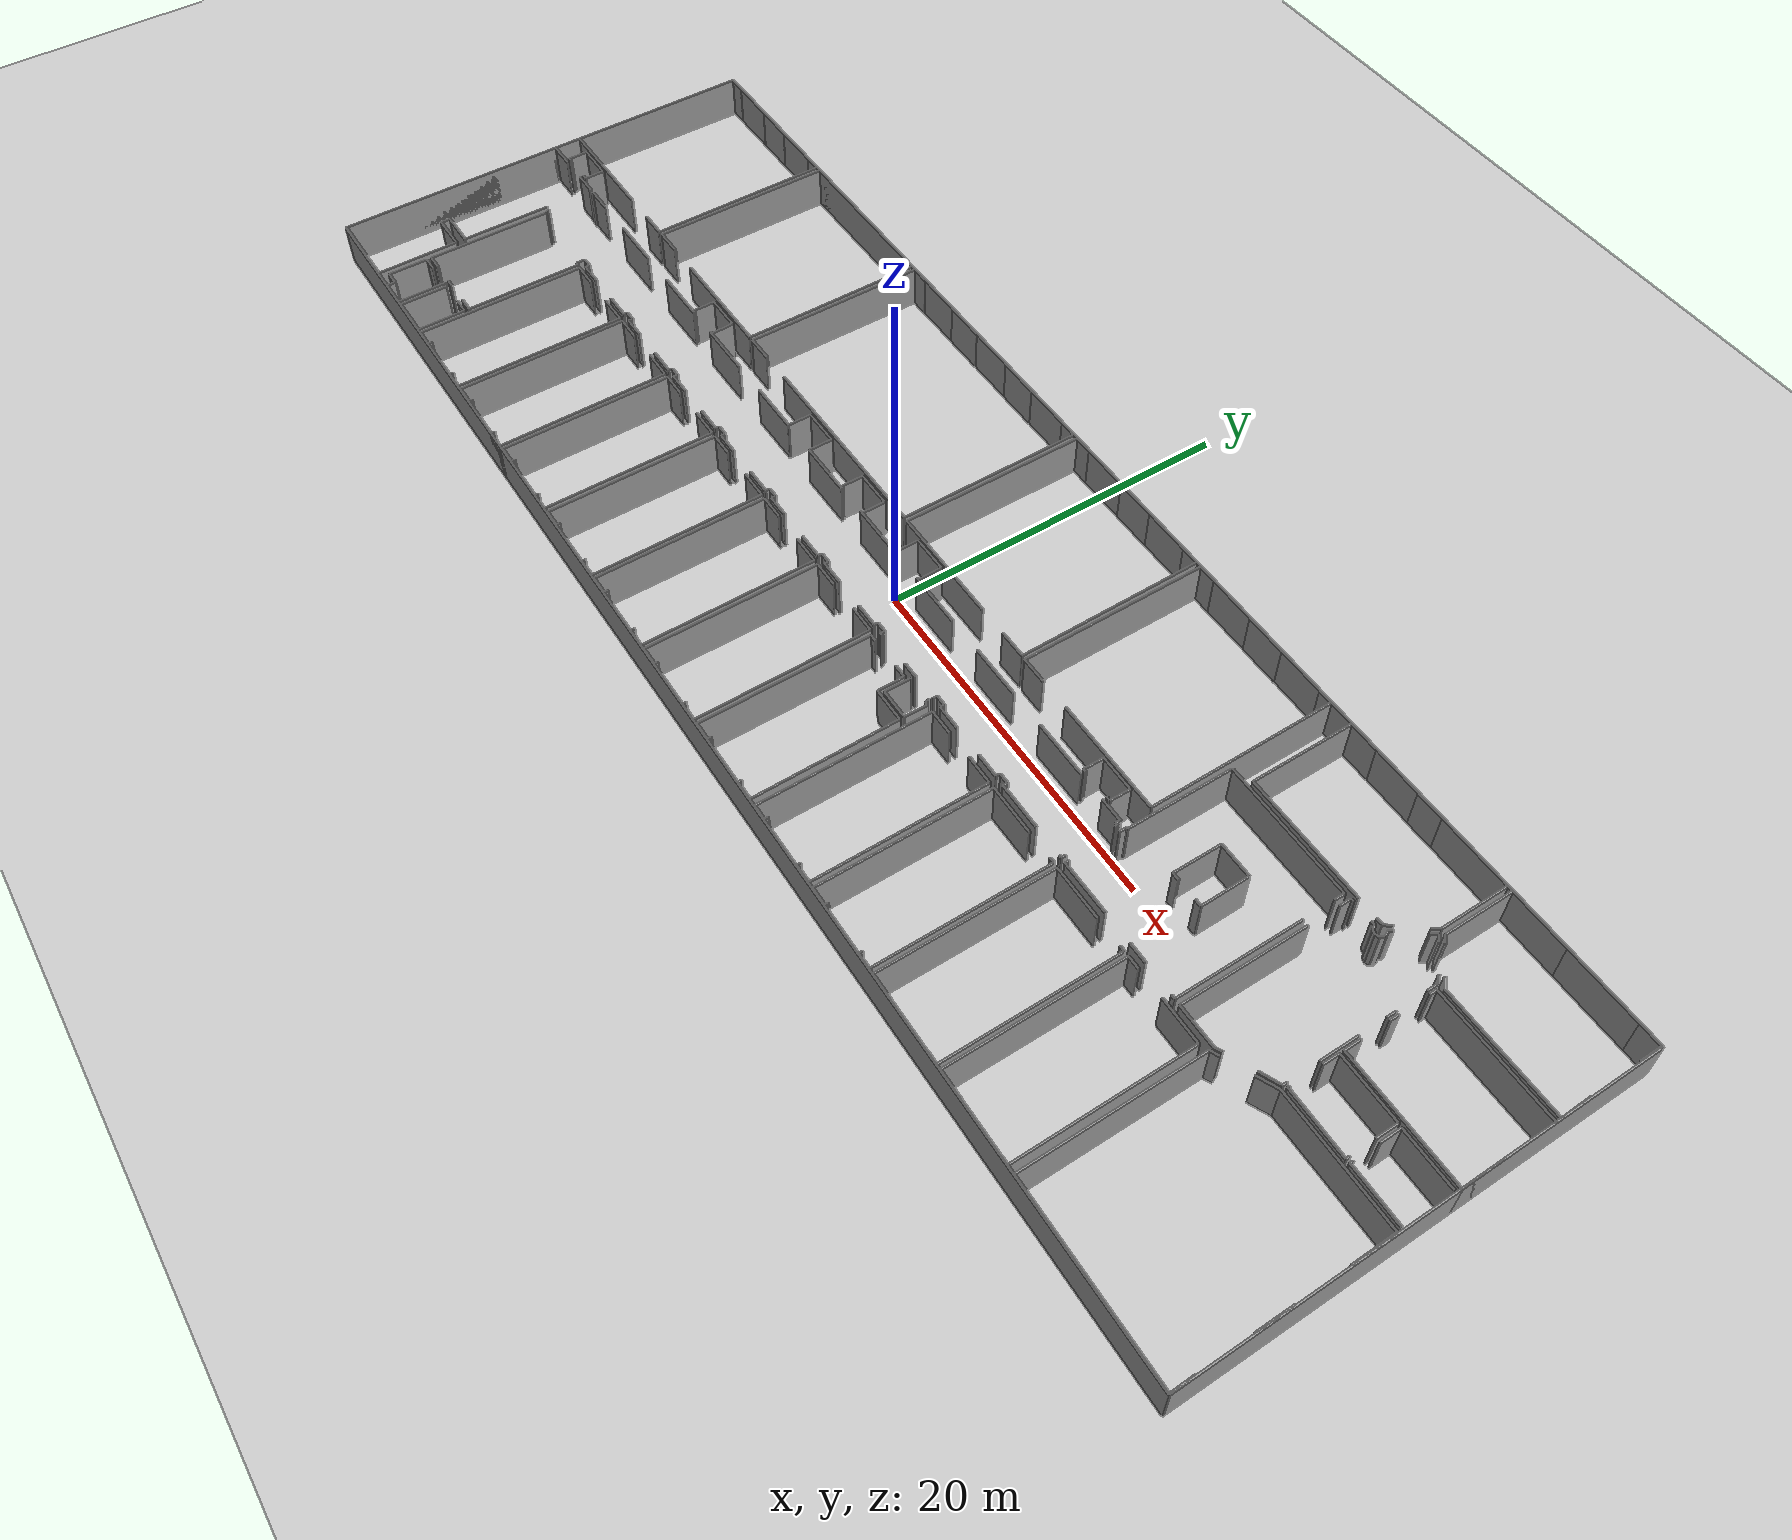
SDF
<sdf version="1.6">
  <world name="default">
    <light name="sun" type="directional">
      <cast_shadows>1</cast_shadows>
      <pose frame="">0 0 10 0 -0 0</pose>
      <diffuse>0.8 0.8 0.8 1</diffuse>
      <specular>0.1 0.1 0.1 1</specular>
      <attenuation>
        <range>1000</range>
        <constant>0.9</constant>
        <linear>0.01</linear>
        <quadratic>0.001</quadratic>
      </attenuation>
      <direction>-0.5 0.5 -1</direction>
    </light>
    <model name="ground_plane">
      <static>1</static>
      <link name="link">
        <collision name="collision">
          <geometry>
            <plane>
              <normal>0 0 1</normal>
              <size>100 100</size>
            </plane>
          </geometry>
          <surface>
            <friction>
              <ode>
                <mu>100</mu>
                <mu2>50</mu2>
              </ode>
              <torsional>
                <ode />
              </torsional>
            </friction>
            <contact>
              <ode />
            </contact>
            <bounce />
          </surface>
          <max_contacts>10</max_contacts>
        </collision>
        <visual name="visual">
          <cast_shadows>0</cast_shadows>
          <geometry>
            <plane>
              <normal>0 0 1</normal>
              <size>100 100</size>
            </plane>
          </geometry>
          <material>
            <script>
              <uri>file://media/materials/scripts/gazebo.material</uri>
              <name>Gazebo/Grey</name>
            </script>
          </material>
        </visual>
        <self_collide>0</self_collide>
        <kinematic>0</kinematic>
        <gravity>1</gravity>
      </link>
    </model>
    <gravity>0 0 -9.8</gravity>
    <magnetic_field>6e-06 2.3e-05 -4.2e-05</magnetic_field>
    <atmosphere type="adiabatic" />
    <physics default="0" name="default_physics" type="ode">
      <max_step_size>0.001</max_step_size>
      <real_time_factor>1</real_time_factor>
      <real_time_update_rate>1000</real_time_update_rate>
    </physics>
    <scene>
      <ambient>0.4 0.4 0.4 1</ambient>
      <background>0.7 0.7 0.7 1</background>
      <shadows>1</shadows>
    </scene>
    <spherical_coordinates>
      <surface_model>EARTH_WGS84</surface_model>
      <latitude_deg>0</latitude_deg>
      <longitude_deg>0</longitude_deg>
      <elevation>0</elevation>
      <heading_deg>0</heading_deg>
    </spherical_coordinates>
  <model name="0510030968_A-40">
		<static>1</static>
		<link name="Wall_0">
			<collision name="Wall_0_Collision">
				<geometry>
					<box>
						<size>1.58504516178 0.1 2.5</size>
					</box>
				</geometry>
				<pose frame="">0.792522580891 0 1.25 0 0 0</pose>
			</collision>
			<visual name="Wall_0_Visual">
				<pose frame="">0.792522580891 0 1.25 0 0 0</pose>
				<geometry>
					<box>
						<size>1.58504516178 0.1 2.5</size>
					</box>
				</geometry>
				<material>
					<script>
						<uri>file://media/materials/scripts/gazebo.material</uri>
						<name>Gazebo/Grey</name>
					</script>
					<ambient>1 1 1 1</ambient>
				</material>
			</visual>
			<pose frame="">10.125385876 -10.6663109621 0 0 0 3.14159265359</pose>
		</link>
		<link name="Wall_1">
			<collision name="Wall_1_Collision">
				<geometry>
					<box>
						<size>6.75495763304 0.1 2.5</size>
					</box>
				</geometry>
				<pose frame="">3.37747881652 0 1.25 0 0 0</pose>
			</collision>
			<visual name="Wall_1_Visual">
				<pose frame="">3.37747881652 0 1.25 0 0 0</pose>
				<geometry>
					<box>
						<size>6.75495763304 0.1 2.5</size>
					</box>
				</geometry>
				<material>
					<script>
						<uri>file://media/materials/scripts/gazebo.material</uri>
						<name>Gazebo/Grey</name>
					</script>
					<ambient>1 1 1 1</ambient>
				</material>
			</visual>
			<pose frame="">6.76575580878 -10.6663109621 0 0 0 3.14159265359</pose>
		</link>
		<link name="Wall_2">
			<collision name="Wall_2_Collision">
				<geometry>
					<box>
						<size>10.658561683 0.1 2.5</size>
					</box>
				</geometry>
				<pose frame="">5.3292808415 0 1.25 0 0 0</pose>
			</collision>
			<visual name="Wall_2_Visual">
				<pose frame="">5.3292808415 0 1.25 0 0 0</pose>
				<geometry>
					<box>
						<size>10.658561683 0.1 2.5</size>
					</box>
				</geometry>
				<material>
					<script>
						<uri>file://media/materials/scripts/gazebo.material</uri>
						<name>Gazebo/Grey</name>
					</script>
					<ambient>1 1 1 1</ambient>
				</material>
			</visual>
			<pose frame="">0.0107981757435 -10.6663109621 0 0 0 1.57079632679</pose>
		</link>
		<link name="Wall_3">
			<collision name="Wall_3_Collision">
				<geometry>
					<box>
						<size>1.02646188244 0.1 2.5</size>
					</box>
				</geometry>
				<pose frame="">0.51323094122 0 1.25 0 0 0</pose>
			</collision>
			<visual name="Wall_3_Visual">
				<pose frame="">0.51323094122 0 1.25 0 0 0</pose>
				<geometry>
					<box>
						<size>1.02646188244 0.1 2.5</size>
					</box>
				</geometry>
				<material>
					<script>
						<uri>file://media/materials/scripts/gazebo.material</uri>
						<name>Gazebo/Grey</name>
					</script>
					<ambient>1 1 1 1</ambient>
				</material>
			</visual>
			<pose frame="">0.0107981757435 -0.00774927906297 0 0 0 0.0</pose>
		</link>
		<link name="Wall_4">
			<collision name="Wall_4_Collision">
				<geometry>
					<box>
						<size>2.39516241727 0.1 2.5</size>
					</box>
				</geometry>
				<pose frame="">1.19758120863 0 1.25 0 0 0</pose>
			</collision>
			<visual name="Wall_4_Visual">
				<pose frame="">1.19758120863 0 1.25 0 0 0</pose>
				<geometry>
					<box>
						<size>2.39516241727 0.1 2.5</size>
					</box>
				</geometry>
				<material>
					<script>
						<uri>file://media/materials/scripts/gazebo.material</uri>
						<name>Gazebo/Grey</name>
					</script>
					<ambient>1 1 1 1</ambient>
				</material>
			</visual>
			<pose frame="">3.835130912 -0.00774927906297 0 0 0 0.0</pose>
		</link>
		<link name="Wall_5">
			<collision name="Wall_5_Collision">
				<geometry>
					<box>
						<size>1.06546235248 0.1 2.5</size>
					</box>
				</geometry>
				<pose frame="">0.532731176239 0 1.25 0 0 0</pose>
			</collision>
			<visual name="Wall_5_Visual">
				<pose frame="">0.532731176239 0 1.25 0 0 0</pose>
				<geometry>
					<box>
						<size>1.06546235248 0.1 2.5</size>
					</box>
				</geometry>
				<material>
					<script>
						<uri>file://media/materials/scripts/gazebo.material</uri>
						<name>Gazebo/Grey</name>
					</script>
					<ambient>1 1 1 1</ambient>
				</material>
			</visual>
			<pose frame="">9.03680272368 -0.00774927906297 0 0 0 0.0</pose>
		</link>
		<link name="Wall_6">
			<collision name="Wall_6_Collision">
				<geometry>
					<box>
						<size>10.65858676 0.1 2.5</size>
					</box>
				</geometry>
				<pose frame="">5.32929338002 0 1.25 0 0 0</pose>
			</collision>
			<visual name="Wall_6_Visual">
				<pose frame="">5.32929338002 0 1.25 0 0 0</pose>
				<geometry>
					<box>
						<size>10.65858676 0.1 2.5</size>
					</box>
				</geometry>
				<material>
					<script>
						<uri>file://media/materials/scripts/gazebo.material</uri>
						<name>Gazebo/Grey</name>
					</script>
					<ambient>1 1 1 1</ambient>
				</material>
			</visual>
			<pose frame="">10.1022650762 -0.00774927906297 0 0 0 -1.56862710695</pose>
		</link>
		<link name="Wall_7">
			<collision name="Wall_7_Collision">
				<geometry>
					<box>
						<size>0.275925149586 0.1 2.5</size>
					</box>
				</geometry>
				<pose frame="">0.137962574793 0 1.25 0 0 0</pose>
			</collision>
			<visual name="Wall_7_Visual">
				<pose frame="">0.137962574793 0 1.25 0 0 0</pose>
				<geometry>
					<box>
						<size>0.275925149586 0.1 2.5</size>
					</box>
				</geometry>
				<material>
					<script>
						<uri>file://media/materials/scripts/gazebo.material</uri>
						<name>Gazebo/Grey</name>
					</script>
					<ambient>1 1 1 1</ambient>
				</material>
			</visual>
			<pose frame="">3.52630308574 -12.0571159978 0 0 0 3.14159265359</pose>
		</link>
		<link name="Wall_8">
			<collision name="Wall_8_Collision">
				<geometry>
					<box>
						<size>0.254074723376 0.1 2.5</size>
					</box>
				</geometry>
				<pose frame="">0.127037361688 0 1.25 0 0 0</pose>
			</collision>
			<visual name="Wall_8_Visual">
				<pose frame="">0.127037361688 0 1.25 0 0 0</pose>
				<geometry>
					<box>
						<size>0.254074723376 0.1 2.5</size>
					</box>
				</geometry>
				<material>
					<script>
						<uri>file://media/materials/scripts/gazebo.material</uri>
						<name>Gazebo/Grey</name>
					</script>
					<ambient>1 1 1 1</ambient>
				</material>
			</visual>
			<pose frame="">1.63382750867 -12.0571159978 0 0 0 3.14159265359</pose>
		</link>
		<link name="Wall_9">
			<collision name="Wall_9_Collision">
				<geometry>
					<box>
						<size>1.16505964404 0.1 2.5</size>
					</box>
				</geometry>
				<pose frame="">0.582529822021 0 1.25 0 0 0</pose>
			</collision>
			<visual name="Wall_9_Visual">
				<pose frame="">0.582529822021 0 1.25 0 0 0</pose>
				<geometry>
					<box>
						<size>1.16505964404 0.1 2.5</size>
					</box>
				</geometry>
				<material>
					<script>
						<uri>file://media/materials/scripts/gazebo.material</uri>
						<name>Gazebo/Grey</name>
					</script>
					<ambient>1 1 1 1</ambient>
				</material>
			</visual>
			<pose frame="">1.37975278529 -12.0571159978 0 0 0 1.57079632679</pose>
		</link>
		<link name="Wall_10">
			<collision name="Wall_10_Collision">
				<geometry>
					<box>
						<size>2.15404550478 0.1 2.5</size>
					</box>
				</geometry>
				<pose frame="">1.07702275239 0 1.25 0 0 0</pose>
			</collision>
			<visual name="Wall_10_Visual">
				<pose frame="">1.07702275239 0 1.25 0 0 0</pose>
				<geometry>
					<box>
						<size>2.15404550478 0.1 2.5</size>
					</box>
				</geometry>
				<material>
					<script>
						<uri>file://media/materials/scripts/gazebo.material</uri>
						<name>Gazebo/Grey</name>
					</script>
					<ambient>1 1 1 1</ambient>
				</material>
			</visual>
			<pose frame="">1.37975278529 -10.8920563538 0 0 0 0.0</pose>
		</link>
		<link name="Wall_11">
			<collision name="Wall_11_Collision">
				<geometry>
					<box>
						<size>1.16508375332 0.1 2.5</size>
					</box>
				</geometry>
				<pose frame="">0.582541876662 0 1.25 0 0 0</pose>
			</collision>
			<visual name="Wall_11_Visual">
				<pose frame="">0.582541876662 0 1.25 0 0 0</pose>
				<geometry>
					<box>
						<size>1.16508375332 0.1 2.5</size>
					</box>
				</geometry>
				<material>
					<script>
						<uri>file://media/materials/scripts/gazebo.material</uri>
						<name>Gazebo/Grey</name>
					</script>
					<ambient>1 1 1 1</ambient>
				</material>
			</visual>
			<pose frame="">3.53379829008 -10.8920563538 0 0 0 -1.57722956047</pose>
		</link>
		<link name="Wall_12">
			<collision name="Wall_12_Collision">
				<geometry>
					<box>
						<size>4.64728076527 0.1 2.5</size>
					</box>
				</geometry>
				<pose frame="">2.32364038264 0 1.25 0 0 0</pose>
			</collision>
			<visual name="Wall_12_Visual">
				<pose frame="">2.32364038264 0 1.25 0 0 0</pose>
				<geometry>
					<box>
						<size>4.64728076527 0.1 2.5</size>
					</box>
				</geometry>
				<material>
					<script>
						<uri>file://media/materials/scripts/gazebo.material</uri>
						<name>Gazebo/Grey</name>
					</script>
					<ambient>1 1 1 1</ambient>
				</material>
			</visual>
			<pose frame="">4.64728076527 -25.7094401463 0 0 0 3.14159265359</pose>
		</link>
		<link name="Wall_13">
			<collision name="Wall_13_Collision">
				<geometry>
					<box>
						<size>9.44433857998 0.1 2.5</size>
					</box>
				</geometry>
				<pose frame="">4.72216928999 0 1.25 0 0 0</pose>
			</collision>
			<visual name="Wall_13_Visual">
				<pose frame="">4.72216928999 0 1.25 0 0 0</pose>
				<geometry>
					<box>
						<size>9.44433857998 0.1 2.5</size>
					</box>
				</geometry>
				<material>
					<script>
						<uri>file://media/materials/scripts/gazebo.material</uri>
						<name>Gazebo/Grey</name>
					</script>
					<ambient>1 1 1 1</ambient>
				</material>
			</visual>
			<pose frame="">0.0 -25.7094401463 0 0 0 1.57079632679</pose>
		</link>
		<link name="Wall_14">
			<collision name="Wall_14_Collision">
				<geometry>
					<box>
						<size>0.189412706277 0.1 2.5</size>
					</box>
				</geometry>
				<pose frame="">0.0947063531385 0 1.25 0 0 0</pose>
			</collision>
			<visual name="Wall_14_Visual">
				<pose frame="">0.0947063531385 0 1.25 0 0 0</pose>
				<geometry>
					<box>
						<size>0.189412706277 0.1 2.5</size>
					</box>
				</geometry>
				<material>
					<script>
						<uri>file://media/materials/scripts/gazebo.material</uri>
						<name>Gazebo/Grey</name>
					</script>
					<ambient>1 1 1 1</ambient>
				</material>
			</visual>
			<pose frame="">0.0 -12.462873331 0 0 0 1.57079632679</pose>
		</link>
		<link name="Wall_15">
			<collision name="Wall_15_Collision">
				<geometry>
					<box>
						<size>1.63103268671 0.1 2.5</size>
					</box>
				</geometry>
				<pose frame="">0.815516343357 0 1.25 0 0 0</pose>
			</collision>
			<visual name="Wall_15_Visual">
				<pose frame="">0.815516343357 0 1.25 0 0 0</pose>
				<geometry>
					<box>
						<size>1.63103268671 0.1 2.5</size>
					</box>
				</geometry>
				<material>
					<script>
						<uri>file://media/materials/scripts/gazebo.material</uri>
						<name>Gazebo/Grey</name>
					</script>
					<ambient>1 1 1 1</ambient>
				</material>
			</visual>
			<pose frame="">0.0 -12.2734606248 0 0 0 0.0</pose>
		</link>
		<link name="Wall_16">
			<collision name="Wall_16_Collision">
				<geometry>
					<box>
						<size>1.37949871057 0.1 2.5</size>
					</box>
				</geometry>
				<pose frame="">0.689749355285 0 1.25 0 0 0</pose>
			</collision>
			<visual name="Wall_16_Visual">
				<pose frame="">0.689749355285 0 1.25 0 0 0</pose>
				<geometry>
					<box>
						<size>1.37949871057 0.1 2.5</size>
					</box>
				</geometry>
				<material>
					<script>
						<uri>file://media/materials/scripts/gazebo.material</uri>
						<name>Gazebo/Grey</name>
					</script>
					<ambient>1 1 1 1</ambient>
				</material>
			</visual>
			<pose frame="">3.24402606807 -12.2734606248 0 0 0 0.0</pose>
		</link>
		<link name="Wall_17">
			<collision name="Wall_17_Collision">
				<geometry>
					<box>
						<size>0.0923561619472 0.1 2.5</size>
					</box>
				</geometry>
				<pose frame="">0.0461780809736 0 1.25 0 0 0</pose>
			</collision>
			<visual name="Wall_17_Visual">
				<pose frame="">0.0461780809736 0 1.25 0 0 0</pose>
				<geometry>
					<box>
						<size>0.0923561619472 0.1 2.5</size>
					</box>
				</geometry>
				<material>
					<script>
						<uri>file://media/materials/scripts/gazebo.material</uri>
						<name>Gazebo/Grey</name>
					</script>
					<ambient>1 1 1 1</ambient>
				</material>
			</visual>
			<pose frame="">4.62352477864 -12.2734606248 0 0 0 -1.57079632679</pose>
		</link>
		<link name="Wall_18">
			<collision name="Wall_18_Collision">
				<geometry>
					<box>
						<size>5.23520967517 0.1 2.5</size>
					</box>
				</geometry>
				<pose frame="">2.61760483758 0 1.25 0 0 0</pose>
			</collision>
			<visual name="Wall_18_Visual">
				<pose frame="">2.61760483758 0 1.25 0 0 0</pose>
				<geometry>
					<box>
						<size>5.23520967517 0.1 2.5</size>
					</box>
				</geometry>
				<material>
					<script>
						<uri>file://media/materials/scripts/gazebo.material</uri>
						<name>Gazebo/Grey</name>
					</script>
					<ambient>1 1 1 1</ambient>
				</material>
			</visual>
			<pose frame="">4.62352477864 -15.132944599 0 0 0 -1.57079632679</pose>
		</link>
		<link name="Wall_19">
			<collision name="Wall_19_Collision">
				<geometry>
					<box>
						<size>2.06753306147 0.1 2.5</size>
					</box>
				</geometry>
				<pose frame="">1.03376653074 0 1.25 0 0 0</pose>
			</collision>
			<visual name="Wall_19_Visual">
				<pose frame="">1.03376653074 0 1.25 0 0 0</pose>
				<geometry>
					<box>
						<size>2.06753306147 0.1 2.5</size>
					</box>
				</geometry>
				<material>
					<script>
						<uri>file://media/materials/scripts/gazebo.material</uri>
						<name>Gazebo/Grey</name>
					</script>
					<ambient>1 1 1 1</ambient>
				</material>
			</visual>
			<pose frame="">4.62352477864 -20.3681542742 0 0 0 3.14159265359</pose>
		</link>
		<link name="Wall_20">
			<collision name="Wall_20_Collision">
				<geometry>
					<box>
						<size>0.538003226749 0.1 2.5</size>
					</box>
				</geometry>
				<pose frame="">0.269001613374 0 1.25 0 0 0</pose>
			</collision>
			<visual name="Wall_20_Visual">
				<pose frame="">0.269001613374 0 1.25 0 0 0</pose>
				<geometry>
					<box>
						<size>0.538003226749 0.1 2.5</size>
					</box>
				</geometry>
				<material>
					<script>
						<uri>file://media/materials/scripts/gazebo.material</uri>
						<name>Gazebo/Grey</name>
					</script>
					<ambient>1 1 1 1</ambient>
				</material>
			</visual>
			<pose frame="">2.55599171716 -20.3681542742 0 0 0 -1.57079632679</pose>
		</link>
		<link name="Wall_21">
			<collision name="Wall_21_Collision">
				<geometry>
					<box>
						<size>2.06524638896 0.1 2.5</size>
					</box>
				</geometry>
				<pose frame="">1.03262319448 0 1.25 0 0 0</pose>
			</collision>
			<visual name="Wall_21_Visual">
				<pose frame="">1.03262319448 0 1.25 0 0 0</pose>
				<geometry>
					<box>
						<size>2.06524638896 0.1 2.5</size>
					</box>
				</geometry>
				<material>
					<script>
						<uri>file://media/materials/scripts/gazebo.material</uri>
						<name>Gazebo/Grey</name>
					</script>
					<ambient>1 1 1 1</ambient>
				</material>
			</visual>
			<pose frame="">2.55599171716 -20.9061575009 0 0 0 0.0</pose>
		</link>
		<link name="Wall_22">
			<collision name="Wall_22_Collision">
				<geometry>
					<box>
						<size>4.80335324455 0.1 2.5</size>
					</box>
				</geometry>
				<pose frame="">2.40167662228 0 1.25 0 0 0</pose>
			</collision>
			<visual name="Wall_22_Visual">
				<pose frame="">2.40167662228 0 1.25 0 0 0</pose>
				<geometry>
					<box>
						<size>4.80335324455 0.1 2.5</size>
					</box>
				</geometry>
				<material>
					<script>
						<uri>file://media/materials/scripts/gazebo.material</uri>
						<name>Gazebo/Grey</name>
					</script>
					<ambient>1 1 1 1</ambient>
				</material>
			</visual>
			<pose frame="">4.62123810613 -20.9061575009 0 0 0 -1.56537453385</pose>
		</link>
		<link name="Wall_23">
			<collision name="Wall_23_Collision">
				<geometry>
					<box>
						<size>0.872111487989 0.1 2.5</size>
					</box>
				</geometry>
				<pose frame="">0.436055743994 0 1.25 0 0 0</pose>
			</collision>
			<visual name="Wall_23_Visual">
				<pose frame="">0.436055743994 0 1.25 0 0 0</pose>
				<geometry>
					<box>
						<size>0.872111487989 0.1 2.5</size>
					</box>
				</geometry>
				<material>
					<script>
						<uri>file://media/materials/scripts/gazebo.material</uri>
						<name>Gazebo/Grey</name>
					</script>
					<ambient>1 1 1 1</ambient>
				</material>
			</visual>
			<pose frame="">10.1187799332 -22.6656249603 0 0 0 3.14159265359</pose>
		</link>
		<link name="Wall_24">
			<collision name="Wall_24_Collision">
				<geometry>
					<box>
						<size>0.450347447184 0.1 2.5</size>
					</box>
				</geometry>
				<pose frame="">0.225173723592 0 1.25 0 0 0</pose>
			</collision>
			<visual name="Wall_24_Visual">
				<pose frame="">0.225173723592 0 1.25 0 0 0</pose>
				<geometry>
					<box>
						<size>0.450347447184 0.1 2.5</size>
					</box>
				</geometry>
				<material>
					<script>
						<uri>file://media/materials/scripts/gazebo.material</uri>
						<name>Gazebo/Grey</name>
					</script>
					<ambient>1 1 1 1</ambient>
				</material>
			</visual>
			<pose frame="">7.83350483377 -22.6656249603 0 0 0 3.14159265359</pose>
		</link>
		<link name="Wall_25">
			<collision name="Wall_25_Collision">
				<geometry>
					<box>
						<size>0.868681479223 0.1 2.5</size>
					</box>
				</geometry>
				<pose frame="">0.434340739612 0 1.25 0 0 0</pose>
			</collision>
			<visual name="Wall_25_Visual">
				<pose frame="">0.434340739612 0 1.25 0 0 0</pose>
				<geometry>
					<box>
						<size>0.868681479223 0.1 2.5</size>
					</box>
				</geometry>
				<material>
					<script>
						<uri>file://media/materials/scripts/gazebo.material</uri>
						<name>Gazebo/Grey</name>
					</script>
					<ambient>1 1 1 1</ambient>
				</material>
			</visual>
			<pose frame="">5.93886962156 -22.6656249603 0 0 0 3.14159265359</pose>
		</link>
		<link name="Wall_26">
			<collision name="Wall_26_Collision">
				<geometry>
					<box>
						<size>7.22372549767 0.1 2.5</size>
					</box>
				</geometry>
				<pose frame="">3.61186274883 0 1.25 0 0 0</pose>
			</collision>
			<visual name="Wall_26_Visual">
				<pose frame="">3.61186274883 0 1.25 0 0 0</pose>
				<geometry>
					<box>
						<size>7.22372549767 0.1 2.5</size>
					</box>
				</geometry>
				<material>
					<script>
						<uri>file://media/materials/scripts/gazebo.material</uri>
						<name>Gazebo/Grey</name>
					</script>
					<ambient>1 1 1 1</ambient>
				</material>
			</visual>
			<pose frame="">5.07018814233 -22.6656249603 0 0 0 1.57079632679</pose>
		</link>
		<link name="Wall_27">
			<collision name="Wall_27_Collision">
				<geometry>
					<box>
						<size>0.461018585566 0.1 2.5</size>
					</box>
				</geometry>
				<pose frame="">0.230509292783 0 1.25 0 0 0</pose>
			</collision>
			<visual name="Wall_27_Visual">
				<pose frame="">0.230509292783 0 1.25 0 0 0</pose>
				<geometry>
					<box>
						<size>0.461018585566 0.1 2.5</size>
					</box>
				</geometry>
				<material>
					<script>
						<uri>file://media/materials/scripts/gazebo.material</uri>
						<name>Gazebo/Grey</name>
					</script>
					<ambient>1 1 1 1</ambient>
				</material>
			</visual>
			<pose frame="">9.9320350115 -15.4418994626 0 0 0 -1.57079632679</pose>
		</link>
		<link name="Wall_28">
			<collision name="Wall_28_Collision">
				<geometry>
					<box>
						<size>0.186744921681 0.1 2.5</size>
					</box>
				</geometry>
				<pose frame="">0.0933724608407 0 1.25 0 0 0</pose>
			</collision>
			<visual name="Wall_28_Visual">
				<pose frame="">0.0933724608407 0 1.25 0 0 0</pose>
				<geometry>
					<box>
						<size>0.186744921681 0.1 2.5</size>
					</box>
				</geometry>
				<material>
					<script>
						<uri>file://media/materials/scripts/gazebo.material</uri>
						<name>Gazebo/Grey</name>
					</script>
					<ambient>1 1 1 1</ambient>
				</material>
			</visual>
			<pose frame="">9.9320350115 -15.9029180482 0 0 0 0.0</pose>
		</link>
		<link name="Wall_29">
			<collision name="Wall_29_Collision">
				<geometry>
					<box>
						<size>6.7627069121 0.1 2.5</size>
					</box>
				</geometry>
				<pose frame="">3.38135345605 0 1.25 0 0 0</pose>
			</collision>
			<visual name="Wall_29_Visual">
				<pose frame="">3.38135345605 0 1.25 0 0 0</pose>
				<geometry>
					<box>
						<size>6.7627069121 0.1 2.5</size>
					</box>
				</geometry>
				<material>
					<script>
						<uri>file://media/materials/scripts/gazebo.material</uri>
						<name>Gazebo/Grey</name>
					</script>
					<ambient>1 1 1 1</ambient>
				</material>
			</visual>
			<pose frame="">10.1187799332 -15.9029180482 0 0 0 -1.57079632679</pose>
		</link>
		<link name="Wall_30">
			<collision name="Wall_30_Collision">
				<geometry>
					<box>
						<size>0.105059898116 0.1 2.5</size>
					</box>
				</geometry>
				<pose frame="">0.052529949058 0 1.25 0 0 0</pose>
			</collision>
			<visual name="Wall_30_Visual">
				<pose frame="">0.052529949058 0 1.25 0 0 0</pose>
				<geometry>
					<box>
						<size>0.105059898116 0.1 2.5</size>
					</box>
				</geometry>
				<material>
					<script>
						<uri>file://media/materials/scripts/gazebo.material</uri>
						<name>Gazebo/Grey</name>
					</script>
					<ambient>1 1 1 1</ambient>
				</material>
			</visual>
			<pose frame="">4.94607263996 -15.2543923168 0 0 0 1.57079632679</pose>
		</link>
		<link name="Wall_31">
			<collision name="Wall_31_Collision">
				<geometry>
					<box>
						<size>0.116239185945 0.1 2.5</size>
					</box>
				</geometry>
				<pose frame="">0.0581195929723 0 1.25 0 0 0</pose>
			</collision>
			<visual name="Wall_31_Visual">
				<pose frame="">0.0581195929723 0 1.25 0 0 0</pose>
				<geometry>
					<box>
						<size>0.116239185945 0.1 2.5</size>
					</box>
				</geometry>
				<material>
					<script>
						<uri>file://media/materials/scripts/gazebo.material</uri>
						<name>Gazebo/Grey</name>
					</script>
					<ambient>1 1 1 1</ambient>
				</material>
			</visual>
			<pose frame="">4.94607263996 -12.3912242591 0 0 0 1.57079632679</pose>
		</link>
		<link name="Wall_32">
			<collision name="Wall_32_Collision">
				<geometry>
					<box>
						<size>1.62366451974 0.1 2.5</size>
					</box>
				</geometry>
				<pose frame="">0.811832259868 0 1.25 0 0 0</pose>
			</collision>
			<visual name="Wall_32_Visual">
				<pose frame="">0.811832259868 0 1.25 0 0 0</pose>
				<geometry>
					<box>
						<size>1.62366451974 0.1 2.5</size>
					</box>
				</geometry>
				<material>
					<script>
						<uri>file://media/materials/scripts/gazebo.material</uri>
						<name>Gazebo/Grey</name>
					</script>
					<ambient>1 1 1 1</ambient>
				</material>
			</visual>
			<pose frame="">4.94607263996 -12.2749850731 0 0 0 0.0</pose>
		</link>
		<link name="Wall_33">
			<collision name="Wall_33_Collision">
				<geometry>
					<box>
						<size>3.08345084289 0.1 2.5</size>
					</box>
				</geometry>
				<pose frame="">1.54172542145 0 1.25 0 0 0</pose>
			</collision>
			<visual name="Wall_33_Visual">
				<pose frame="">1.54172542145 0 1.25 0 0 0</pose>
				<geometry>
					<box>
						<size>3.08345084289 0.1 2.5</size>
					</box>
				</geometry>
				<material>
					<script>
						<uri>file://media/materials/scripts/gazebo.material</uri>
						<name>Gazebo/Grey</name>
					</script>
					<ambient>1 1 1 1</ambient>
				</material>
			</visual>
			<pose frame="">8.69405592185 -12.2749850731 0 0 0 0.0</pose>
		</link>
		<link name="Wall_34">
			<collision name="Wall_34_Collision">
				<geometry>
					<box>
						<size>3.24682089002 0.1 2.5</size>
					</box>
				</geometry>
				<pose frame="">1.62341044501 0 1.25 0 0 0</pose>
			</collision>
			<visual name="Wall_34_Visual">
				<pose frame="">1.62341044501 0 1.25 0 0 0</pose>
				<geometry>
					<box>
						<size>3.24682089002 0.1 2.5</size>
					</box>
				</geometry>
				<material>
					<script>
						<uri>file://media/materials/scripts/gazebo.material</uri>
						<name>Gazebo/Grey</name>
					</script>
					<ambient>1 1 1 1</ambient>
				</material>
			</visual>
			<pose frame="">13.9004281159 -12.2749850731 0 0 0 0.0</pose>
		</link>
		<link name="Wall_35">
			<collision name="Wall_35_Collision">
				<geometry>
					<box>
						<size>3.23386307913 0.1 2.5</size>
					</box>
				</geometry>
				<pose frame="">1.61693153957 0 1.25 0 0 0</pose>
			</collision>
			<visual name="Wall_35_Visual">
				<pose frame="">1.61693153957 0 1.25 0 0 0</pose>
				<geometry>
					<box>
						<size>3.23386307913 0.1 2.5</size>
					</box>
				</geometry>
				<material>
					<script>
						<uri>file://media/materials/scripts/gazebo.material</uri>
						<name>Gazebo/Grey</name>
					</script>
					<ambient>1 1 1 1</ambient>
				</material>
			</visual>
			<pose frame="">18.9809062845 -12.2749850731 0 0 0 0.0</pose>
		</link>
		<link name="Wall_36">
			<collision name="Wall_36_Collision">
				<geometry>
					<box>
						<size>3.08218046928 0.1 2.5</size>
					</box>
				</geometry>
				<pose frame="">1.54109023464 0 1.25 0 0 0</pose>
			</collision>
			<visual name="Wall_36_Visual">
				<pose frame="">1.54109023464 0 1.25 0 0 0</pose>
				<geometry>
					<box>
						<size>3.08218046928 0.1 2.5</size>
					</box>
				</geometry>
				<material>
					<script>
						<uri>file://media/materials/scripts/gazebo.material</uri>
						<name>Gazebo/Grey</name>
					</script>
					<ambient>1 1 1 1</ambient>
				</material>
			</visual>
			<pose frame="">24.3069476733 -12.2749850731 0 0 0 0.0</pose>
		</link>
		<link name="Wall_37">
			<collision name="Wall_37_Collision">
				<geometry>
					<box>
						<size>1.37568758972 0.1 2.5</size>
					</box>
				</geometry>
				<pose frame="">0.68784379486 0 1.25 0 0 0</pose>
			</collision>
			<visual name="Wall_37_Visual">
				<pose frame="">0.68784379486 0 1.25 0 0 0</pose>
				<geometry>
					<box>
						<size>1.37568758972 0.1 2.5</size>
					</box>
				</geometry>
				<material>
					<script>
						<uri>file://media/materials/scripts/gazebo.material</uri>
						<name>Gazebo/Grey</name>
					</script>
					<ambient>1 1 1 1</ambient>
				</material>
			</visual>
			<pose frame="">27.3891281426 -12.2749850731 0 0 0 1.57079632679</pose>
		</link>
		<link name="Wall_38">
			<collision name="Wall_38_Collision">
				<geometry>
					<box>
						<size>2.1384199093 0.1 2.5</size>
					</box>
				</geometry>
				<pose frame="">1.06920995465 0 1.25 0 0 0</pose>
			</collision>
			<visual name="Wall_38_Visual">
				<pose frame="">1.06920995465 0 1.25 0 0 0</pose>
				<geometry>
					<box>
						<size>2.1384199093 0.1 2.5</size>
					</box>
				</geometry>
				<material>
					<script>
						<uri>file://media/materials/scripts/gazebo.material</uri>
						<name>Gazebo/Grey</name>
					</script>
					<ambient>1 1 1 1</ambient>
				</material>
			</visual>
			<pose frame="">27.3891281426 -10.8992974834 0 0 0 0.0</pose>
		</link>
		<link name="Wall_39">
			<collision name="Wall_39_Collision">
				<geometry>
					<box>
						<size>1.37822833695 0.1 2.5</size>
					</box>
				</geometry>
				<pose frame="">0.689114168477 0 1.25 0 0 0</pose>
			</collision>
			<visual name="Wall_39_Visual">
				<pose frame="">0.689114168477 0 1.25 0 0 0</pose>
				<geometry>
					<box>
						<size>1.37822833695 0.1 2.5</size>
					</box>
				</geometry>
				<material>
					<script>
						<uri>file://media/materials/scripts/gazebo.material</uri>
						<name>Gazebo/Grey</name>
					</script>
					<ambient>1 1 1 1</ambient>
				</material>
			</visual>
			<pose frame="">29.5275480519 -10.8992974834 0 0 0 -1.57079632679</pose>
		</link>
		<link name="Wall_40">
			<collision name="Wall_40_Collision">
				<geometry>
					<box>
						<size>3.23259270551 0.1 2.5</size>
					</box>
				</geometry>
				<pose frame="">1.61629635276 0 1.25 0 0 0</pose>
			</collision>
			<visual name="Wall_40_Visual">
				<pose frame="">1.61629635276 0 1.25 0 0 0</pose>
				<geometry>
					<box>
						<size>3.23259270551 0.1 2.5</size>
					</box>
				</geometry>
				<material>
					<script>
						<uri>file://media/materials/scripts/gazebo.material</uri>
						<name>Gazebo/Grey</name>
					</script>
					<ambient>1 1 1 1</ambient>
				</material>
			</visual>
			<pose frame="">29.5275480519 -12.2775258203 0 0 0 0.0</pose>
		</link>
		<link name="Wall_41">
			<collision name="Wall_41_Collision">
				<geometry>
					<box>
						<size>3.36242488916 0.1 2.5</size>
					</box>
				</geometry>
				<pose frame="">1.68121244458 0 1.25 0 0 0</pose>
			</collision>
			<visual name="Wall_41_Visual">
				<pose frame="">1.68121244458 0 1.25 0 0 0</pose>
				<geometry>
					<box>
						<size>3.36242488916 0.1 2.5</size>
					</box>
				</geometry>
				<material>
					<script>
						<uri>file://media/materials/scripts/gazebo.material</uri>
						<name>Gazebo/Grey</name>
					</script>
					<ambient>1 1 1 1</ambient>
				</material>
			</visual>
			<pose frame="">34.5855406075 -12.2775258203 0 0 0 0.0</pose>
		</link>
		<link name="Wall_42">
			<collision name="Wall_42_Collision">
				<geometry>
					<box>
						<size>3.2074393079 0.1 2.5</size>
					</box>
				</geometry>
				<pose frame="">1.60371965395 0 1.25 0 0 0</pose>
			</collision>
			<visual name="Wall_42_Visual">
				<pose frame="">1.60371965395 0 1.25 0 0 0</pose>
				<geometry>
					<box>
						<size>3.2074393079 0.1 2.5</size>
					</box>
				</geometry>
				<material>
					<script>
						<uri>file://media/materials/scripts/gazebo.material</uri>
						<name>Gazebo/Grey</name>
					</script>
					<ambient>1 1 1 1</ambient>
				</material>
			</visual>
			<pose frame="">39.8039813509 -12.2775258203 0 0 0 0.0</pose>
		</link>
		<link name="Wall_43">
			<collision name="Wall_43_Collision">
				<geometry>
					<box>
						<size>3.09310568238 0.1 2.5</size>
					</box>
				</geometry>
				<pose frame="">1.54655284119 0 1.25 0 0 0</pose>
			</collision>
			<visual name="Wall_43_Visual">
				<pose frame="">1.54655284119 0 1.25 0 0 0</pose>
				<geometry>
					<box>
						<size>3.09310568238 0.1 2.5</size>
					</box>
				</geometry>
				<material>
					<script>
						<uri>file://media/materials/scripts/gazebo.material</uri>
						<name>Gazebo/Grey</name>
					</script>
					<ambient>1 1 1 1</ambient>
				</material>
			</visual>
			<pose frame="">45.1056315662 -12.2775258203 0 0 0 0.0</pose>
		</link>
		<link name="Wall_44">
			<collision name="Wall_44_Collision">
				<geometry>
					<box>
						<size>3.30614733793 0.1 2.5</size>
					</box>
				</geometry>
				<pose frame="">1.65307366897 0 1.25 0 0 0</pose>
			</collision>
			<visual name="Wall_44_Visual">
				<pose frame="">1.65307366897 0 1.25 0 0 0</pose>
				<geometry>
					<box>
						<size>3.30614733793 0.1 2.5</size>
					</box>
				</geometry>
				<material>
					<script>
						<uri>file://media/materials/scripts/gazebo.material</uri>
						<name>Gazebo/Grey</name>
					</script>
					<ambient>1 1 1 1</ambient>
				</material>
			</visual>
			<pose frame="">50.3161959932 -12.2775258203 0 0 0 0.0</pose>
		</link>
		<link name="Wall_45">
			<collision name="Wall_45_Collision">
				<geometry>
					<box>
						<size>1.36196755466 0.1 2.5</size>
					</box>
				</geometry>
				<pose frame="">0.680983777329 0 1.25 0 0 0</pose>
			</collision>
			<visual name="Wall_45_Visual">
				<pose frame="">0.680983777329 0 1.25 0 0 0</pose>
				<geometry>
					<box>
						<size>1.36196755466 0.1 2.5</size>
					</box>
				</geometry>
				<material>
					<script>
						<uri>file://media/materials/scripts/gazebo.material</uri>
						<name>Gazebo/Grey</name>
					</script>
					<ambient>1 1 1 1</ambient>
				</material>
			</visual>
			<pose frame="">55.198622915 -12.2775258203 0 0 0 0.0</pose>
		</link>
		<link name="Wall_46">
			<collision name="Wall_46_Collision">
				<geometry>
					<box>
						<size>0.280625531969 0.1 2.5</size>
					</box>
				</geometry>
				<pose frame="">0.140312765984 0 1.25 0 0 0</pose>
			</collision>
			<visual name="Wall_46_Visual">
				<pose frame="">0.140312765984 0 1.25 0 0 0</pose>
				<geometry>
					<box>
						<size>0.280625531969 0.1 2.5</size>
					</box>
				</geometry>
				<material>
					<script>
						<uri>file://media/materials/scripts/gazebo.material</uri>
						<name>Gazebo/Grey</name>
					</script>
					<ambient>1 1 1 1</ambient>
				</material>
			</visual>
			<pose frame="">56.5605904697 -12.2775258203 0 0 0 -1.57079632679</pose>
		</link>
		<link name="Wall_47">
			<collision name="Wall_47_Collision">
				<geometry>
					<box>
						<size>0.137327387985 0.1 2.5</size>
					</box>
				</geometry>
				<pose frame="">0.0686636939924 0 1.25 0 0 0</pose>
			</collision>
			<visual name="Wall_47_Visual">
				<pose frame="">0.0686636939924 0 1.25 0 0 0</pose>
				<geometry>
					<box>
						<size>0.137327387985 0.1 2.5</size>
					</box>
				</geometry>
				<material>
					<script>
						<uri>file://media/materials/scripts/gazebo.material</uri>
						<name>Gazebo/Grey</name>
					</script>
					<ambient>1 1 1 1</ambient>
				</material>
			</visual>
			<pose frame="">56.5605904697 -12.5581513523 0 0 0 0.0</pose>
		</link>
		<link name="Wall_48">
			<collision name="Wall_48_Collision">
				<geometry>
					<box>
						<size>0.10988731786 0.1 2.5</size>
					</box>
				</geometry>
				<pose frame="">0.0549436589301 0 1.25 0 0 0</pose>
			</collision>
			<visual name="Wall_48_Visual">
				<pose frame="">0.0549436589301 0 1.25 0 0 0</pose>
				<geometry>
					<box>
						<size>0.10988731786 0.1 2.5</size>
					</box>
				</geometry>
				<material>
					<script>
						<uri>file://media/materials/scripts/gazebo.material</uri>
						<name>Gazebo/Grey</name>
					</script>
					<ambient>1 1 1 1</ambient>
				</material>
			</visual>
			<pose frame="">56.6979178576 -12.5581513523 0 0 0 -1.57079632679</pose>
		</link>
		<link name="Wall_49">
			<collision name="Wall_49_Collision">
				<geometry>
					<box>
						<size>0.251025826696 0.1 2.5</size>
					</box>
				</geometry>
				<pose frame="">0.125512913348 0 1.25 0 0 0</pose>
			</collision>
			<visual name="Wall_49_Visual">
				<pose frame="">0.125512913348 0 1.25 0 0 0</pose>
				<geometry>
					<box>
						<size>0.251025826696 0.1 2.5</size>
					</box>
				</geometry>
				<material>
					<script>
						<uri>file://media/materials/scripts/gazebo.material</uri>
						<name>Gazebo/Grey</name>
					</script>
					<ambient>1 1 1 1</ambient>
				</material>
			</visual>
			<pose frame="">56.6979178576 -15.4015015816 0 0 0 -1.57079632679</pose>
		</link>
		<link name="Wall_50">
			<collision name="Wall_50_Collision">
				<geometry>
					<box>
						<size>0.156001880153 0.1 2.5</size>
					</box>
				</geometry>
				<pose frame="">0.0780009400765 0 1.25 0 0 0</pose>
			</collision>
			<visual name="Wall_50_Visual">
				<pose frame="">0.0780009400765 0 1.25 0 0 0</pose>
				<geometry>
					<box>
						<size>0.156001880153 0.1 2.5</size>
					</box>
				</geometry>
				<material>
					<script>
						<uri>file://media/materials/scripts/gazebo.material</uri>
						<name>Gazebo/Grey</name>
					</script>
					<ambient>1 1 1 1</ambient>
				</material>
			</visual>
			<pose frame="">56.6979178576 -15.6525274083 0 0 0 3.14159265359</pose>
		</link>
		<link name="Wall_51">
			<collision name="Wall_51_Collision">
				<geometry>
					<box>
						<size>2.60718777392 0.1 2.5</size>
					</box>
				</geometry>
				<pose frame="">1.30359388696 0 1.25 0 0 0</pose>
			</collision>
			<visual name="Wall_51_Visual">
				<pose frame="">1.30359388696 0 1.25 0 0 0</pose>
				<geometry>
					<box>
						<size>2.60718777392 0.1 2.5</size>
					</box>
				</geometry>
				<material>
					<script>
						<uri>file://media/materials/scripts/gazebo.material</uri>
						<name>Gazebo/Grey</name>
					</script>
					<ambient>1 1 1 1</ambient>
				</material>
			</visual>
			<pose frame="">54.7851163027 -15.6525274083 0 0 0 3.14159265359</pose>
		</link>
		<link name="Wall_52">
			<collision name="Wall_52_Collision">
				<geometry>
					<box>
						<size>0.252677312398 0.1 2.5</size>
					</box>
				</geometry>
				<pose frame="">0.126338656199 0 1.25 0 0 0</pose>
			</collision>
			<visual name="Wall_52_Visual">
				<pose frame="">0.126338656199 0 1.25 0 0 0</pose>
				<geometry>
					<box>
						<size>0.252677312398 0.1 2.5</size>
					</box>
				</geometry>
				<material>
					<script>
						<uri>file://media/materials/scripts/gazebo.material</uri>
						<name>Gazebo/Grey</name>
					</script>
					<ambient>1 1 1 1</ambient>
				</material>
			</visual>
			<pose frame="">52.1779285288 -15.6525274083 0 0 0 1.57079632679</pose>
		</link>
		<link name="Wall_53">
			<collision name="Wall_53_Collision">
				<geometry>
					<box>
						<size>0.619053063506 0.1 2.5</size>
					</box>
				</geometry>
				<pose frame="">0.309526531753 0 1.25 0 0 0</pose>
			</collision>
			<visual name="Wall_53_Visual">
				<pose frame="">0.309526531753 0 1.25 0 0 0</pose>
				<geometry>
					<box>
						<size>0.619053063506 0.1 2.5</size>
					</box>
				</geometry>
				<material>
					<script>
						<uri>file://media/materials/scripts/gazebo.material</uri>
						<name>Gazebo/Grey</name>
					</script>
					<ambient>1 1 1 1</ambient>
				</material>
			</visual>
			<pose frame="">52.1779285288 -15.3998500959 0 0 0 3.14159265359</pose>
		</link>
		<link name="Wall_54">
			<collision name="Wall_54_Collision">
				<geometry>
					<box>
						<size>0.233748745506 0.1 2.5</size>
					</box>
				</geometry>
				<pose frame="">0.116874372753 0 1.25 0 0 0</pose>
			</collision>
			<visual name="Wall_54_Visual">
				<pose frame="">0.116874372753 0 1.25 0 0 0</pose>
				<geometry>
					<box>
						<size>0.233748745506 0.1 2.5</size>
					</box>
				</geometry>
				<material>
					<script>
						<uri>file://media/materials/scripts/gazebo.material</uri>
						<name>Gazebo/Grey</name>
					</script>
					<ambient>1 1 1 1</ambient>
				</material>
			</visual>
			<pose frame="">51.5588754653 -15.3998500959 0 0 0 -1.57079632679</pose>
		</link>
		<link name="Wall_55">
			<collision name="Wall_55_Collision">
				<geometry>
					<box>
						<size>1.40211136095 0.1 2.5</size>
					</box>
				</geometry>
				<pose frame="">0.701055680476 0 1.25 0 0 0</pose>
			</collision>
			<visual name="Wall_55_Visual">
				<pose frame="">0.701055680476 0 1.25 0 0 0</pose>
				<geometry>
					<box>
						<size>1.40211136095 0.1 2.5</size>
					</box>
				</geometry>
				<material>
					<script>
						<uri>file://media/materials/scripts/gazebo.material</uri>
						<name>Gazebo/Grey</name>
					</script>
					<ambient>1 1 1 1</ambient>
				</material>
			</visual>
			<pose frame="">51.5588754653 -15.6335988414 0 0 0 3.14159265359</pose>
		</link>
		<link name="Wall_56">
			<collision name="Wall_56_Collision">
				<geometry>
					<box>
						<size>1.40249247304 0.1 2.5</size>
					</box>
				</geometry>
				<pose frame="">0.701246236518 0 1.25 0 0 0</pose>
			</collision>
			<visual name="Wall_56_Visual">
				<pose frame="">0.701246236518 0 1.25 0 0 0</pose>
				<geometry>
					<box>
						<size>1.40249247304 0.1 2.5</size>
					</box>
				</geometry>
				<material>
					<script>
						<uri>file://media/materials/scripts/gazebo.material</uri>
						<name>Gazebo/Grey</name>
					</script>
					<ambient>1 1 1 1</ambient>
				</material>
			</visual>
			<pose frame="">48.3854821703 -15.6335988414 0 0 0 3.14159265359</pose>
		</link>
		<link name="Wall_57">
			<collision name="Wall_57_Collision">
				<geometry>
					<box>
						<size>0.231589110357 0.1 2.5</size>
					</box>
				</geometry>
				<pose frame="">0.115794555179 0 1.25 0 0 0</pose>
			</collision>
			<visual name="Wall_57_Visual">
				<pose frame="">0.115794555179 0 1.25 0 0 0</pose>
				<geometry>
					<box>
						<size>0.231589110357 0.1 2.5</size>
					</box>
				</geometry>
				<material>
					<script>
						<uri>file://media/materials/scripts/gazebo.material</uri>
						<name>Gazebo/Grey</name>
					</script>
					<ambient>1 1 1 1</ambient>
				</material>
			</visual>
			<pose frame="">46.9829896973 -15.6335988414 0 0 0 1.57079632679</pose>
		</link>
		<link name="Wall_58">
			<collision name="Wall_58_Collision">
				<geometry>
					<box>
						<size>0.628453828271 0.1 2.5</size>
					</box>
				</geometry>
				<pose frame="">0.314226914135 0 1.25 0 0 0</pose>
			</collision>
			<visual name="Wall_58_Visual">
				<pose frame="">0.314226914135 0 1.25 0 0 0</pose>
				<geometry>
					<box>
						<size>0.628453828271 0.1 2.5</size>
					</box>
				</geometry>
				<material>
					<script>
						<uri>file://media/materials/scripts/gazebo.material</uri>
						<name>Gazebo/Grey</name>
					</script>
					<ambient>1 1 1 1</ambient>
				</material>
			</visual>
			<pose frame="">46.9829896973 -15.4020097311 0 0 0 3.14159265359</pose>
		</link>
		<link name="Wall_59">
			<collision name="Wall_59_Collision">
				<geometry>
					<box>
						<size>0.244165809164 0.1 2.5</size>
					</box>
				</geometry>
				<pose frame="">0.122082904582 0 1.25 0 0 0</pose>
			</collision>
			<visual name="Wall_59_Visual">
				<pose frame="">0.122082904582 0 1.25 0 0 0</pose>
				<geometry>
					<box>
						<size>0.244165809164 0.1 2.5</size>
					</box>
				</geometry>
				<material>
					<script>
						<uri>file://media/materials/scripts/gazebo.material</uri>
						<name>Gazebo/Grey</name>
					</script>
					<ambient>1 1 1 1</ambient>
				</material>
			</visual>
			<pose frame="">46.354535869 -15.4020097311 0 0 0 -1.57079632679</pose>
		</link>
		<link name="Wall_60">
			<collision name="Wall_60_Collision">
				<geometry>
					<box>
						<size>0.0694894368434 0.1 2.5</size>
					</box>
				</geometry>
				<pose frame="">0.0347447184217 0 1.25 0 0 0</pose>
			</collision>
			<visual name="Wall_60_Visual">
				<pose frame="">0.0347447184217 0 1.25 0 0 0</pose>
				<geometry>
					<box>
						<size>0.0694894368434 0.1 2.5</size>
					</box>
				</geometry>
				<material>
					<script>
						<uri>file://media/materials/scripts/gazebo.material</uri>
						<name>Gazebo/Grey</name>
					</script>
					<ambient>1 1 1 1</ambient>
				</material>
			</visual>
			<pose frame="">46.354535869 -15.6461755402 0 0 0 3.14159265359</pose>
		</link>
		<link name="Wall_61">
			<collision name="Wall_61_Collision">
				<geometry>
					<box>
						<size>0.983142142104 0.1 2.5</size>
					</box>
				</geometry>
				<pose frame="">0.491571071052 0 1.25 0 0 0</pose>
			</collision>
			<visual name="Wall_61_Visual">
				<pose frame="">0.491571071052 0 1.25 0 0 0</pose>
				<geometry>
					<box>
						<size>0.983142142104 0.1 2.5</size>
					</box>
				</geometry>
				<material>
					<script>
						<uri>file://media/materials/scripts/gazebo.material</uri>
						<name>Gazebo/Grey</name>
					</script>
					<ambient>1 1 1 1</ambient>
				</material>
			</visual>
			<pose frame="">44.8927169481 -15.6461755402 0 0 0 3.14159265359</pose>
		</link>
		<link name="Wall_62">
			<collision name="Wall_62_Collision">
				<geometry>
					<box>
						<size>0.151555572494 0.1 2.5</size>
					</box>
				</geometry>
				<pose frame="">0.0757777862469 0 1.25 0 0 0</pose>
			</collision>
			<visual name="Wall_62_Visual">
				<pose frame="">0.0757777862469 0 1.25 0 0 0</pose>
				<geometry>
					<box>
						<size>0.151555572494 0.1 2.5</size>
					</box>
				</geometry>
				<material>
					<script>
						<uri>file://media/materials/scripts/gazebo.material</uri>
						<name>Gazebo/Grey</name>
					</script>
					<ambient>1 1 1 1</ambient>
				</material>
			</visual>
			<pose frame="">41.9332545702 -15.6461755402 0 0 0 3.14159265359</pose>
		</link>
		<link name="Wall_63">
			<collision name="Wall_63_Collision">
				<geometry>
					<box>
						<size>0.239973576229 0.1 2.5</size>
					</box>
				</geometry>
				<pose frame="">0.119986788114 0 1.25 0 0 0</pose>
			</collision>
			<visual name="Wall_63_Visual">
				<pose frame="">0.119986788114 0 1.25 0 0 0</pose>
				<geometry>
					<box>
						<size>0.239973576229 0.1 2.5</size>
					</box>
				</geometry>
				<material>
					<script>
						<uri>file://media/materials/scripts/gazebo.material</uri>
						<name>Gazebo/Grey</name>
					</script>
					<ambient>1 1 1 1</ambient>
				</material>
			</visual>
			<pose frame="">41.7816989977 -15.6461755402 0 0 0 1.57079632679</pose>
		</link>
		<link name="Wall_64">
			<collision name="Wall_64_Collision">
				<geometry>
					<box>
						<size>0.625277894229 0.1 2.5</size>
					</box>
				</geometry>
				<pose frame="">0.312638947114 0 1.25 0 0 0</pose>
			</collision>
			<visual name="Wall_64_Visual">
				<pose frame="">0.312638947114 0 1.25 0 0 0</pose>
				<geometry>
					<box>
						<size>0.625277894229 0.1 2.5</size>
					</box>
				</geometry>
				<material>
					<script>
						<uri>file://media/materials/scripts/gazebo.material</uri>
						<name>Gazebo/Grey</name>
					</script>
					<ambient>1 1 1 1</ambient>
				</material>
			</visual>
			<pose frame="">41.7816989977 -15.406201964 0 0 0 3.14159265359</pose>
		</link>
		<link name="Wall_65">
			<collision name="Wall_65_Collision">
				<geometry>
					<box>
						<size>0.221045009337 0.1 2.5</size>
					</box>
				</geometry>
				<pose frame="">0.110522504669 0 1.25 0 0 0</pose>
			</collision>
			<visual name="Wall_65_Visual">
				<pose frame="">0.110522504669 0 1.25 0 0 0</pose>
				<geometry>
					<box>
						<size>0.221045009337 0.1 2.5</size>
					</box>
				</geometry>
				<material>
					<script>
						<uri>file://media/materials/scripts/gazebo.material</uri>
						<name>Gazebo/Grey</name>
					</script>
					<ambient>1 1 1 1</ambient>
				</material>
			</visual>
			<pose frame="">41.1564211034 -15.406201964 0 0 0 -1.57079632679</pose>
		</link>
		<link name="Wall_66">
			<collision name="Wall_66_Collision">
				<geometry>
					<box>
						<size>1.41862621797 0.1 2.5</size>
					</box>
				</geometry>
				<pose frame="">0.709313108985 0 1.25 0 0 0</pose>
			</collision>
			<visual name="Wall_66_Visual">
				<pose frame="">0.709313108985 0 1.25 0 0 0</pose>
				<geometry>
					<box>
						<size>1.41862621797 0.1 2.5</size>
					</box>
				</geometry>
				<material>
					<script>
						<uri>file://media/materials/scripts/gazebo.material</uri>
						<name>Gazebo/Grey</name>
					</script>
					<ambient>1 1 1 1</ambient>
				</material>
			</visual>
			<pose frame="">41.1564211034 -15.6272469733 0 0 0 3.14159265359</pose>
		</link>
		<link name="Wall_67">
			<collision name="Wall_67_Collision">
				<geometry>
					<box>
						<size>1.38826428853 0.1 2.5</size>
					</box>
				</geometry>
				<pose frame="">0.694132144264 0 1.25 0 0 0</pose>
			</collision>
			<visual name="Wall_67_Visual">
				<pose frame="">0.694132144264 0 1.25 0 0 0</pose>
				<geometry>
					<box>
						<size>1.38826428853 0.1 2.5</size>
					</box>
				</geometry>
				<material>
					<script>
						<uri>file://media/materials/scripts/gazebo.material</uri>
						<name>Gazebo/Grey</name>
					</script>
					<ambient>1 1 1 1</ambient>
				</material>
			</visual>
			<pose frame="">37.9630829427 -15.6272469733 0 0 0 3.14159265359</pose>
		</link>
		<link name="Wall_68">
			<collision name="Wall_68_Collision">
				<geometry>
					<box>
						<size>0.221680196146 0.1 2.5</size>
					</box>
				</geometry>
				<pose frame="">0.110840098073 0 1.25 0 0 0</pose>
			</collision>
			<visual name="Wall_68_Visual">
				<pose frame="">0.110840098073 0 1.25 0 0 0</pose>
				<geometry>
					<box>
						<size>0.221680196146 0.1 2.5</size>
					</box>
				</geometry>
				<material>
					<script>
						<uri>file://media/materials/scripts/gazebo.material</uri>
						<name>Gazebo/Grey</name>
					</script>
					<ambient>1 1 1 1</ambient>
				</material>
			</visual>
			<pose frame="">36.5748186542 -15.6272469733 0 0 0 1.57079632679</pose>
		</link>
		<link name="Wall_69">
			<collision name="Wall_69_Collision">
				<geometry>
					<box>
						<size>0.639124966653 0.1 2.5</size>
					</box>
				</geometry>
				<pose frame="">0.319562483326 0 1.25 0 0 0</pose>
			</collision>
			<visual name="Wall_69_Visual">
				<pose frame="">0.319562483326 0 1.25 0 0 0</pose>
				<geometry>
					<box>
						<size>0.639124966653 0.1 2.5</size>
					</box>
				</geometry>
				<material>
					<script>
						<uri>file://media/materials/scripts/gazebo.material</uri>
						<name>Gazebo/Grey</name>
					</script>
					<ambient>1 1 1 1</ambient>
				</material>
			</visual>
			<pose frame="">36.5748186542 -15.4055667772 0 0 0 3.14159265359</pose>
		</link>
		<link name="Wall_70">
			<collision name="Wall_70_Collision">
				<geometry>
					<box>
						<size>0.239719501505 0.1 2.5</size>
					</box>
				</geometry>
				<pose frame="">0.119859750753 0 1.25 0 0 0</pose>
			</collision>
			<visual name="Wall_70_Visual">
				<pose frame="">0.119859750753 0 1.25 0 0 0</pose>
				<geometry>
					<box>
						<size>0.239719501505 0.1 2.5</size>
					</box>
				</geometry>
				<material>
					<script>
						<uri>file://media/materials/scripts/gazebo.material</uri>
						<name>Gazebo/Grey</name>
					</script>
					<ambient>1 1 1 1</ambient>
				</material>
			</visual>
			<pose frame="">35.9356936875 -15.4055667772 0 0 0 -1.57079632679</pose>
		</link>
		<link name="Wall_71">
			<collision name="Wall_71_Collision">
				<geometry>
					<box>
						<size>1.5325787314 0.1 2.5</size>
					</box>
				</geometry>
				<pose frame="">0.766289365702 0 1.25 0 0 0</pose>
			</collision>
			<visual name="Wall_71_Visual">
				<pose frame="">0.766289365702 0 1.25 0 0 0</pose>
				<geometry>
					<box>
						<size>1.5325787314 0.1 2.5</size>
					</box>
				</geometry>
				<material>
					<script>
						<uri>file://media/materials/scripts/gazebo.material</uri>
						<name>Gazebo/Grey</name>
					</script>
					<ambient>1 1 1 1</ambient>
				</material>
			</visual>
			<pose frame="">35.9356936875 -15.6452862787 0 0 0 3.14159265359</pose>
		</link>
		<link name="Wall_72">
			<collision name="Wall_72_Collision">
				<geometry>
					<box>
						<size>1.27799585858 0.1 2.5</size>
					</box>
				</geometry>
				<pose frame="">0.638997929291 0 1.25 0 0 0</pose>
			</collision>
			<visual name="Wall_72_Visual">
				<pose frame="">0.638997929291 0 1.25 0 0 0</pose>
				<geometry>
					<box>
						<size>1.27799585858 0.1 2.5</size>
					</box>
				</geometry>
				<material>
					<script>
						<uri>file://media/materials/scripts/gazebo.material</uri>
						<name>Gazebo/Grey</name>
					</script>
					<ambient>1 1 1 1</ambient>
				</material>
			</visual>
			<pose frame="">32.6431393473 -15.6452862787 0 0 0 3.14159265359</pose>
		</link>
		<link name="Wall_73">
			<collision name="Wall_73_Collision">
				<geometry>
					<box>
						<size>0.243784697079 0.1 2.5</size>
					</box>
				</geometry>
				<pose frame="">0.12189234854 0 1.25 0 0 0</pose>
			</collision>
			<visual name="Wall_73_Visual">
				<pose frame="">0.12189234854 0 1.25 0 0 0</pose>
				<geometry>
					<box>
						<size>0.243784697079 0.1 2.5</size>
					</box>
				</geometry>
				<material>
					<script>
						<uri>file://media/materials/scripts/gazebo.material</uri>
						<name>Gazebo/Grey</name>
					</script>
					<ambient>1 1 1 1</ambient>
				</material>
			</visual>
			<pose frame="">31.3651434887 -15.6452862787 0 0 0 1.57079632679</pose>
		</link>
		<link name="Wall_74">
			<collision name="Wall_74_Collision">
				<geometry>
					<box>
						<size>0.609779336103 0.1 2.5</size>
					</box>
				</geometry>
				<pose frame="">0.304889668051 0 1.25 0 0 0</pose>
			</collision>
			<visual name="Wall_74_Visual">
				<pose frame="">0.304889668051 0 1.25 0 0 0</pose>
				<geometry>
					<box>
						<size>0.609779336103 0.1 2.5</size>
					</box>
				</geometry>
				<material>
					<script>
						<uri>file://media/materials/scripts/gazebo.material</uri>
						<name>Gazebo/Grey</name>
					</script>
					<ambient>1 1 1 1</ambient>
				</material>
			</visual>
			<pose frame="">31.3651434887 -15.4015015816 0 0 0 3.14159265359</pose>
		</link>
		<link name="Wall_75">
			<collision name="Wall_75_Collision">
				<geometry>
					<box>
						<size>0.242260248739 0.1 2.5</size>
					</box>
				</geometry>
				<pose frame="">0.12113012437 0 1.25 0 0 0</pose>
			</collision>
			<visual name="Wall_75_Visual">
				<pose frame="">0.12113012437 0 1.25 0 0 0</pose>
				<geometry>
					<box>
						<size>0.242260248739 0.1 2.5</size>
					</box>
				</geometry>
				<material>
					<script>
						<uri>file://media/materials/scripts/gazebo.material</uri>
						<name>Gazebo/Grey</name>
					</script>
					<ambient>1 1 1 1</ambient>
				</material>
			</visual>
			<pose frame="">30.7553641526 -15.4015015816 0 0 0 -1.57079632679</pose>
		</link>
		<link name="Wall_76">
			<collision name="Wall_76_Collision">
				<geometry>
					<box>
						<size>1.54579061702 0.1 2.5</size>
					</box>
				</geometry>
				<pose frame="">0.77289530851 0 1.25 0 0 0</pose>
			</collision>
			<visual name="Wall_76_Visual">
				<pose frame="">0.77289530851 0 1.25 0 0 0</pose>
				<geometry>
					<box>
						<size>1.54579061702 0.1 2.5</size>
					</box>
				</geometry>
				<material>
					<script>
						<uri>file://media/materials/scripts/gazebo.material</uri>
						<name>Gazebo/Grey</name>
					</script>
					<ambient>1 1 1 1</ambient>
				</material>
			</visual>
			<pose frame="">30.7553641526 -15.6437618304 0 0 0 3.14159265359</pose>
		</link>
		<link name="Wall_77">
			<collision name="Wall_77_Collision">
				<geometry>
					<box>
						<size>1.30353036828 0.1 2.5</size>
					</box>
				</geometry>
				<pose frame="">0.651765184141 0 1.25 0 0 0</pose>
			</collision>
			<visual name="Wall_77_Visual">
				<pose frame="">0.651765184141 0 1.25 0 0 0</pose>
				<geometry>
					<box>
						<size>1.30353036828 0.1 2.5</size>
					</box>
				</geometry>
				<material>
					<script>
						<uri>file://media/materials/scripts/gazebo.material</uri>
						<name>Gazebo/Grey</name>
					</script>
					<ambient>1 1 1 1</ambient>
				</material>
			</visual>
			<pose frame="">27.4610312893 -15.6437618304 0 0 0 3.14159265359</pose>
		</link>
		<link name="Wall_78">
			<collision name="Wall_78_Collision">
				<geometry>
					<box>
						<size>0.233621708144 0.1 2.5</size>
					</box>
				</geometry>
				<pose frame="">0.116810854072 0 1.25 0 0 0</pose>
			</collision>
			<visual name="Wall_78_Visual">
				<pose frame="">0.116810854072 0 1.25 0 0 0</pose>
				<geometry>
					<box>
						<size>0.233621708144 0.1 2.5</size>
					</box>
				</geometry>
				<material>
					<script>
						<uri>file://media/materials/scripts/gazebo.material</uri>
						<name>Gazebo/Grey</name>
					</script>
					<ambient>1 1 1 1</ambient>
				</material>
			</visual>
			<pose frame="">26.157500921 -15.6437618304 0 0 0 1.57079632679</pose>
		</link>
		<link name="Wall_79">
			<collision name="Wall_79_Collision">
				<geometry>
					<box>
						<size>0.622737146995 0.1 2.5</size>
					</box>
				</geometry>
				<pose frame="">0.311368573497 0 1.25 0 0 0</pose>
			</collision>
			<visual name="Wall_79_Visual">
				<pose frame="">0.311368573497 0 1.25 0 0 0</pose>
				<geometry>
					<box>
						<size>0.622737146995 0.1 2.5</size>
					</box>
				</geometry>
				<material>
					<script>
						<uri>file://media/materials/scripts/gazebo.material</uri>
						<name>Gazebo/Grey</name>
					</script>
					<ambient>1 1 1 1</ambient>
				</material>
			</visual>
			<pose frame="">26.157500921 -15.4101401222 0 0 0 3.14159265359</pose>
		</link>
		<link name="Wall_80">
			<collision name="Wall_80_Collision">
				<geometry>
					<box>
						<size>0.225237242273 0.1 2.5</size>
					</box>
				</geometry>
				<pose frame="">0.112618621136 0 1.25 0 0 0</pose>
			</collision>
			<visual name="Wall_80_Visual">
				<pose frame="">0.112618621136 0 1.25 0 0 0</pose>
				<geometry>
					<box>
						<size>0.225237242273 0.1 2.5</size>
					</box>
				</geometry>
				<material>
					<script>
						<uri>file://media/materials/scripts/gazebo.material</uri>
						<name>Gazebo/Grey</name>
					</script>
					<ambient>1 1 1 1</ambient>
				</material>
			</visual>
			<pose frame="">25.534763774 -15.4101401222 0 0 0 -1.57079632679</pose>
		</link>
		<link name="Wall_81">
			<collision name="Wall_81_Collision">
				<geometry>
					<box>
						<size>1.51187164145 0.1 2.5</size>
					</box>
				</geometry>
				<pose frame="">0.755935820725 0 1.25 0 0 0</pose>
			</collision>
			<visual name="Wall_81_Visual">
				<pose frame="">0.755935820725 0 1.25 0 0 0</pose>
				<geometry>
					<box>
						<size>1.51187164145 0.1 2.5</size>
					</box>
				</geometry>
				<material>
					<script>
						<uri>file://media/materials/scripts/gazebo.material</uri>
						<name>Gazebo/Grey</name>
					</script>
					<ambient>1 1 1 1</ambient>
				</material>
			</visual>
			<pose frame="">25.534763774 -15.6353773645 0 0 0 3.14159265359</pose>
		</link>
		<link name="Wall_82">
			<collision name="Wall_82_Collision">
				<geometry>
					<box>
						<size>1.30010035952 0.1 2.5</size>
					</box>
				</geometry>
				<pose frame="">0.650050179758 0 1.25 0 0 0</pose>
			</collision>
			<visual name="Wall_82_Visual">
				<pose frame="">0.650050179758 0 1.25 0 0 0</pose>
				<geometry>
					<box>
						<size>1.30010035952 0.1 2.5</size>
					</box>
				</geometry>
				<material>
					<script>
						<uri>file://media/materials/scripts/gazebo.material</uri>
						<name>Gazebo/Grey</name>
					</script>
					<ambient>1 1 1 1</ambient>
				</material>
			</visual>
			<pose frame="">22.2585972535 -15.6353773645 0 0 0 3.14159265359</pose>
		</link>
		<link name="Wall_83">
			<collision name="Wall_83_Collision">
				<geometry>
					<box>
						<size>0.229810587294 0.1 2.5</size>
					</box>
				</geometry>
				<pose frame="">0.114905293647 0 1.25 0 0 0</pose>
			</collision>
			<visual name="Wall_83_Visual">
				<pose frame="">0.114905293647 0 1.25 0 0 0</pose>
				<geometry>
					<box>
						<size>0.229810587294 0.1 2.5</size>
					</box>
				</geometry>
				<material>
					<script>
						<uri>file://media/materials/scripts/gazebo.material</uri>
						<name>Gazebo/Grey</name>
					</script>
					<ambient>1 1 1 1</ambient>
				</material>
			</visual>
			<pose frame="">20.9584968939 -15.6353773645 0 0 0 1.57079632679</pose>
		</link>
		<link name="Wall_84">
			<collision name="Wall_84_Collision">
				<geometry>
					<box>
						<size>0.610160448188 0.1 2.5</size>
					</box>
				</geometry>
				<pose frame="">0.305080224094 0 1.25 0 0 0</pose>
			</collision>
			<visual name="Wall_84_Visual">
				<pose frame="">0.305080224094 0 1.25 0 0 0</pose>
				<geometry>
					<box>
						<size>0.610160448188 0.1 2.5</size>
					</box>
				</geometry>
				<material>
					<script>
						<uri>file://media/materials/scripts/gazebo.material</uri>
						<name>Gazebo/Grey</name>
					</script>
					<ambient>1 1 1 1</ambient>
				</material>
			</visual>
			<pose frame="">20.9584968939 -15.4055667772 0 0 0 3.14159265359</pose>
		</link>
		<link name="Wall_85">
			<collision name="Wall_85_Collision">
				<geometry>
					<box>
						<size>0.232351334527 0.1 2.5</size>
					</box>
				</geometry>
				<pose frame="">0.116175667264 0 1.25 0 0 0</pose>
			</collision>
			<visual name="Wall_85_Visual">
				<pose frame="">0.116175667264 0 1.25 0 0 0</pose>
				<geometry>
					<box>
						<size>0.232351334527 0.1 2.5</size>
					</box>
				</geometry>
				<material>
					<script>
						<uri>file://media/materials/scripts/gazebo.material</uri>
						<name>Gazebo/Grey</name>
					</script>
					<ambient>1 1 1 1</ambient>
				</material>
			</visual>
			<pose frame="">20.3483364457 -15.4055667772 0 0 0 -1.57079632679</pose>
		</link>
		<link name="Wall_86">
			<collision name="Wall_86_Collision">
				<geometry>
					<box>
						<size>1.56154324987 0.1 2.5</size>
					</box>
				</geometry>
				<pose frame="">0.780771624935 0 1.25 0 0 0</pose>
			</collision>
			<visual name="Wall_86_Visual">
				<pose frame="">0.780771624935 0 1.25 0 0 0</pose>
				<geometry>
					<box>
						<size>1.56154324987 0.1 2.5</size>
					</box>
				</geometry>
				<material>
					<script>
						<uri>file://media/materials/scripts/gazebo.material</uri>
						<name>Gazebo/Grey</name>
					</script>
					<ambient>1 1 1 1</ambient>
				</material>
			</visual>
			<pose frame="">20.3483364457 -15.6379181117 0 0 0 3.14159265359</pose>
		</link>
		<link name="Wall_87">
			<collision name="Wall_87_Collision">
				<geometry>
					<box>
						<size>1.26122692684 0.1 2.5</size>
					</box>
				</geometry>
				<pose frame="">0.63061346342 0 1.25 0 0 0</pose>
			</collision>
			<visual name="Wall_87_Visual">
				<pose frame="">0.63061346342 0 1.25 0 0 0</pose>
				<geometry>
					<box>
						<size>1.26122692684 0.1 2.5</size>
					</box>
				</geometry>
				<material>
					<script>
						<uri>file://media/materials/scripts/gazebo.material</uri>
						<name>Gazebo/Grey</name>
					</script>
					<ambient>1 1 1 1</ambient>
				</material>
			</visual>
			<pose frame="">17.0315179694 -15.6379181117 0 0 0 3.14159265359</pose>
		</link>
		<link name="Wall_88">
			<collision name="Wall_88_Collision">
				<geometry>
					<box>
						<size>0.236416530102 0.1 2.5</size>
					</box>
				</geometry>
				<pose frame="">0.118208265051 0 1.25 0 0 0</pose>
			</collision>
			<visual name="Wall_88_Visual">
				<pose frame="">0.118208265051 0 1.25 0 0 0</pose>
				<geometry>
					<box>
						<size>0.236416530102 0.1 2.5</size>
					</box>
				</geometry>
				<material>
					<script>
						<uri>file://media/materials/scripts/gazebo.material</uri>
						<name>Gazebo/Grey</name>
					</script>
					<ambient>1 1 1 1</ambient>
				</material>
			</visual>
			<pose frame="">15.7702910426 -15.6379181117 0 0 0 1.57079632679</pose>
		</link>
		<link name="Wall_89">
			<collision name="Wall_89_Collision">
				<geometry>
					<box>
						<size>0.629470127164 0.1 2.5</size>
					</box>
				</geometry>
				<pose frame="">0.314735063582 0 1.25 0 0 0</pose>
			</collision>
			<visual name="Wall_89_Visual">
				<pose frame="">0.314735063582 0 1.25 0 0 0</pose>
				<geometry>
					<box>
						<size>0.629470127164 0.1 2.5</size>
					</box>
				</geometry>
				<material>
					<script>
						<uri>file://media/materials/scripts/gazebo.material</uri>
						<name>Gazebo/Grey</name>
					</script>
					<ambient>1 1 1 1</ambient>
				</material>
			</visual>
			<pose frame="">15.7702910426 -15.4015015816 0 0 0 3.14159265359</pose>
		</link>
		<link name="Wall_90">
			<collision name="Wall_90_Collision">
				<geometry>
					<box>
						<size>0.22574539172 0.1 2.5</size>
					</box>
				</geometry>
				<pose frame="">0.11287269586 0 1.25 0 0 0</pose>
			</collision>
			<visual name="Wall_90_Visual">
				<pose frame="">0.11287269586 0 1.25 0 0 0</pose>
				<geometry>
					<box>
						<size>0.22574539172 0.1 2.5</size>
					</box>
				</geometry>
				<material>
					<script>
						<uri>file://media/materials/scripts/gazebo.material</uri>
						<name>Gazebo/Grey</name>
					</script>
					<ambient>1 1 1 1</ambient>
				</material>
			</visual>
			<pose frame="">15.1408209154 -15.4015015816 0 0 0 -1.57079632679</pose>
		</link>
		<link name="Wall_91">
			<collision name="Wall_91_Collision">
				<geometry>
					<box>
						<size>1.52851353583 0.1 2.5</size>
					</box>
				</geometry>
				<pose frame="">0.764256767915 0 1.25 0 0 0</pose>
			</collision>
			<visual name="Wall_91_Visual">
				<pose frame="">0.764256767915 0 1.25 0 0 0</pose>
				<geometry>
					<box>
						<size>1.52851353583 0.1 2.5</size>
					</box>
				</geometry>
				<material>
					<script>
						<uri>file://media/materials/scripts/gazebo.material</uri>
						<name>Gazebo/Grey</name>
					</script>
					<ambient>1 1 1 1</ambient>
				</material>
			</visual>
			<pose frame="">15.1408209154 -15.6272469733 0 0 0 3.14159265359</pose>
		</link>
		<link name="Wall_92">
			<collision name="Wall_92_Collision">
				<geometry>
					<box>
						<size>1.28142586735 0.1 2.5</size>
					</box>
				</geometry>
				<pose frame="">0.640712933674 0 1.25 0 0 0</pose>
			</collision>
			<visual name="Wall_92_Visual">
				<pose frame="">0.640712933674 0 1.25 0 0 0</pose>
				<geometry>
					<box>
						<size>1.28142586735 0.1 2.5</size>
					</box>
				</geometry>
				<material>
					<script>
						<uri>file://media/materials/scripts/gazebo.material</uri>
						<name>Gazebo/Grey</name>
					</script>
					<ambient>1 1 1 1</ambient>
				</material>
			</visual>
			<pose frame="">11.8410254456 -15.6272469733 0 0 0 3.14159265359</pose>
		</link>
		<link name="Wall_93">
			<collision name="Wall_93_Collision">
				<geometry>
					<box>
						<size>0.243530622356 0.1 2.5</size>
					</box>
				</geometry>
				<pose frame="">0.121765311178 0 1.25 0 0 0</pose>
			</collision>
			<visual name="Wall_93_Visual">
				<pose frame="">0.121765311178 0 1.25 0 0 0</pose>
				<geometry>
					<box>
						<size>0.243530622356 0.1 2.5</size>
					</box>
				</geometry>
				<material>
					<script>
						<uri>file://media/materials/scripts/gazebo.material</uri>
						<name>Gazebo/Grey</name>
					</script>
					<ambient>1 1 1 1</ambient>
				</material>
			</visual>
			<pose frame="">10.5595995782 -15.6272469733 0 0 0 1.57079632679</pose>
		</link>
		<link name="Wall_94">
			<collision name="Wall_94_Collision">
				<geometry>
					<box>
						<size>0.626929379931 0.1 2.5</size>
					</box>
				</geometry>
				<pose frame="">0.313464689965 0 1.25 0 0 0</pose>
			</collision>
			<visual name="Wall_94_Visual">
				<pose frame="">0.313464689965 0 1.25 0 0 0</pose>
				<geometry>
					<box>
						<size>0.626929379931 0.1 2.5</size>
					</box>
				</geometry>
				<material>
					<script>
						<uri>file://media/materials/scripts/gazebo.material</uri>
						<name>Gazebo/Grey</name>
					</script>
					<ambient>1 1 1 1</ambient>
				</material>
			</visual>
			<pose frame="">10.5595995782 -15.383716351 0 0 0 3.14159265359</pose>
		</link>
		<link name="Wall_95">
			<collision name="Wall_95_Collision">
				<geometry>
					<box>
						<size>0.179246656174 0.1 2.5</size>
					</box>
				</geometry>
				<pose frame="">0.0896233280872 0 1.25 0 0 0</pose>
			</collision>
			<visual name="Wall_95_Visual">
				<pose frame="">0.0896233280872 0 1.25 0 0 0</pose>
				<geometry>
					<box>
						<size>0.179246656174 0.1 2.5</size>
					</box>
				</geometry>
				<material>
					<script>
						<uri>file://media/materials/scripts/gazebo.material</uri>
						<name>Gazebo/Grey</name>
					</script>
					<ambient>1 1 1 1</ambient>
				</material>
			</visual>
			<pose frame="">5.07018814233 -15.383716351 0 0 0 2.33564600437</pose>
		</link>
		<link name="Wall_96">
			<collision name="Wall_96_Collision">
				<geometry>
					<box>
						<size>2.38233164374 0.1 2.5</size>
					</box>
				</geometry>
				<pose frame="">1.19116582187 0 1.25 0 0 0</pose>
			</collision>
			<visual name="Wall_96_Visual">
				<pose frame="">1.19116582187 0 1.25 0 0 0</pose>
				<geometry>
					<box>
						<size>2.38233164374 0.1 2.5</size>
					</box>
				</geometry>
				<material>
					<script>
						<uri>file://media/materials/scripts/gazebo.material</uri>
						<name>Gazebo/Grey</name>
					</script>
					<ambient>1 1 1 1</ambient>
				</material>
			</visual>
			<pose frame="">10.1214477178 -25.7123620057 0 0 0 3.14159265359</pose>
		</link>
		<link name="Wall_97">
			<collision name="Wall_97_Collision">
				<geometry>
					<box>
						<size>2.78808897697 0.1 2.5</size>
					</box>
				</geometry>
				<pose frame="">1.39404448848 0 1.25 0 0 0</pose>
			</collision>
			<visual name="Wall_97_Visual">
				<pose frame="">1.39404448848 0 1.25 0 0 0</pose>
				<geometry>
					<box>
						<size>2.78808897697 0.1 2.5</size>
					</box>
				</geometry>
				<material>
					<script>
						<uri>file://media/materials/scripts/gazebo.material</uri>
						<name>Gazebo/Grey</name>
					</script>
					<ambient>1 1 1 1</ambient>
				</material>
			</visual>
			<pose frame="">7.73911607404 -25.7123620057 0 0 0 1.57079632679</pose>
		</link>
		<link name="Wall_98">
			<collision name="Wall_98_Collision">
				<geometry>
					<box>
						<size>0.0677109137797 0.1 2.5</size>
					</box>
				</geometry>
				<pose frame="">0.0338554568899 0 1.25 0 0 0</pose>
			</collision>
			<visual name="Wall_98_Visual">
				<pose frame="">0.0338554568899 0 1.25 0 0 0</pose>
				<geometry>
					<box>
						<size>0.0677109137797 0.1 2.5</size>
					</box>
				</geometry>
				<material>
					<script>
						<uri>file://media/materials/scripts/gazebo.material</uri>
						<name>Gazebo/Grey</name>
					</script>
					<ambient>1 1 1 1</ambient>
				</material>
			</visual>
			<pose frame="">7.73911607404 -22.9242730287 0 0 0 0.0</pose>
		</link>
		<link name="Wall_99">
			<collision name="Wall_99_Collision">
				<geometry>
					<box>
						<size>0.922418283217 0.1 2.5</size>
					</box>
				</geometry>
				<pose frame="">0.461209141609 0 1.25 0 0 0</pose>
			</collision>
			<visual name="Wall_99_Visual">
				<pose frame="">0.461209141609 0 1.25 0 0 0</pose>
				<geometry>
					<box>
						<size>0.922418283217 0.1 2.5</size>
					</box>
				</geometry>
				<material>
					<script>
						<uri>file://media/materials/scripts/gazebo.material</uri>
						<name>Gazebo/Grey</name>
					</script>
					<ambient>1 1 1 1</ambient>
				</material>
			</visual>
			<pose frame="">9.19178830494 -22.9242730287 0 0 0 0.0</pose>
		</link>
		<link name="Wall_100">
			<collision name="Wall_100_Collision">
				<geometry>
					<box>
						<size>2.78809838016 0.1 2.5</size>
					</box>
				</geometry>
				<pose frame="">1.39404919008 0 1.25 0 0 0</pose>
			</collision>
			<visual name="Wall_100_Visual">
				<pose frame="">1.39404919008 0 1.25 0 0 0</pose>
				<geometry>
					<box>
						<size>2.78809838016 0.1 2.5</size>
					</box>
				</geometry>
				<material>
					<script>
						<uri>file://media/materials/scripts/gazebo.material</uri>
						<name>Gazebo/Grey</name>
					</script>
					<ambient>1 1 1 1</ambient>
				</material>
			</visual>
			<pose frame="">10.1142065882 -22.9242730287 0 0 0 -1.56819916673</pose>
		</link>
		<link name="Wall_101">
			<collision name="Wall_101_Collision">
				<geometry>
					<box>
						<size>1.60219520561 0.1 2.5</size>
					</box>
				</geometry>
				<pose frame="">0.801097602805 0 1.25 0 0 0</pose>
			</collision>
			<visual name="Wall_101_Visual">
				<pose frame="">0.801097602805 0 1.25 0 0 0</pose>
				<geometry>
					<box>
						<size>1.60219520561 0.1 2.5</size>
					</box>
				</geometry>
				<material>
					<script>
						<uri>file://media/materials/scripts/gazebo.material</uri>
						<name>Gazebo/Grey</name>
					</script>
					<ambient>1 1 1 1</ambient>
				</material>
			</visual>
			<pose frame="">7.46458833543 -25.7282416759 0 0 0 3.14159265359</pose>
		</link>
		<link name="Wall_102">
			<collision name="Wall_102_Collision">
				<geometry>
					<box>
						<size>0.4831230865 0.1 2.5</size>
					</box>
				</geometry>
				<pose frame="">0.24156154325 0 1.25 0 0 0</pose>
			</collision>
			<visual name="Wall_102_Visual">
				<pose frame="">0.24156154325 0 1.25 0 0 0</pose>
				<geometry>
					<box>
						<size>0.4831230865 0.1 2.5</size>
					</box>
				</geometry>
				<material>
					<script>
						<uri>file://media/materials/scripts/gazebo.material</uri>
						<name>Gazebo/Grey</name>
					</script>
					<ambient>1 1 1 1</ambient>
				</material>
			</visual>
			<pose frame="">5.86239312982 -25.7282416759 0 0 0 1.57079632679</pose>
		</link>
		<link name="Wall_103">
			<collision name="Wall_103_Collision">
				<geometry>
					<box>
						<size>0.801859826975 0.1 2.5</size>
					</box>
				</geometry>
				<pose frame="">0.400929913488 0 1.25 0 0 0</pose>
			</collision>
			<visual name="Wall_103_Visual">
				<pose frame="">0.400929913488 0 1.25 0 0 0</pose>
				<geometry>
					<box>
						<size>0.801859826975 0.1 2.5</size>
					</box>
				</geometry>
				<material>
					<script>
						<uri>file://media/materials/scripts/gazebo.material</uri>
						<name>Gazebo/Grey</name>
					</script>
					<ambient>1 1 1 1</ambient>
				</material>
			</visual>
			<pose frame="">5.86239312982 -25.2451185894 0 0 0 3.14159265359</pose>
		</link>
		<link name="Wall_104">
			<collision name="Wall_104_Collision">
				<geometry>
					<box>
						<size>2.31030145966 0.1 2.5</size>
					</box>
				</geometry>
				<pose frame="">1.15515072983 0 1.25 0 0 0</pose>
			</collision>
			<visual name="Wall_104_Visual">
				<pose frame="">1.15515072983 0 1.25 0 0 0</pose>
				<geometry>
					<box>
						<size>2.31030145966 0.1 2.5</size>
					</box>
				</geometry>
				<material>
					<script>
						<uri>file://media/materials/scripts/gazebo.material</uri>
						<name>Gazebo/Grey</name>
					</script>
					<ambient>1 1 1 1</ambient>
				</material>
			</visual>
			<pose frame="">5.06053330284 -25.2451185894 0 0 0 1.57079632679</pose>
		</link>
		<link name="Wall_105">
			<collision name="Wall_105_Collision">
				<geometry>
					<box>
						<size>0.877828169265 0.1 2.5</size>
					</box>
				</geometry>
				<pose frame="">0.438914084632 0 1.25 0 0 0</pose>
			</collision>
			<visual name="Wall_105_Visual">
				<pose frame="">0.438914084632 0 1.25 0 0 0</pose>
				<geometry>
					<box>
						<size>0.877828169265 0.1 2.5</size>
					</box>
				</geometry>
				<material>
					<script>
						<uri>file://media/materials/scripts/gazebo.material</uri>
						<name>Gazebo/Grey</name>
					</script>
					<ambient>1 1 1 1</ambient>
				</material>
			</visual>
			<pose frame="">5.06053330284 -22.9348171297 0 0 0 0.0</pose>
		</link>
		<link name="Wall_106">
			<collision name="Wall_106_Collision">
				<geometry>
					<box>
						<size>0.0713949972687 0.1 2.5</size>
					</box>
				</geometry>
				<pose frame="">0.0356974986343 0 1.25 0 0 0</pose>
			</collision>
			<visual name="Wall_106_Visual">
				<pose frame="">0.0356974986343 0 1.25 0 0 0</pose>
				<geometry>
					<box>
						<size>0.0713949972687 0.1 2.5</size>
					</box>
				</geometry>
				<material>
					<script>
						<uri>file://media/materials/scripts/gazebo.material</uri>
						<name>Gazebo/Grey</name>
					</script>
					<ambient>1 1 1 1</ambient>
				</material>
			</visual>
			<pose frame="">7.37820292948 -22.9348171297 0 0 0 0.0</pose>
		</link>
		<link name="Wall_107">
			<collision name="Wall_107_Collision">
				<geometry>
					<box>
						<size>2.79346476753 0.1 2.5</size>
					</box>
				</geometry>
				<pose frame="">1.39673238377 0 1.25 0 0 0</pose>
			</collision>
			<visual name="Wall_107_Visual">
				<pose frame="">1.39673238377 0 1.25 0 0 0</pose>
				<geometry>
					<box>
						<size>2.79346476753 0.1 2.5</size>
					</box>
				</geometry>
				<material>
					<script>
						<uri>file://media/materials/scripts/gazebo.material</uri>
						<name>Gazebo/Grey</name>
					</script>
					<ambient>1 1 1 1</ambient>
				</material>
			</visual>
			<pose frame="">7.44959792675 -22.9348171297 0 0 0 -1.56543005878</pose>
		</link>
		<link name="Wall_108">
			<collision name="Wall_108_Collision">
				<geometry>
					<box>
						<size>1.05618862507 0.1 2.5</size>
					</box>
				</geometry>
				<pose frame="">0.528094312537 0 1.25 0 0 0</pose>
			</collision>
			<visual name="Wall_108_Visual">
				<pose frame="">0.528094312537 0 1.25 0 0 0</pose>
				<geometry>
					<box>
						<size>1.05618862507 0.1 2.5</size>
					</box>
				</geometry>
				<material>
					<script>
						<uri>file://media/materials/scripts/gazebo.material</uri>
						<name>Gazebo/Grey</name>
					</script>
					<ambient>1 1 1 1</ambient>
				</material>
			</visual>
			<pose frame="">15.3146080262 -25.7145216408 0 0 0 3.14159265359</pose>
		</link>
		<link name="Wall_109">
			<collision name="Wall_109_Collision">
				<geometry>
					<box>
						<size>0.214312029168 0.1 2.5</size>
					</box>
				</geometry>
				<pose frame="">0.107156014584 0 1.25 0 0 0</pose>
			</collision>
			<visual name="Wall_109_Visual">
				<pose frame="">0.107156014584 0 1.25 0 0 0</pose>
				<geometry>
					<box>
						<size>0.214312029168 0.1 2.5</size>
					</box>
				</geometry>
				<material>
					<script>
						<uri>file://media/materials/scripts/gazebo.material</uri>
						<name>Gazebo/Grey</name>
					</script>
					<ambient>1 1 1 1</ambient>
				</material>
			</visual>
			<pose frame="">14.2584194011 -25.7145216408 0 0 0 1.57079632679</pose>
		</link>
		<link name="Wall_110">
			<collision name="Wall_110_Collision">
				<geometry>
					<box>
						<size>0.225491316996 0.1 2.5</size>
					</box>
				</geometry>
				<pose frame="">0.112745658498 0 1.25 0 0 0</pose>
			</collision>
			<visual name="Wall_110_Visual">
				<pose frame="">0.112745658498 0 1.25 0 0 0</pose>
				<geometry>
					<box>
						<size>0.225491316996 0.1 2.5</size>
					</box>
				</geometry>
				<material>
					<script>
						<uri>file://media/materials/scripts/gazebo.material</uri>
						<name>Gazebo/Grey</name>
					</script>
					<ambient>1 1 1 1</ambient>
				</material>
			</visual>
			<pose frame="">11.4433985035 -25.5002096116 0 0 0 -1.57079632679</pose>
		</link>
		<link name="Wall_111">
			<collision name="Wall_111_Collision">
				<geometry>
					<box>
						<size>1.03573560984 0.1 2.5</size>
					</box>
				</geometry>
				<pose frame="">0.517867804921 0 1.25 0 0 0</pose>
			</collision>
			<visual name="Wall_111_Visual">
				<pose frame="">0.517867804921 0 1.25 0 0 0</pose>
				<geometry>
					<box>
						<size>1.03573560984 0.1 2.5</size>
					</box>
				</geometry>
				<material>
					<script>
						<uri>file://media/materials/scripts/gazebo.material</uri>
						<name>Gazebo/Grey</name>
					</script>
					<ambient>1 1 1 1</ambient>
				</material>
			</visual>
			<pose frame="">11.4433985035 -25.7257009286 0 0 0 3.14159265359</pose>
		</link>
		<link name="Wall_112">
			<collision name="Wall_112_Collision">
				<geometry>
					<box>
						<size>9.78988020377 0.1 2.5</size>
					</box>
				</geometry>
				<pose frame="">4.89494010188 0 1.25 0 0 0</pose>
			</collision>
			<visual name="Wall_112_Visual">
				<pose frame="">4.89494010188 0 1.25 0 0 0</pose>
				<geometry>
					<box>
						<size>9.78988020377 0.1 2.5</size>
					</box>
				</geometry>
				<material>
					<script>
						<uri>file://media/materials/scripts/gazebo.material</uri>
						<name>Gazebo/Grey</name>
					</script>
					<ambient>1 1 1 1</ambient>
				</material>
			</visual>
			<pose frame="">10.4076628937 -25.7257009286 0 0 0 1.57079632679</pose>
		</link>
		<link name="Wall_113">
			<collision name="Wall_113_Collision">
				<geometry>
					<box>
						<size>1.42078585312 0.1 2.5</size>
					</box>
				</geometry>
				<pose frame="">0.71039292656 0 1.25 0 0 0</pose>
			</collision>
			<visual name="Wall_113_Visual">
				<pose frame="">0.71039292656 0 1.25 0 0 0</pose>
				<geometry>
					<box>
						<size>1.42078585312 0.1 2.5</size>
					</box>
				</geometry>
				<material>
					<script>
						<uri>file://media/materials/scripts/gazebo.material</uri>
						<name>Gazebo/Grey</name>
					</script>
					<ambient>1 1 1 1</ambient>
				</material>
			</visual>
			<pose frame="">10.4076628937 -15.9358207249 0 0 0 0.0</pose>
		</link>
		<link name="Wall_114">
			<collision name="Wall_114_Collision">
				<geometry>
					<box>
						<size>1.73863333206 0.1 2.5</size>
					</box>
				</geometry>
				<pose frame="">0.869316666031 0 1.25 0 0 0</pose>
			</collision>
			<visual name="Wall_114_Visual">
				<pose frame="">0.869316666031 0 1.25 0 0 0</pose>
				<geometry>
					<box>
						<size>1.73863333206 0.1 2.5</size>
					</box>
				</geometry>
				<material>
					<script>
						<uri>file://media/materials/scripts/gazebo.material</uri>
						<name>Gazebo/Grey</name>
					</script>
					<ambient>1 1 1 1</ambient>
				</material>
			</visual>
			<pose frame="">13.6026525401 -15.9358207249 0 0 0 0.0</pose>
		</link>
		<link name="Wall_115">
			<collision name="Wall_115_Collision">
				<geometry>
					<box>
						<size>9.77873730657 0.1 2.5</size>
					</box>
				</geometry>
				<pose frame="">4.88936865328 0 1.25 0 0 0</pose>
			</collision>
			<visual name="Wall_115_Visual">
				<pose frame="">4.88936865328 0 1.25 0 0 0</pose>
				<geometry>
					<box>
						<size>9.77873730657 0.1 2.5</size>
					</box>
				</geometry>
				<material>
					<script>
						<uri>file://media/materials/scripts/gazebo.material</uri>
						<name>Gazebo/Grey</name>
					</script>
					<ambient>1 1 1 1</ambient>
				</material>
			</visual>
			<pose frame="">15.3412858722 -15.9358207249 0 0 0 -1.57352447852</pose>
		</link>
		<link name="Wall_116">
			<collision name="Wall_116_Collision">
				<geometry>
					<box>
						<size>1.07981757435 0.1 2.5</size>
					</box>
				</geometry>
				<pose frame="">0.539908787174 0 1.25 0 0 0</pose>
			</collision>
			<visual name="Wall_116_Visual">
				<pose frame="">0.539908787174 0 1.25 0 0 0</pose>
				<geometry>
					<box>
						<size>1.07981757435 0.1 2.5</size>
					</box>
				</geometry>
				<material>
					<script>
						<uri>file://media/materials/scripts/gazebo.material</uri>
						<name>Gazebo/Grey</name>
					</script>
					<ambient>1 1 1 1</ambient>
				</material>
			</visual>
			<pose frame="">20.5358435916 -25.7399291132 0 0 0 3.14159265359</pose>
		</link>
		<link name="Wall_117">
			<collision name="Wall_117_Collision">
				<geometry>
					<box>
						<size>0.228667251039 0.1 2.5</size>
					</box>
				</geometry>
				<pose frame="">0.114333625519 0 1.25 0 0 0</pose>
			</collision>
			<visual name="Wall_117_Visual">
				<pose frame="">0.114333625519 0 1.25 0 0 0</pose>
				<geometry>
					<box>
						<size>0.228667251039 0.1 2.5</size>
					</box>
				</geometry>
				<material>
					<script>
						<uri>file://media/materials/scripts/gazebo.material</uri>
						<name>Gazebo/Grey</name>
					</script>
					<ambient>1 1 1 1</ambient>
				</material>
			</visual>
			<pose frame="">19.4560260173 -25.7399291132 0 0 0 1.57079632679</pose>
		</link>
		<link name="Wall_118">
			<collision name="Wall_118_Collision">
				<geometry>
					<box>
						<size>0.197797172148 0.1 2.5</size>
					</box>
				</geometry>
				<pose frame="">0.0988985860742 0 1.25 0 0 0</pose>
			</collision>
			<visual name="Wall_118_Visual">
				<pose frame="">0.0988985860742 0 1.25 0 0 0</pose>
				<geometry>
					<box>
						<size>0.197797172148 0.1 2.5</size>
					</box>
				</geometry>
				<material>
					<script>
						<uri>file://media/materials/scripts/gazebo.material</uri>
						<name>Gazebo/Grey</name>
					</script>
					<ambient>1 1 1 1</ambient>
				</material>
			</visual>
			<pose frame="">16.6473569877 -25.5112618621 0 0 0 -1.57079632679</pose>
		</link>
		<link name="Wall_119">
			<collision name="Wall_119_Collision">
				<geometry>
					<box>
						<size>1.06088900746 0.1 2.5</size>
					</box>
				</geometry>
				<pose frame="">0.530444503729 0 1.25 0 0 0</pose>
			</collision>
			<visual name="Wall_119_Visual">
				<pose frame="">0.530444503729 0 1.25 0 0 0</pose>
				<geometry>
					<box>
						<size>1.06088900746 0.1 2.5</size>
					</box>
				</geometry>
				<material>
					<script>
						<uri>file://media/materials/scripts/gazebo.material</uri>
						<name>Gazebo/Grey</name>
					</script>
					<ambient>1 1 1 1</ambient>
				</material>
			</visual>
			<pose frame="">16.6473569877 -25.7090590343 0 0 0 3.14159265359</pose>
		</link>
		<link name="Wall_120">
			<collision name="Wall_120_Collision">
				<geometry>
					<box>
						<size>9.78492574666 0.1 2.5</size>
					</box>
				</geometry>
				<pose frame="">4.89246287333 0 1.25 0 0 0</pose>
			</collision>
			<visual name="Wall_120_Visual">
				<pose frame="">4.89246287333 0 1.25 0 0 0</pose>
				<geometry>
					<box>
						<size>9.78492574666 0.1 2.5</size>
					</box>
				</geometry>
				<material>
					<script>
						<uri>file://media/materials/scripts/gazebo.material</uri>
						<name>Gazebo/Grey</name>
					</script>
					<ambient>1 1 1 1</ambient>
				</material>
			</visual>
			<pose frame="">15.5864679802 -25.7090590343 0 0 0 1.57079632679</pose>
		</link>
		<link name="Wall_121">
			<collision name="Wall_121_Collision">
				<geometry>
					<box>
						<size>1.42396178716 0.1 2.5</size>
					</box>
				</geometry>
				<pose frame="">0.711980893581 0 1.25 0 0 0</pose>
			</collision>
			<visual name="Wall_121_Visual">
				<pose frame="">0.711980893581 0 1.25 0 0 0</pose>
				<geometry>
					<box>
						<size>1.42396178716 0.1 2.5</size>
					</box>
				</geometry>
				<material>
					<script>
						<uri>file://media/materials/scripts/gazebo.material</uri>
						<name>Gazebo/Grey</name>
					</script>
					<ambient>1 1 1 1</ambient>
				</material>
			</visual>
			<pose frame="">15.5864679802 -15.9241332876 0 0 0 0.0</pose>
		</link>
		<link name="Wall_122">
			<collision name="Wall_122_Collision">
				<geometry>
					<box>
						<size>1.72910552994 0.1 2.5</size>
					</box>
				</geometry>
				<pose frame="">0.864552764968 0 1.25 0 0 0</pose>
			</collision>
			<visual name="Wall_122_Visual">
				<pose frame="">0.864552764968 0 1.25 0 0 0</pose>
				<geometry>
					<box>
						<size>1.72910552994 0.1 2.5</size>
					</box>
				</geometry>
				<material>
					<script>
						<uri>file://media/materials/scripts/gazebo.material</uri>
						<name>Gazebo/Grey</name>
					</script>
					<ambient>1 1 1 1</ambient>
				</material>
			</visual>
			<pose frame="">18.7898420926 -15.9241332876 0 0 0 0.0</pose>
		</link>
		<link name="Wall_123">
			<collision name="Wall_123_Collision">
				<geometry>
					<box>
						<size>9.81581036709 0.1 2.5</size>
					</box>
				</geometry>
				<pose frame="">4.90790518355 0 1.25 0 0 0</pose>
			</collision>
			<visual name="Wall_123_Visual">
				<pose frame="">4.90790518355 0 1.25 0 0 0</pose>
				<geometry>
					<box>
						<size>9.81581036709 0.1 2.5</size>
					</box>
				</geometry>
				<material>
					<script>
						<uri>file://media/materials/scripts/gazebo.material</uri>
						<name>Gazebo/Grey</name>
					</script>
					<ambient>1 1 1 1</ambient>
				</material>
			</visual>
			<pose frame="">20.5189476225 -15.9241332876 0 0 0 -1.56907502445</pose>
		</link>
		<link name="Wall_124">
			<collision name="Wall_124_Collision">
				<geometry>
					<box>
						<size>1.05872937231 0.1 2.5</size>
					</box>
				</geometry>
				<pose frame="">0.529364686154 0 1.25 0 0 0</pose>
			</collision>
			<visual name="Wall_124_Visual">
				<pose frame="">0.529364686154 0 1.25 0 0 0</pose>
				<geometry>
					<box>
						<size>1.05872937231 0.1 2.5</size>
					</box>
				</geometry>
				<material>
					<script>
						<uri>file://media/materials/scripts/gazebo.material</uri>
						<name>Gazebo/Grey</name>
					</script>
					<ambient>1 1 1 1</ambient>
				</material>
			</visual>
			<pose frame="">25.713886454 -25.7386587395 0 0 0 3.14159265359</pose>
		</link>
		<link name="Wall_125">
			<collision name="Wall_125_Collision">
				<geometry>
					<box>
						<size>0.231843185081 0.1 2.5</size>
					</box>
				</geometry>
				<pose frame="">0.11592159254 0 1.25 0 0 0</pose>
			</collision>
			<visual name="Wall_125_Visual">
				<pose frame="">0.11592159254 0 1.25 0 0 0</pose>
				<geometry>
					<box>
						<size>0.231843185081 0.1 2.5</size>
					</box>
				</geometry>
				<material>
					<script>
						<uri>file://media/materials/scripts/gazebo.material</uri>
						<name>Gazebo/Grey</name>
					</script>
					<ambient>1 1 1 1</ambient>
				</material>
			</visual>
			<pose frame="">24.6551570817 -25.7386587395 0 0 0 1.57079632679</pose>
		</link>
		<link name="Wall_126">
			<collision name="Wall_126_Collision">
				<geometry>
					<box>
						<size>0.198813471042 0.1 2.5</size>
					</box>
				</geometry>
				<pose frame="">0.0994067355209 0 1.25 0 0 0</pose>
			</collision>
			<visual name="Wall_126_Visual">
				<pose frame="">0.0994067355209 0 1.25 0 0 0</pose>
				<geometry>
					<box>
						<size>0.198813471042 0.1 2.5</size>
					</box>
				</geometry>
				<material>
					<script>
						<uri>file://media/materials/scripts/gazebo.material</uri>
						<name>Gazebo/Grey</name>
					</script>
					<ambient>1 1 1 1</ambient>
				</material>
			</visual>
			<pose frame="">21.8492828741 -25.5068155545 0 0 0 -1.57079632679</pose>
		</link>
		<link name="Wall_127">
			<collision name="Wall_127_Collision">
				<geometry>
					<box>
						<size>1.04945564491 0.1 2.5</size>
					</box>
				</geometry>
				<pose frame="">0.524727822453 0 1.25 0 0 0</pose>
			</collision>
			<visual name="Wall_127_Visual">
				<pose frame="">0.524727822453 0 1.25 0 0 0</pose>
				<geometry>
					<box>
						<size>1.04945564491 0.1 2.5</size>
					</box>
				</geometry>
				<material>
					<script>
						<uri>file://media/materials/scripts/gazebo.material</uri>
						<name>Gazebo/Grey</name>
					</script>
					<ambient>1 1 1 1</ambient>
				</material>
			</visual>
			<pose frame="">21.8492828741 -25.7056290255 0 0 0 3.14159265359</pose>
		</link>
		<link name="Wall_128">
			<collision name="Wall_128_Collision">
				<geometry>
					<box>
						<size>9.78619612028 0.1 2.5</size>
					</box>
				</geometry>
				<pose frame="">4.89309806014 0 1.25 0 0 0</pose>
			</collision>
			<visual name="Wall_128_Visual">
				<pose frame="">4.89309806014 0 1.25 0 0 0</pose>
				<geometry>
					<box>
						<size>9.78619612028 0.1 2.5</size>
					</box>
				</geometry>
				<material>
					<script>
						<uri>file://media/materials/scripts/gazebo.material</uri>
						<name>Gazebo/Grey</name>
					</script>
					<ambient>1 1 1 1</ambient>
				</material>
			</visual>
			<pose frame="">20.7998272292 -25.7056290255 0 0 0 1.57079632679</pose>
		</link>
		<link name="Wall_129">
			<collision name="Wall_129_Collision">
				<geometry>
					<box>
						<size>1.43552218708 0.1 2.5</size>
					</box>
				</geometry>
				<pose frame="">0.717761093538 0 1.25 0 0 0</pose>
			</collision>
			<visual name="Wall_129_Visual">
				<pose frame="">0.717761093538 0 1.25 0 0 0</pose>
				<geometry>
					<box>
						<size>1.43552218708 0.1 2.5</size>
					</box>
				</geometry>
				<material>
					<script>
						<uri>file://media/materials/scripts/gazebo.material</uri>
						<name>Gazebo/Grey</name>
					</script>
					<ambient>1 1 1 1</ambient>
				</material>
			</visual>
			<pose frame="">20.7998272292 -15.9194329052 0 0 0 0.0</pose>
		</link>
		<link name="Wall_130">
			<collision name="Wall_130_Collision">
				<geometry>
					<box>
						<size>1.72072106406 0.1 2.5</size>
					</box>
				</geometry>
				<pose frame="">0.860360532032 0 1.25 0 0 0</pose>
			</collision>
			<visual name="Wall_130_Visual">
				<pose frame="">0.860360532032 0 1.25 0 0 0</pose>
				<geometry>
					<box>
						<size>1.72072106406 0.1 2.5</size>
					</box>
				</geometry>
				<material>
					<script>
						<uri>file://media/materials/scripts/gazebo.material</uri>
						<name>Gazebo/Grey</name>
					</script>
					<ambient>1 1 1 1</ambient>
				</material>
			</visual>
			<pose frame="">23.9978657723 -15.9194329052 0 0 0 0.0</pose>
		</link>
		<link name="Wall_131">
			<collision name="Wall_131_Collision">
				<geometry>
					<box>
						<size>9.81922695933 0.1 2.5</size>
					</box>
				</geometry>
				<pose frame="">4.90961347967 0 1.25 0 0 0</pose>
			</collision>
			<visual name="Wall_131_Visual">
				<pose frame="">4.90961347967 0 1.25 0 0 0</pose>
				<geometry>
					<box>
						<size>9.81922695933 0.1 2.5</size>
					</box>
				</geometry>
				<material>
					<script>
						<uri>file://media/materials/scripts/gazebo.material</uri>
						<name>Gazebo/Grey</name>
					</script>
					<ambient>1 1 1 1</ambient>
				</material>
			</visual>
			<pose frame="">25.7185868364 -15.9194329052 0 0 0 -1.57127501851</pose>
		</link>
		<link name="Wall_132">
			<collision name="Wall_132_Collision">
				<geometry>
					<box>
						<size>1.06774902499 0.1 2.5</size>
					</box>
				</geometry>
				<pose frame="">0.533874512494 0 1.25 0 0 0</pose>
			</collision>
			<visual name="Wall_132_Visual">
				<pose frame="">0.533874512494 0 1.25 0 0 0</pose>
				<geometry>
					<box>
						<size>1.06774902499 0.1 2.5</size>
					</box>
				</geometry>
				<material>
					<script>
						<uri>file://media/materials/scripts/gazebo.material</uri>
						<name>Gazebo/Grey</name>
					</script>
					<ambient>1 1 1 1</ambient>
				</material>
			</visual>
			<pose frame="">30.95290725 -25.7123620057 0 0 0 3.14159265359</pose>
		</link>
		<link name="Wall_133">
			<collision name="Wall_133_Collision">
				<geometry>
					<box>
						<size>0.198051246872 0.1 2.5</size>
					</box>
				</geometry>
				<pose frame="">0.0990256234358 0 1.25 0 0 0</pose>
			</collision>
			<visual name="Wall_133_Visual">
				<pose frame="">0.0990256234358 0 1.25 0 0 0</pose>
				<geometry>
					<box>
						<size>0.198051246872 0.1 2.5</size>
					</box>
				</geometry>
				<material>
					<script>
						<uri>file://media/materials/scripts/gazebo.material</uri>
						<name>Gazebo/Grey</name>
					</script>
					<ambient>1 1 1 1</ambient>
				</material>
			</visual>
			<pose frame="">29.885158225 -25.7123620057 0 0 0 1.57079632679</pose>
		</link>
		<link name="Wall_134">
			<collision name="Wall_134_Collision">
				<geometry>
					<box>
						<size>0.181155277767 0.1 2.5</size>
					</box>
				</geometry>
				<pose frame="">0.0905776388836 0 1.25 0 0 0</pose>
			</collision>
			<visual name="Wall_134_Visual">
				<pose frame="">0.0905776388836 0 1.25 0 0 0</pose>
				<geometry>
					<box>
						<size>0.181155277767 0.1 2.5</size>
					</box>
				</geometry>
				<material>
					<script>
						<uri>file://media/materials/scripts/gazebo.material</uri>
						<name>Gazebo/Grey</name>
					</script>
					<ambient>1 1 1 1</ambient>
				</material>
			</visual>
			<pose frame="">27.0456191166 -25.5143107588 0 0 0 -1.57079632679</pose>
		</link>
		<link name="Wall_135">
			<collision name="Wall_135_Collision">
				<geometry>
					<box>
						<size>1.02697003189 0.1 2.5</size>
					</box>
				</geometry>
				<pose frame="">0.513485015943 0 1.25 0 0 0</pose>
			</collision>
			<visual name="Wall_135_Visual">
				<pose frame="">0.513485015943 0 1.25 0 0 0</pose>
				<geometry>
					<box>
						<size>1.02697003189 0.1 2.5</size>
					</box>
				</geometry>
				<material>
					<script>
						<uri>file://media/materials/scripts/gazebo.material</uri>
						<name>Gazebo/Grey</name>
					</script>
					<ambient>1 1 1 1</ambient>
				</material>
			</visual>
			<pose frame="">27.0456191166 -25.6954660366 0 0 0 3.14159265359</pose>
		</link>
		<link name="Wall_136">
			<collision name="Wall_136_Collision">
				<geometry>
					<box>
						<size>9.76510791824 0.1 2.5</size>
					</box>
				</geometry>
				<pose frame="">4.88255395912 0 1.25 0 0 0</pose>
			</collision>
			<visual name="Wall_136_Visual">
				<pose frame="">4.88255395912 0 1.25 0 0 0</pose>
				<geometry>
					<box>
						<size>9.76510791824 0.1 2.5</size>
					</box>
				</geometry>
				<material>
					<script>
						<uri>file://media/materials/scripts/gazebo.material</uri>
						<name>Gazebo/Grey</name>
					</script>
					<ambient>1 1 1 1</ambient>
				</material>
			</visual>
			<pose frame="">26.0186490847 -25.6954660366 0 0 0 1.57079632679</pose>
		</link>
		<link name="Wall_137">
			<collision name="Wall_137_Collision">
				<geometry>
					<box>
						<size>1.39423504453 0.1 2.5</size>
					</box>
				</geometry>
				<pose frame="">0.697117522263 0 1.25 0 0 0</pose>
			</collision>
			<visual name="Wall_137_Visual">
				<pose frame="">0.697117522263 0 1.25 0 0 0</pose>
				<geometry>
					<box>
						<size>1.39423504453 0.1 2.5</size>
					</box>
				</geometry>
				<material>
					<script>
						<uri>file://media/materials/scripts/gazebo.material</uri>
						<name>Gazebo/Grey</name>
					</script>
					<ambient>1 1 1 1</ambient>
				</material>
			</visual>
			<pose frame="">26.0186490847 -15.9303581183 0 0 0 0.0</pose>
		</link>
		<link name="Wall_138">
			<collision name="Wall_138_Collision">
				<geometry>
					<box>
						<size>1.71525845751 0.1 2.5</size>
					</box>
				</geometry>
				<pose frame="">0.857629228756 0 1.25 0 0 0</pose>
			</collision>
			<visual name="Wall_138_Visual">
				<pose frame="">0.857629228756 0 1.25 0 0 0</pose>
				<geometry>
					<box>
						<size>1.71525845751 0.1 2.5</size>
					</box>
				</geometry>
				<material>
					<script>
						<uri>file://media/materials/scripts/gazebo.material</uri>
						<name>Gazebo/Grey</name>
					</script>
					<ambient>1 1 1 1</ambient>
				</material>
			</visual>
			<pose frame="">29.2016972192 -15.9303581183 0 0 0 0.0</pose>
		</link>
		<link name="Wall_139">
			<collision name="Wall_139_Collision">
				<geometry>
					<box>
						<size>9.78206995311 0.1 2.5</size>
					</box>
				</geometry>
				<pose frame="">4.89103497656 0 1.25 0 0 0</pose>
			</collision>
			<visual name="Wall_139_Visual">
				<pose frame="">4.89103497656 0 1.25 0 0 0</pose>
				<geometry>
					<box>
						<size>9.78206995311 0.1 2.5</size>
					</box>
				</geometry>
				<material>
					<script>
						<uri>file://media/materials/scripts/gazebo.material</uri>
						<name>Gazebo/Grey</name>
					</script>
					<ambient>1 1 1 1</ambient>
				</material>
			</visual>
			<pose frame="">30.9169556767 -15.9303581183 0 0 0 -1.5671210664</pose>
		</link>
		<link name="Wall_140">
			<collision name="Wall_140_Collision">
				<geometry>
					<box>
						<size>1.07028977222 0.1 2.5</size>
					</box>
				</geometry>
				<pose frame="">0.535144886111 0 1.25 0 0 0</pose>
			</collision>
			<visual name="Wall_140_Visual">
				<pose frame="">0.535144886111 0 1.25 0 0 0</pose>
				<geometry>
					<box>
						<size>1.07028977222 0.1 2.5</size>
					</box>
				</geometry>
				<material>
					<script>
						<uri>file://media/materials/scripts/gazebo.material</uri>
						<name>Gazebo/Grey</name>
					</script>
					<ambient>1 1 1 1</ambient>
				</material>
			</visual>
			<pose frame="">36.1380642047 -25.7187138738 0 0 0 3.14159265359</pose>
		</link>
		<link name="Wall_141">
			<collision name="Wall_141_Collision">
				<geometry>
					<box>
						<size>0.219520560997 0.1 2.5</size>
					</box>
				</geometry>
				<pose frame="">0.109760280498 0 1.25 0 0 0</pose>
			</collision>
			<visual name="Wall_141_Visual">
				<pose frame="">0.109760280498 0 1.25 0 0 0</pose>
				<geometry>
					<box>
						<size>0.219520560997 0.1 2.5</size>
					</box>
				</geometry>
				<material>
					<script>
						<uri>file://media/materials/scripts/gazebo.material</uri>
						<name>Gazebo/Grey</name>
					</script>
					<ambient>1 1 1 1</ambient>
				</material>
			</visual>
			<pose frame="">35.0677744325 -25.7187138738 0 0 0 1.57079632679</pose>
		</link>
		<link name="Wall_142">
			<collision name="Wall_142_Collision">
				<geometry>
					<box>
						<size>0.208341273168 0.1 2.5</size>
					</box>
				</geometry>
				<pose frame="">0.104170636584 0 1.25 0 0 0</pose>
			</collision>
			<visual name="Wall_142_Visual">
				<pose frame="">0.104170636584 0 1.25 0 0 0</pose>
				<geometry>
					<box>
						<size>0.208341273168 0.1 2.5</size>
					</box>
				</geometry>
				<material>
					<script>
						<uri>file://media/materials/scripts/gazebo.material</uri>
						<name>Gazebo/Grey</name>
					</script>
					<ambient>1 1 1 1</ambient>
				</material>
			</visual>
			<pose frame="">32.2571998425 -25.4991933128 0 0 0 -1.57079632679</pose>
		</link>
		<link name="Wall_143">
			<collision name="Wall_143_Collision">
				<geometry>
					<box>
						<size>1.0673679129 0.1 2.5</size>
					</box>
				</geometry>
				<pose frame="">0.533683956452 0 1.25 0 0 0</pose>
			</collision>
			<visual name="Wall_143_Visual">
				<pose frame="">0.533683956452 0 1.25 0 0 0</pose>
				<geometry>
					<box>
						<size>1.0673679129 0.1 2.5</size>
					</box>
				</geometry>
				<material>
					<script>
						<uri>file://media/materials/scripts/gazebo.material</uri>
						<name>Gazebo/Grey</name>
					</script>
					<ambient>1 1 1 1</ambient>
				</material>
			</visual>
			<pose frame="">32.2571998425 -25.7075345859 0 0 0 3.14159265359</pose>
		</link>
		<link name="Wall_144">
			<collision name="Wall_144_Collision">
				<geometry>
					<box>
						<size>9.77158682368 0.1 2.5</size>
					</box>
				</geometry>
				<pose frame="">4.88579341184 0 1.25 0 0 0</pose>
			</collision>
			<visual name="Wall_144_Visual">
				<pose frame="">4.88579341184 0 1.25 0 0 0</pose>
				<geometry>
					<box>
						<size>9.77158682368 0.1 2.5</size>
					</box>
				</geometry>
				<material>
					<script>
						<uri>file://media/materials/scripts/gazebo.material</uri>
						<name>Gazebo/Grey</name>
					</script>
					<ambient>1 1 1 1</ambient>
				</material>
			</visual>
			<pose frame="">31.1898319296 -25.7075345859 0 0 0 1.57079632679</pose>
		</link>
		<link name="Wall_145">
			<collision name="Wall_145_Collision">
				<geometry>
					<box>
						<size>1.43590329916 0.1 2.5</size>
					</box>
				</geometry>
				<pose frame="">0.71795164958 0 1.25 0 0 0</pose>
			</collision>
			<visual name="Wall_145_Visual">
				<pose frame="">0.71795164958 0 1.25 0 0 0</pose>
				<geometry>
					<box>
						<size>1.43590329916 0.1 2.5</size>
					</box>
				</geometry>
				<material>
					<script>
						<uri>file://media/materials/scripts/gazebo.material</uri>
						<name>Gazebo/Grey</name>
					</script>
					<ambient>1 1 1 1</ambient>
				</material>
			</visual>
			<pose frame="">31.1898319296 -15.9359477622 0 0 0 0.0</pose>
		</link>
		<link name="Wall_146">
			<collision name="Wall_146_Collision">
				<geometry>
					<box>
						<size>1.72148328824 0.1 2.5</size>
					</box>
				</geometry>
				<pose frame="">0.860741644118 0 1.25 0 0 0</pose>
			</collision>
			<visual name="Wall_146_Visual">
				<pose frame="">0.860741644118 0 1.25 0 0 0</pose>
				<geometry>
					<box>
						<size>1.72148328824 0.1 2.5</size>
					</box>
				</geometry>
				<material>
					<script>
						<uri>file://media/materials/scripts/gazebo.material</uri>
						<name>Gazebo/Grey</name>
					</script>
					<ambient>1 1 1 1</ambient>
				</material>
			</visual>
			<pose frame="">34.3885056595 -15.9359477622 0 0 0 0.0</pose>
		</link>
		<link name="Wall_147">
			<collision name="Wall_147_Collision">
				<geometry>
					<box>
						<size>9.78280639758 0.1 2.5</size>
					</box>
				</geometry>
				<pose frame="">4.89140319879 0 1.25 0 0 0</pose>
			</collision>
			<visual name="Wall_147_Visual">
				<pose frame="">4.89140319879 0 1.25 0 0 0</pose>
				<geometry>
					<box>
						<size>9.78280639758 0.1 2.5</size>
					</box>
				</geometry>
				<material>
					<script>
						<uri>file://media/materials/scripts/gazebo.material</uri>
						<name>Gazebo/Grey</name>
					</script>
					<ambient>1 1 1 1</ambient>
				</material>
			</visual>
			<pose frame="">36.1099889477 -15.9359477622 0 0 0 -1.5679264657</pose>
		</link>
		<link name="Wall_148">
			<collision name="Wall_148_Collision">
				<geometry>
					<box>
						<size>1.06622457665 0.1 2.5</size>
					</box>
				</geometry>
				<pose frame="">0.533112288324 0 1.25 0 0 0</pose>
			</collision>
			<visual name="Wall_148_Visual">
				<pose frame="">0.533112288324 0 1.25 0 0 0</pose>
				<geometry>
					<box>
						<size>1.06622457665 0.1 2.5</size>
					</box>
				</geometry>
				<material>
					<script>
						<uri>file://media/materials/scripts/gazebo.material</uri>
						<name>Gazebo/Grey</name>
					</script>
					<ambient>1 1 1 1</ambient>
				</material>
			</visual>
			<pose frame="">41.3443093614 -25.7187138738 0 0 0 3.14159265359</pose>
		</link>
		<link name="Wall_149">
			<collision name="Wall_149_Collision">
				<geometry>
					<box>
						<size>0.195256424915 0.1 2.5</size>
					</box>
				</geometry>
				<pose frame="">0.0976282124573 0 1.25 0 0 0</pose>
			</collision>
			<visual name="Wall_149_Visual">
				<pose frame="">0.0976282124573 0 1.25 0 0 0</pose>
				<geometry>
					<box>
						<size>0.195256424915 0.1 2.5</size>
					</box>
				</geometry>
				<material>
					<script>
						<uri>file://media/materials/scripts/gazebo.material</uri>
						<name>Gazebo/Grey</name>
					</script>
					<ambient>1 1 1 1</ambient>
				</material>
			</visual>
			<pose frame="">40.2780847847 -25.7187138738 0 0 0 1.57079632679</pose>
		</link>
		<link name="Wall_150">
			<collision name="Wall_150_Collision">
				<geometry>
					<box>
						<size>0.181536389852 0.1 2.5</size>
					</box>
				</geometry>
				<pose frame="">0.0907681949261 0 1.25 0 0 0</pose>
			</collision>
			<visual name="Wall_150_Visual">
				<pose frame="">0.0907681949261 0 1.25 0 0 0</pose>
				<geometry>
					<box>
						<size>0.181536389852 0.1 2.5</size>
					</box>
				</geometry>
				<material>
					<script>
						<uri>file://media/materials/scripts/gazebo.material</uri>
						<name>Gazebo/Grey</name>
					</script>
					<ambient>1 1 1 1</ambient>
				</material>
			</visual>
			<pose frame="">37.4609042519 -25.5234574488 0 0 0 -1.57079632679</pose>
		</link>
		<link name="Wall_151">
			<collision name="Wall_151_Collision">
				<geometry>
					<box>
						<size>1.05313972839 0.1 2.5</size>
					</box>
				</geometry>
				<pose frame="">0.526569864197 0 1.25 0 0 0</pose>
			</collision>
			<visual name="Wall_151_Visual">
				<pose frame="">0.526569864197 0 1.25 0 0 0</pose>
				<geometry>
					<box>
						<size>1.05313972839 0.1 2.5</size>
					</box>
				</geometry>
				<material>
					<script>
						<uri>file://media/materials/scripts/gazebo.material</uri>
						<name>Gazebo/Grey</name>
					</script>
					<ambient>1 1 1 1</ambient>
				</material>
			</visual>
			<pose frame="">37.4609042519 -25.7049938387 0 0 0 3.14159265359</pose>
		</link>
		<link name="Wall_152">
			<collision name="Wall_152_Collision">
				<geometry>
					<box>
						<size>9.77463572037 0.1 2.5</size>
					</box>
				</geometry>
				<pose frame="">4.88731786018 0 1.25 0 0 0</pose>
			</collision>
			<visual name="Wall_152_Visual">
				<pose frame="">4.88731786018 0 1.25 0 0 0</pose>
				<geometry>
					<box>
						<size>9.77463572037 0.1 2.5</size>
					</box>
				</geometry>
				<material>
					<script>
						<uri>file://media/materials/scripts/gazebo.material</uri>
						<name>Gazebo/Grey</name>
					</script>
					<ambient>1 1 1 1</ambient>
				</material>
			</visual>
			<pose frame="">36.4077645235 -25.7049938387 0 0 0 1.57079632679</pose>
		</link>
		<link name="Wall_153">
			<collision name="Wall_153_Collision">
				<geometry>
					<box>
						<size>1.52749723694 0.1 2.5</size>
					</box>
				</geometry>
				<pose frame="">0.763748618469 0 1.25 0 0 0</pose>
			</collision>
			<visual name="Wall_153_Visual">
				<pose frame="">0.763748618469 0 1.25 0 0 0</pose>
				<geometry>
					<box>
						<size>1.52749723694 0.1 2.5</size>
					</box>
				</geometry>
				<material>
					<script>
						<uri>file://media/materials/scripts/gazebo.material</uri>
						<name>Gazebo/Grey</name>
					</script>
					<ambient>1 1 1 1</ambient>
				</material>
			</visual>
			<pose frame="">36.4077645235 -15.9303581183 0 0 0 0.0</pose>
		</link>
		<link name="Wall_154">
			<collision name="Wall_154_Collision">
				<geometry>
					<box>
						<size>1.59050776833 0.1 2.5</size>
					</box>
				</geometry>
				<pose frame="">0.795253884167 0 1.25 0 0 0</pose>
			</collision>
			<visual name="Wall_154_Visual">
				<pose frame="">0.795253884167 0 1.25 0 0 0</pose>
				<geometry>
					<box>
						<size>1.59050776833 0.1 2.5</size>
					</box>
				</geometry>
				<material>
					<script>
						<uri>file://media/materials/scripts/gazebo.material</uri>
						<name>Gazebo/Grey</name>
					</script>
					<ambient>1 1 1 1</ambient>
				</material>
			</visual>
			<pose frame="">39.7212800285 -15.9303581183 0 0 0 0.0</pose>
		</link>
		<link name="Wall_155">
			<collision name="Wall_155_Collision">
				<geometry>
					<box>
						<size>9.78840978132 0.1 2.5</size>
					</box>
				</geometry>
				<pose frame="">4.89420489066 0 1.25 0 0 0</pose>
			</collision>
			<visual name="Wall_155_Visual">
				<pose frame="">4.89420489066 0 1.25 0 0 0</pose>
				<geometry>
					<box>
						<size>9.78840978132 0.1 2.5</size>
					</box>
				</geometry>
				<material>
					<script>
						<uri>file://media/materials/scripts/gazebo.material</uri>
						<name>Gazebo/Grey</name>
					</script>
					<ambient>1 1 1 1</ambient>
				</material>
			</visual>
			<pose frame="">41.3117877968 -15.9303581183 0 0 0 -1.5674738643</pose>
		</link>
		<link name="Wall_156">
			<collision name="Wall_156_Collision">
				<geometry>
					<box>
						<size>1.08159609741 0.1 2.5</size>
					</box>
				</geometry>
				<pose frame="">0.540798048706 0 1.25 0 0 0</pose>
			</collision>
			<visual name="Wall_156_Visual">
				<pose frame="">0.540798048706 0 1.25 0 0 0</pose>
				<geometry>
					<box>
						<size>1.08159609741 0.1 2.5</size>
					</box>
				</geometry>
				<material>
					<script>
						<uri>file://media/materials/scripts/gazebo.material</uri>
						<name>Gazebo/Grey</name>
					</script>
					<ambient>1 1 1 1</ambient>
				</material>
			</visual>
			<pose frame="">46.5699912344 -25.7090590343 0 0 0 3.14159265359</pose>
		</link>
		<link name="Wall_157">
			<collision name="Wall_157_Collision">
				<geometry>
					<box>
						<size>0.200337919382 0.1 2.5</size>
					</box>
				</geometry>
				<pose frame="">0.100168959691 0 1.25 0 0 0</pose>
			</collision>
			<visual name="Wall_157_Visual">
				<pose frame="">0.100168959691 0 1.25 0 0 0</pose>
				<geometry>
					<box>
						<size>0.200337919382 0.1 2.5</size>
					</box>
				</geometry>
				<material>
					<script>
						<uri>file://media/materials/scripts/gazebo.material</uri>
						<name>Gazebo/Grey</name>
					</script>
					<ambient>1 1 1 1</ambient>
				</material>
			</visual>
			<pose frame="">45.488395137 -25.7090590343 0 0 0 1.57079632679</pose>
		</link>
		<link name="Wall_158">
			<collision name="Wall_158_Collision">
				<geometry>
					<box>
						<size>0.197797172148 0.1 2.5</size>
					</box>
				</geometry>
				<pose frame="">0.0988985860742 0 1.25 0 0 0</pose>
			</collision>
			<visual name="Wall_158_Visual">
				<pose frame="">0.0988985860742 0 1.25 0 0 0</pose>
				<geometry>
					<box>
						<size>0.197797172148 0.1 2.5</size>
					</box>
				</geometry>
				<material>
					<script>
						<uri>file://media/materials/scripts/gazebo.material</uri>
						<name>Gazebo/Grey</name>
					</script>
					<ambient>1 1 1 1</ambient>
				</material>
			</visual>
			<pose frame="">42.6544456725 -25.5087211149 0 0 0 -1.57079632679</pose>
		</link>
		<link name="Wall_159">
			<collision name="Wall_159_Collision">
				<geometry>
					<box>
						<size>1.03802228235 0.1 2.5</size>
					</box>
				</geometry>
				<pose frame="">0.519011141177 0 1.25 0 0 0</pose>
			</collision>
			<visual name="Wall_159_Visual">
				<pose frame="">0.519011141177 0 1.25 0 0 0</pose>
				<geometry>
					<box>
						<size>1.03802228235 0.1 2.5</size>
					</box>
				</geometry>
				<material>
					<script>
						<uri>file://media/materials/scripts/gazebo.material</uri>
						<name>Gazebo/Grey</name>
					</script>
					<ambient>1 1 1 1</ambient>
				</material>
			</visual>
			<pose frame="">42.6544456725 -25.706518287 0 0 0 3.14159265359</pose>
		</link>
		<link name="Wall_160">
			<collision name="Wall_160_Collision">
				<geometry>
					<box>
						<size>9.62447755885 0.1 2.5</size>
					</box>
				</geometry>
				<pose frame="">4.81223877943 0 1.25 0 0 0</pose>
			</collision>
			<visual name="Wall_160_Visual">
				<pose frame="">4.81223877943 0 1.25 0 0 0</pose>
				<geometry>
					<box>
						<size>9.62447755885 0.1 2.5</size>
					</box>
				</geometry>
				<material>
					<script>
						<uri>file://media/materials/scripts/gazebo.material</uri>
						<name>Gazebo/Grey</name>
					</script>
					<ambient>1 1 1 1</ambient>
				</material>
			</visual>
			<pose frame="">41.6164233901 -25.706518287 0 0 0 1.57079632679</pose>
		</link>
		<link name="Wall_161">
			<collision name="Wall_161_Collision">
				<geometry>
					<box>
						<size>0.411601051869 0.1 2.5</size>
					</box>
				</geometry>
				<pose frame="">0.205800525935 0 1.25 0 0 0</pose>
			</collision>
			<visual name="Wall_161_Visual">
				<pose frame="">0.205800525935 0 1.25 0 0 0</pose>
				<geometry>
					<box>
						<size>0.411601051869 0.1 2.5</size>
					</box>
				</geometry>
				<material>
					<script>
						<uri>file://media/materials/scripts/gazebo.material</uri>
						<name>Gazebo/Grey</name>
					</script>
					<ambient>1 1 1 1</ambient>
				</material>
			</visual>
			<pose frame="">41.6164233901 -16.0820407282 0 0 0 0.0</pose>
		</link>
		<link name="Wall_162">
			<collision name="Wall_162_Collision">
				<geometry>
					<box>
						<size>0.783185334807 0.1 2.5</size>
					</box>
				</geometry>
				<pose frame="">0.391592667403 0 1.25 0 0 0</pose>
			</collision>
			<visual name="Wall_162_Visual">
				<pose frame="">0.391592667403 0 1.25 0 0 0</pose>
				<geometry>
					<box>
						<size>0.783185334807 0.1 2.5</size>
					</box>
				</geometry>
				<material>
					<script>
						<uri>file://media/materials/scripts/gazebo.material</uri>
						<name>Gazebo/Grey</name>
					</script>
					<ambient>1 1 1 1</ambient>
				</material>
			</visual>
			<pose frame="">43.790159686 -16.0820407282 0 0 0 0.0</pose>
		</link>
		<link name="Wall_163">
			<collision name="Wall_163_Collision">
				<geometry>
					<box>
						<size>1.50945793158 0.1 2.5</size>
					</box>
				</geometry>
				<pose frame="">0.754728965789 0 1.25 0 0 0</pose>
			</collision>
			<visual name="Wall_163_Visual">
				<pose frame="">0.754728965789 0 1.25 0 0 0</pose>
				<geometry>
					<box>
						<size>1.50945793158 0.1 2.5</size>
					</box>
				</geometry>
				<material>
					<script>
						<uri>file://media/materials/scripts/gazebo.material</uri>
						<name>Gazebo/Grey</name>
					</script>
					<ambient>1 1 1 1</ambient>
				</material>
			</visual>
			<pose frame="">44.5733450208 -16.0820407282 0 0 0 -1.57079632679</pose>
		</link>
		<link name="Wall_164">
			<collision name="Wall_164_Collision">
				<geometry>
					<box>
						<size>1.9580268557 0.1 2.5</size>
					</box>
				</geometry>
				<pose frame="">0.979013427849 0 1.25 0 0 0</pose>
			</collision>
			<visual name="Wall_164_Visual">
				<pose frame="">0.979013427849 0 1.25 0 0 0</pose>
				<geometry>
					<box>
						<size>1.9580268557 0.1 2.5</size>
					</box>
				</geometry>
				<material>
					<script>
						<uri>file://media/materials/scripts/gazebo.material</uri>
						<name>Gazebo/Grey</name>
					</script>
					<ambient>1 1 1 1</ambient>
				</material>
			</visual>
			<pose frame="">44.5733450208 -17.5914986598 0 0 0 0.0</pose>
		</link>
		<link name="Wall_165">
			<collision name="Wall_165_Collision">
				<geometry>
					<box>
						<size>8.11765223994 0.1 2.5</size>
					</box>
				</geometry>
				<pose frame="">4.05882611997 0 1.25 0 0 0</pose>
			</collision>
			<visual name="Wall_165_Visual">
				<pose frame="">4.05882611997 0 1.25 0 0 0</pose>
				<geometry>
					<box>
						<size>8.11765223994 0.1 2.5</size>
					</box>
				</geometry>
				<material>
					<script>
						<uri>file://media/materials/scripts/gazebo.material</uri>
						<name>Gazebo/Grey</name>
					</script>
					<ambient>1 1 1 1</ambient>
				</material>
			</visual>
			<pose frame="">46.5313718765 -17.5914986598 0 0 0 -1.56603885475</pose>
		</link>
		<link name="Wall_166">
			<collision name="Wall_166_Collision">
				<geometry>
					<box>
						<size>1.03205152635 0.1 2.5</size>
					</box>
				</geometry>
				<pose frame="">0.516025763177 0 1.25 0 0 0</pose>
			</collision>
			<visual name="Wall_166_Visual">
				<pose frame="">0.516025763177 0 1.25 0 0 0</pose>
				<geometry>
					<box>
						<size>1.03205152635 0.1 2.5</size>
					</box>
				</geometry>
				<material>
					<script>
						<uri>file://media/materials/scripts/gazebo.material</uri>
						<name>Gazebo/Grey</name>
					</script>
					<ambient>1 1 1 1</ambient>
				</material>
			</visual>
			<pose frame="">51.7197047652 -25.694576775 0 0 0 3.14159265359</pose>
		</link>
		<link name="Wall_167">
			<collision name="Wall_167_Collision">
				<geometry>
					<box>
						<size>0.20021088202 0.1 2.5</size>
					</box>
				</geometry>
				<pose frame="">0.10010544101 0 1.25 0 0 0</pose>
			</collision>
			<visual name="Wall_167_Visual">
				<pose frame="">0.10010544101 0 1.25 0 0 0</pose>
				<geometry>
					<box>
						<size>0.20021088202 0.1 2.5</size>
					</box>
				</geometry>
				<material>
					<script>
						<uri>file://media/materials/scripts/gazebo.material</uri>
						<name>Gazebo/Grey</name>
					</script>
					<ambient>1 1 1 1</ambient>
				</material>
			</visual>
			<pose frame="">50.6876532388 -25.694576775 0 0 0 1.57079632679</pose>
		</link>
		<link name="Wall_168">
			<collision name="Wall_168_Collision">
				<geometry>
					<box>
						<size>0.210627945679 0.1 2.5</size>
					</box>
				</geometry>
				<pose frame="">0.105313972839 0 1.25 0 0 0</pose>
			</collision>
			<visual name="Wall_168_Visual">
				<pose frame="">0.105313972839 0 1.25 0 0 0</pose>
				<geometry>
					<box>
						<size>0.210627945679 0.1 2.5</size>
					</box>
				</geometry>
				<material>
					<script>
						<uri>file://media/materials/scripts/gazebo.material</uri>
						<name>Gazebo/Grey</name>
					</script>
					<ambient>1 1 1 1</ambient>
				</material>
			</visual>
			<pose frame="">47.8548471105 -25.494365893 0 0 0 -1.57079632679</pose>
		</link>
		<link name="Wall_169">
			<collision name="Wall_169_Collision">
				<geometry>
					<box>
						<size>0.871603338542 0.1 2.5</size>
					</box>
				</geometry>
				<pose frame="">0.435801669271 0 1.25 0 0 0</pose>
			</collision>
			<visual name="Wall_169_Visual">
				<pose frame="">0.435801669271 0 1.25 0 0 0</pose>
				<geometry>
					<box>
						<size>0.871603338542 0.1 2.5</size>
					</box>
				</geometry>
				<material>
					<script>
						<uri>file://media/materials/scripts/gazebo.material</uri>
						<name>Gazebo/Grey</name>
					</script>
					<ambient>1 1 1 1</ambient>
				</material>
			</visual>
			<pose frame="">47.8548471105 -25.7049938387 0 0 0 3.14159265359</pose>
		</link>
		<link name="Wall_170">
			<collision name="Wall_170_Collision">
				<geometry>
					<box>
						<size>9.63565684668 0.1 2.5</size>
					</box>
				</geometry>
				<pose frame="">4.81782842334 0 1.25 0 0 0</pose>
			</collision>
			<visual name="Wall_170_Visual">
				<pose frame="">4.81782842334 0 1.25 0 0 0</pose>
				<geometry>
					<box>
						<size>9.63565684668 0.1 2.5</size>
					</box>
				</geometry>
				<material>
					<script>
						<uri>file://media/materials/scripts/gazebo.material</uri>
						<name>Gazebo/Grey</name>
					</script>
					<ambient>1 1 1 1</ambient>
				</material>
			</visual>
			<pose frame="">46.983243772 -25.7049938387 0 0 0 1.57079632679</pose>
		</link>
		<link name="Wall_171">
			<collision name="Wall_171_Collision">
				<geometry>
					<box>
						<size>1.44924222214 0.1 2.5</size>
					</box>
				</geometry>
				<pose frame="">0.724621111069 0 1.25 0 0 0</pose>
			</collision>
			<visual name="Wall_171_Visual">
				<pose frame="">0.724621111069 0 1.25 0 0 0</pose>
				<geometry>
					<box>
						<size>1.44924222214 0.1 2.5</size>
					</box>
				</geometry>
				<material>
					<script>
						<uri>file://media/materials/scripts/gazebo.material</uri>
						<name>Gazebo/Grey</name>
					</script>
					<ambient>1 1 1 1</ambient>
				</material>
			</visual>
			<pose frame="">46.983243772 -16.069336992 0 0 0 0.0</pose>
		</link>
		<link name="Wall_172">
			<collision name="Wall_172_Collision">
				<geometry>
					<box>
						<size>1.69061320934 0.1 2.5</size>
					</box>
				</geometry>
				<pose frame="">0.845306604672 0 1.25 0 0 0</pose>
			</collision>
			<visual name="Wall_172_Visual">
				<pose frame="">0.845306604672 0 1.25 0 0 0</pose>
				<geometry>
					<box>
						<size>1.69061320934 0.1 2.5</size>
					</box>
				</geometry>
				<material>
					<script>
						<uri>file://media/materials/scripts/gazebo.material</uri>
						<name>Gazebo/Grey</name>
					</script>
					<ambient>1 1 1 1</ambient>
				</material>
			</visual>
			<pose frame="">50.0184204174 -16.069336992 0 0 0 0.0</pose>
		</link>
		<link name="Wall_173">
			<collision name="Wall_173_Collision">
				<geometry>
					<box>
						<size>9.62524569836 0.1 2.5</size>
					</box>
				</geometry>
				<pose frame="">4.81262284918 0 1.25 0 0 0</pose>
			</collision>
			<visual name="Wall_173_Visual">
				<pose frame="">4.81262284918 0 1.25 0 0 0</pose>
				<geometry>
					<box>
						<size>9.62524569836 0.1 2.5</size>
					</box>
				</geometry>
				<material>
					<script>
						<uri>file://media/materials/scripts/gazebo.material</uri>
						<name>Gazebo/Grey</name>
					</script>
					<ambient>1 1 1 1</ambient>
				</material>
			</visual>
			<pose frame="">51.7090336268 -16.069336992 0 0 0 -1.56968766517</pose>
		</link>
		<link name="Wall_174">
			<collision name="Wall_174_Collision">
				<geometry>
					<box>
						<size>0.859534789181 0.1 2.5</size>
					</box>
				</geometry>
				<pose frame="">0.429767394591 0 1.25 0 0 0</pose>
			</collision>
			<visual name="Wall_174_Visual">
				<pose frame="">0.429767394591 0 1.25 0 0 0</pose>
				<geometry>
					<box>
						<size>0.859534789181 0.1 2.5</size>
					</box>
				</geometry>
				<material>
					<script>
						<uri>file://media/materials/scripts/gazebo.material</uri>
						<name>Gazebo/Grey</name>
					</script>
					<ambient>1 1 1 1</ambient>
				</material>
			</visual>
			<pose frame="">56.7238334794 -25.716681276 0 0 0 3.14159265359</pose>
		</link>
		<link name="Wall_175">
			<collision name="Wall_175_Collision">
				<geometry>
					<box>
						<size>0.199702732574 0.1 2.5</size>
					</box>
				</geometry>
				<pose frame="">0.0998513662868 0 1.25 0 0 0</pose>
			</collision>
			<visual name="Wall_175_Visual">
				<pose frame="">0.0998513662868 0 1.25 0 0 0</pose>
				<geometry>
					<box>
						<size>0.199702732574 0.1 2.5</size>
					</box>
				</geometry>
				<material>
					<script>
						<uri>file://media/materials/scripts/gazebo.material</uri>
						<name>Gazebo/Grey</name>
					</script>
					<ambient>1 1 1 1</ambient>
				</material>
			</visual>
			<pose frame="">55.8642986902 -25.716681276 0 0 0 1.57079632679</pose>
		</link>
		<link name="Wall_176">
			<collision name="Wall_176_Collision">
				<geometry>
					<box>
						<size>0.192080490872 0.1 2.5</size>
					</box>
				</geometry>
				<pose frame="">0.0960402454362 0 1.25 0 0 0</pose>
			</collision>
			<visual name="Wall_176_Visual">
				<pose frame="">0.0960402454362 0 1.25 0 0 0</pose>
				<geometry>
					<box>
						<size>0.192080490872 0.1 2.5</size>
					</box>
				</geometry>
				<material>
					<script>
						<uri>file://media/materials/scripts/gazebo.material</uri>
						<name>Gazebo/Grey</name>
					</script>
					<ambient>1 1 1 1</ambient>
				</material>
			</visual>
			<pose frame="">53.0660467243 -25.5169785434 0 0 0 -1.57079632679</pose>
		</link>
		<link name="Wall_177">
			<collision name="Wall_177_Collision">
				<geometry>
					<box>
						<size>1.01909371546 0.1 2.5</size>
					</box>
				</geometry>
				<pose frame="">0.509546857731 0 1.25 0 0 0</pose>
			</collision>
			<visual name="Wall_177_Visual">
				<pose frame="">0.509546857731 0 1.25 0 0 0</pose>
				<geometry>
					<box>
						<size>1.01909371546 0.1 2.5</size>
					</box>
				</geometry>
				<material>
					<script>
						<uri>file://media/materials/scripts/gazebo.material</uri>
						<name>Gazebo/Grey</name>
					</script>
					<ambient>1 1 1 1</ambient>
				</material>
			</visual>
			<pose frame="">53.0660467243 -25.7090590343 0 0 0 3.14159265359</pose>
		</link>
		<link name="Wall_178">
			<collision name="Wall_178_Collision">
				<geometry>
					<box>
						<size>9.64607391034 0.1 2.5</size>
					</box>
				</geometry>
				<pose frame="">4.82303695517 0 1.25 0 0 0</pose>
			</collision>
			<visual name="Wall_178_Visual">
				<pose frame="">4.82303695517 0 1.25 0 0 0</pose>
				<geometry>
					<box>
						<size>9.64607391034 0.1 2.5</size>
					</box>
				</geometry>
				<material>
					<script>
						<uri>file://media/materials/scripts/gazebo.material</uri>
						<name>Gazebo/Grey</name>
					</script>
					<ambient>1 1 1 1</ambient>
				</material>
			</visual>
			<pose frame="">52.0469530089 -25.7090590343 0 0 0 1.57079632679</pose>
		</link>
		<link name="Wall_179">
			<collision name="Wall_179_Collision">
				<geometry>
					<box>
						<size>2.79621936812 0.1 2.5</size>
					</box>
				</geometry>
				<pose frame="">1.39810968406 0 1.25 0 0 0</pose>
			</collision>
			<visual name="Wall_179_Visual">
				<pose frame="">1.39810968406 0 1.25 0 0 0</pose>
				<geometry>
					<box>
						<size>2.79621936812 0.1 2.5</size>
					</box>
				</geometry>
				<material>
					<script>
						<uri>file://media/materials/scripts/gazebo.material</uri>
						<name>Gazebo/Grey</name>
					</script>
					<ambient>1 1 1 1</ambient>
				</material>
			</visual>
			<pose frame="">52.0469530089 -16.0629851239 0 0 0 0.0</pose>
		</link>
		<link name="Wall_180">
			<collision name="Wall_180_Collision">
				<geometry>
					<box>
						<size>0.317466366858 0.1 2.5</size>
					</box>
				</geometry>
				<pose frame="">0.158733183429 0 1.25 0 0 0</pose>
			</collision>
			<visual name="Wall_180_Visual">
				<pose frame="">0.158733183429 0 1.25 0 0 0</pose>
				<geometry>
					<box>
						<size>0.317466366858 0.1 2.5</size>
					</box>
				</geometry>
				<material>
					<script>
						<uri>file://media/materials/scripts/gazebo.material</uri>
						<name>Gazebo/Grey</name>
					</script>
					<ambient>1 1 1 1</ambient>
				</material>
			</visual>
			<pose frame="">56.4155138026 -16.0629851239 0 0 0 0.0</pose>
		</link>
		<link name="Wall_181">
			<collision name="Wall_181_Collision">
				<geometry>
					<box>
						<size>9.65370048519 0.1 2.5</size>
					</box>
				</geometry>
				<pose frame="">4.8268502426 0 1.25 0 0 0</pose>
			</collision>
			<visual name="Wall_181_Visual">
				<pose frame="">4.8268502426 0 1.25 0 0 0</pose>
				<geometry>
					<box>
						<size>9.65370048519 0.1 2.5</size>
					</box>
				</geometry>
				<material>
					<script>
						<uri>file://media/materials/scripts/gazebo.material</uri>
						<name>Gazebo/Grey</name>
					</script>
					<ambient>1 1 1 1</ambient>
				</material>
			</visual>
			<pose frame="">56.7329801695 -16.0629851239 0 0 0 -1.57174380713</pose>
		</link>
		<link name="Wall_182">
			<collision name="Wall_182_Collision">
				<geometry>
					<box>
						<size>1.71792624211 0.1 2.5</size>
					</box>
				</geometry>
				<pose frame="">0.858963121054 0 1.25 0 0 0</pose>
			</collision>
			<visual name="Wall_182_Visual">
				<pose frame="">0.858963121054 0 1.25 0 0 0</pose>
				<geometry>
					<box>
						<size>1.71792624211 0.1 2.5</size>
					</box>
				</geometry>
				<material>
					<script>
						<uri>file://media/materials/scripts/gazebo.material</uri>
						<name>Gazebo/Grey</name>
					</script>
					<ambient>1 1 1 1</ambient>
				</material>
			</visual>
			<pose frame="">46.5250200084 -17.3578769516 0 0 0 3.14159265359</pose>
		</link>
		<link name="Wall_183">
			<collision name="Wall_183_Collision">
				<geometry>
					<box>
						<size>1.49700827013 0.1 2.5</size>
					</box>
				</geometry>
				<pose frame="">0.748504135066 0 1.25 0 0 0</pose>
			</collision>
			<visual name="Wall_183_Visual">
				<pose frame="">0.748504135066 0 1.25 0 0 0</pose>
				<geometry>
					<box>
						<size>1.49700827013 0.1 2.5</size>
					</box>
				</geometry>
				<material>
					<script>
						<uri>file://media/materials/scripts/gazebo.material</uri>
						<name>Gazebo/Grey</name>
					</script>
					<ambient>1 1 1 1</ambient>
				</material>
			</visual>
			<pose frame="">44.8070937663 -17.3578769516 0 0 0 1.57079632679</pose>
		</link>
		<link name="Wall_184">
			<collision name="Wall_184_Collision">
				<geometry>
					<box>
						<size>0.0884180037349 0.1 2.5</size>
					</box>
				</geometry>
				<pose frame="">0.0442090018675 0 1.25 0 0 0</pose>
			</collision>
			<visual name="Wall_184_Visual">
				<pose frame="">0.0442090018675 0 1.25 0 0 0</pose>
				<geometry>
					<box>
						<size>0.0884180037349 0.1 2.5</size>
					</box>
				</geometry>
				<material>
					<script>
						<uri>file://media/materials/scripts/gazebo.material</uri>
						<name>Gazebo/Grey</name>
					</script>
					<ambient>1 1 1 1</ambient>
				</material>
			</visual>
			<pose frame="">44.8070937663 -15.8608686815 0 0 0 0.0</pose>
		</link>
		<link name="Wall_185">
			<collision name="Wall_185_Collision">
				<geometry>
					<box>
						<size>0.100994702542 0.1 2.5</size>
					</box>
				</geometry>
				<pose frame="">0.050497351271 0 1.25 0 0 0</pose>
			</collision>
			<visual name="Wall_185_Visual">
				<pose frame="">0.050497351271 0 1.25 0 0 0</pose>
				<geometry>
					<box>
						<size>0.100994702542 0.1 2.5</size>
					</box>
				</geometry>
				<material>
					<script>
						<uri>file://media/materials/scripts/gazebo.material</uri>
						<name>Gazebo/Grey</name>
					</script>
					<ambient>1 1 1 1</ambient>
				</material>
			</visual>
			<pose frame="">46.2471892984 -15.8608686815 0 0 0 0.0</pose>
		</link>
		<link name="Wall_186">
			<collision name="Wall_186_Collision">
				<geometry>
					<box>
						<size>0.20846831053 0.1 2.5</size>
					</box>
				</geometry>
				<pose frame="">0.104234155265 0 1.25 0 0 0</pose>
			</collision>
			<visual name="Wall_186_Visual">
				<pose frame="">0.104234155265 0 1.25 0 0 0</pose>
				<geometry>
					<box>
						<size>0.20846831053 0.1 2.5</size>
					</box>
				</geometry>
				<material>
					<script>
						<uri>file://media/materials/scripts/gazebo.material</uri>
						<name>Gazebo/Grey</name>
					</script>
					<ambient>1 1 1 1</ambient>
				</material>
			</visual>
			<pose frame="">46.3481840009 -15.8608686815 0 0 0 -1.57079632679</pose>
		</link>
		<link name="Wall_187">
			<collision name="Wall_187_Collision">
				<geometry>
					<box>
						<size>0.20846831053 0.1 2.5</size>
					</box>
				</geometry>
				<pose frame="">0.104234155265 0 1.25 0 0 0</pose>
			</collision>
			<visual name="Wall_187_Visual">
				<pose frame="">0.104234155265 0 1.25 0 0 0</pose>
				<geometry>
					<box>
						<size>0.20846831053 0.1 2.5</size>
					</box>
				</geometry>
				<material>
					<script>
						<uri>file://media/materials/scripts/gazebo.material</uri>
						<name>Gazebo/Grey</name>
					</script>
					<ambient>1 1 1 1</ambient>
				</material>
			</visual>
			<pose frame="">46.3481840009 -16.069336992 0 0 0 0.0</pose>
		</link>
		<link name="Wall_188">
			<collision name="Wall_188_Collision">
				<geometry>
					<box>
						<size>1.28892817104 0.1 2.5</size>
					</box>
				</geometry>
				<pose frame="">0.644464085518 0 1.25 0 0 0</pose>
			</collision>
			<visual name="Wall_188_Visual">
				<pose frame="">0.644464085518 0 1.25 0 0 0</pose>
				<geometry>
					<box>
						<size>1.28892817104 0.1 2.5</size>
					</box>
				</geometry>
				<material>
					<script>
						<uri>file://media/materials/scripts/gazebo.material</uri>
						<name>Gazebo/Grey</name>
					</script>
					<ambient>1 1 1 1</ambient>
				</material>
			</visual>
			<pose frame="">46.5566523114 -16.069336992 0 0 0 -1.59534034711</pose>
		</link>
		<link name="Wall_189">
			<collision name="Wall_189_Collision">
				<geometry>
					<box>
						<size>6.77426731202 0.1 2.5</size>
					</box>
				</geometry>
				<pose frame="">3.38713365601 0 1.25 0 0 0</pose>
			</collision>
			<visual name="Wall_189_Visual">
				<pose frame="">3.38713365601 0 1.25 0 0 0</pose>
				<geometry>
					<box>
						<size>6.77426731202 0.1 2.5</size>
					</box>
				</geometry>
				<material>
					<script>
						<uri>file://media/materials/scripts/gazebo.material</uri>
						<name>Gazebo/Grey</name>
					</script>
					<ambient>1 1 1 1</ambient>
				</material>
			</visual>
			<pose frame="">20.5147553896 -10.6487798061 0 0 0 3.14159265359</pose>
		</link>
		<link name="Wall_190">
			<collision name="Wall_190_Collision">
				<geometry>
					<box>
						<size>1.57970959259 0.1 2.5</size>
					</box>
				</geometry>
				<pose frame="">0.789854796296 0 1.25 0 0 0</pose>
			</collision>
			<visual name="Wall_190_Visual">
				<pose frame="">0.789854796296 0 1.25 0 0 0</pose>
				<geometry>
					<box>
						<size>1.57970959259 0.1 2.5</size>
					</box>
				</geometry>
				<material>
					<script>
						<uri>file://media/materials/scripts/gazebo.material</uri>
						<name>Gazebo/Grey</name>
					</script>
					<ambient>1 1 1 1</ambient>
				</material>
			</visual>
			<pose frame="">11.9845776643 -10.6487798061 0 0 0 3.14159265359</pose>
		</link>
		<link name="Wall_191">
			<collision name="Wall_191_Collision">
				<geometry>
					<box>
						<size>10.6487798061 0.1 2.5</size>
					</box>
				</geometry>
				<pose frame="">5.32438990307 0 1.25 0 0 0</pose>
			</collision>
			<visual name="Wall_191_Visual">
				<pose frame="">5.32438990307 0 1.25 0 0 0</pose>
				<geometry>
					<box>
						<size>10.6487798061 0.1 2.5</size>
					</box>
				</geometry>
				<material>
					<script>
						<uri>file://media/materials/scripts/gazebo.material</uri>
						<name>Gazebo/Grey</name>
					</script>
					<ambient>1 1 1 1</ambient>
				</material>
			</visual>
			<pose frame="">10.4048680717 -10.6487798061 0 0 0 1.57079632679</pose>
		</link>
		<link name="Wall_192">
			<collision name="Wall_192_Collision">
				<geometry>
					<box>
						<size>1.04945564491 0.1 2.5</size>
					</box>
				</geometry>
				<pose frame="">0.524727822453 0 1.25 0 0 0</pose>
			</collision>
			<visual name="Wall_192_Visual">
				<pose frame="">0.524727822453 0 1.25 0 0 0</pose>
				<geometry>
					<box>
						<size>1.04945564491 0.1 2.5</size>
					</box>
				</geometry>
				<material>
					<script>
						<uri>file://media/materials/scripts/gazebo.material</uri>
						<name>Gazebo/Grey</name>
					</script>
					<ambient>1 1 1 1</ambient>
				</material>
			</visual>
			<pose frame="">10.4048680717 -0.0 0 0 0 0.0</pose>
		</link>
		<link name="Wall_193">
			<collision name="Wall_193_Collision">
				<geometry>
					<box>
						<size>2.39694094033 0.1 2.5</size>
					</box>
				</geometry>
				<pose frame="">1.19847047017 0 1.25 0 0 0</pose>
			</collision>
			<visual name="Wall_193_Visual">
				<pose frame="">1.19847047017 0 1.25 0 0 0</pose>
				<geometry>
					<box>
						<size>2.39694094033 0.1 2.5</size>
					</box>
				</geometry>
				<material>
					<script>
						<uri>file://media/materials/scripts/gazebo.material</uri>
						<name>Gazebo/Grey</name>
					</script>
					<ambient>1 1 1 1</ambient>
				</material>
			</visual>
			<pose frame="">14.247113076 -0.0 0 0 0 0.0</pose>
		</link>
		<link name="Wall_194">
			<collision name="Wall_194_Collision">
				<geometry>
					<box>
						<size>1.03865746916 0.1 2.5</size>
					</box>
				</geometry>
				<pose frame="">0.519328734581 0 1.25 0 0 0</pose>
			</collision>
			<visual name="Wall_194_Visual">
				<pose frame="">0.519328734581 0 1.25 0 0 0</pose>
				<geometry>
					<box>
						<size>1.03865746916 0.1 2.5</size>
					</box>
				</geometry>
				<material>
					<script>
						<uri>file://media/materials/scripts/gazebo.material</uri>
						<name>Gazebo/Grey</name>
					</script>
					<ambient>1 1 1 1</ambient>
				</material>
			</visual>
			<pose frame="">19.462250848 -0.0 0 0 0 0.0</pose>
		</link>
		<link name="Wall_195">
			<collision name="Wall_195_Collision">
				<geometry>
					<box>
						<size>10.6487888091 0.1 2.5</size>
					</box>
				</geometry>
				<pose frame="">5.32439440456 0 1.25 0 0 0</pose>
			</collision>
			<visual name="Wall_195_Visual">
				<pose frame="">5.32439440456 0 1.25 0 0 0</pose>
				<geometry>
					<box>
						<size>10.6487888091 0.1 2.5</size>
					</box>
				</geometry>
				<material>
					<script>
						<uri>file://media/materials/scripts/gazebo.material</uri>
						<name>Gazebo/Grey</name>
					</script>
					<ambient>1 1 1 1</ambient>
				</material>
			</visual>
			<pose frame="">20.5009083171 -0.0 0 0 0 -1.56949598395</pose>
		</link>
		<link name="Wall_196">
			<collision name="Wall_196_Collision">
				<geometry>
					<box>
						<size>11.966919471 0.1 2.5</size>
					</box>
				</geometry>
				<pose frame="">5.98345973551 0 1.25 0 0 0</pose>
			</collision>
			<visual name="Wall_196_Visual">
				<pose frame="">5.98345973551 0 1.25 0 0 0</pose>
				<geometry>
					<box>
						<size>11.966919471 0.1 2.5</size>
					</box>
				</geometry>
				<material>
					<script>
						<uri>file://media/materials/scripts/gazebo.material</uri>
						<name>Gazebo/Grey</name>
					</script>
					<ambient>1 1 1 1</ambient>
				</material>
			</visual>
			<pose frame="">36.1360316069 -10.6478905446 0 0 0 3.14159265359</pose>
		</link>
		<link name="Wall_197">
			<collision name="Wall_197_Collision">
				<geometry>
					<box>
						<size>1.57539032229 0.1 2.5</size>
					</box>
				</geometry>
				<pose frame="">0.787695161147 0 1.25 0 0 0</pose>
			</collision>
			<visual name="Wall_197_Visual">
				<pose frame="">0.787695161147 0 1.25 0 0 0</pose>
				<geometry>
					<box>
						<size>1.57539032229 0.1 2.5</size>
					</box>
				</geometry>
				<material>
					<script>
						<uri>file://media/materials/scripts/gazebo.material</uri>
						<name>Gazebo/Grey</name>
					</script>
					<ambient>1 1 1 1</ambient>
				</material>
			</visual>
			<pose frame="">22.3728038416 -10.6478905446 0 0 0 3.14159265359</pose>
		</link>
		<link name="Wall_198">
			<collision name="Wall_198_Collision">
				<geometry>
					<box>
						<size>10.6323919865 0.1 2.5</size>
					</box>
				</geometry>
				<pose frame="">5.31619599324 0 1.25 0 0 0</pose>
			</collision>
			<visual name="Wall_198_Visual">
				<pose frame="">5.31619599324 0 1.25 0 0 0</pose>
				<geometry>
					<box>
						<size>10.6323919865 0.1 2.5</size>
					</box>
				</geometry>
				<material>
					<script>
						<uri>file://media/materials/scripts/gazebo.material</uri>
						<name>Gazebo/Grey</name>
					</script>
					<ambient>1 1 1 1</ambient>
				</material>
			</visual>
			<pose frame="">20.7974135193 -10.6478905446 0 0 0 1.57079632679</pose>
		</link>
		<link name="Wall_199">
			<collision name="Wall_199_Collision">
				<geometry>
					<box>
						<size>1.06215938107 0.1 2.5</size>
					</box>
				</geometry>
				<pose frame="">0.531079690537 0 1.25 0 0 0</pose>
			</collision>
			<visual name="Wall_199_Visual">
				<pose frame="">0.531079690537 0 1.25 0 0 0</pose>
				<geometry>
					<box>
						<size>1.06215938107 0.1 2.5</size>
					</box>
				</geometry>
				<material>
					<script>
						<uri>file://media/materials/scripts/gazebo.material</uri>
						<name>Gazebo/Grey</name>
					</script>
					<ambient>1 1 1 1</ambient>
				</material>
			</visual>
			<pose frame="">20.7974135193 -0.0154985581259 0 0 0 0.0</pose>
		</link>
		<link name="Wall_200">
			<collision name="Wall_200_Collision">
				<geometry>
					<box>
						<size>2.43073287854 0.1 2.5</size>
					</box>
				</geometry>
				<pose frame="">1.21536643927 0 1.25 0 0 0</pose>
			</collision>
			<visual name="Wall_200_Visual">
				<pose frame="">1.21536643927 0 1.25 0 0 0</pose>
				<geometry>
					<box>
						<size>2.43073287854 0.1 2.5</size>
					</box>
				</geometry>
				<material>
					<script>
						<uri>file://media/materials/scripts/gazebo.material</uri>
						<name>Gazebo/Grey</name>
					</script>
					<ambient>1 1 1 1</ambient>
				</material>
			</visual>
			<pose frame="">24.6242870028 -0.0154985581259 0 0 0 0.0</pose>
		</link>
		<link name="Wall_201">
			<collision name="Wall_201_Collision">
				<geometry>
					<box>
						<size>2.42527027199 0.1 2.5</size>
					</box>
				</geometry>
				<pose frame="">1.21263513599 0 1.25 0 0 0</pose>
			</collision>
			<visual name="Wall_201_Visual">
				<pose frame="">1.21263513599 0 1.25 0 0 0</pose>
				<geometry>
					<box>
						<size>2.42527027199 0.1 2.5</size>
					</box>
				</geometry>
				<material>
					<script>
						<uri>file://media/materials/scripts/gazebo.material</uri>
						<name>Gazebo/Grey</name>
					</script>
					<ambient>1 1 1 1</ambient>
				</material>
			</visual>
			<pose frame="">29.8508581374 -0.0154985581259 0 0 0 0.0</pose>
		</link>
		<link name="Wall_202">
			<collision name="Wall_202_Collision">
				<geometry>
					<box>
						<size>1.0547912141 0.1 2.5</size>
					</box>
				</geometry>
				<pose frame="">0.527395607048 0 1.25 0 0 0</pose>
			</collision>
			<visual name="Wall_202_Visual">
				<pose frame="">0.527395607048 0 1.25 0 0 0</pose>
				<geometry>
					<box>
						<size>1.0547912141 0.1 2.5</size>
					</box>
				</geometry>
				<material>
					<script>
						<uri>file://media/materials/scripts/gazebo.material</uri>
						<name>Gazebo/Grey</name>
					</script>
					<ambient>1 1 1 1</ambient>
				</material>
			</visual>
			<pose frame="">35.0551977337 -0.0154985581259 0 0 0 0.0</pose>
		</link>
		<link name="Wall_203">
			<collision name="Wall_203_Collision">
				<geometry>
					<box>
						<size>10.6324238805 0.1 2.5</size>
					</box>
				</geometry>
				<pose frame="">5.31621194024 0 1.25 0 0 0</pose>
			</collision>
			<visual name="Wall_203_Visual">
				<pose frame="">5.31621194024 0 1.25 0 0 0</pose>
				<geometry>
					<box>
						<size>10.6324238805 0.1 2.5</size>
					</box>
				</geometry>
				<material>
					<script>
						<uri>file://media/materials/scripts/gazebo.material</uri>
						<name>Gazebo/Grey</name>
					</script>
					<ambient>1 1 1 1</ambient>
				</material>
			</visual>
			<pose frame="">36.1099889477 -0.0154985581259 0 0 0 -1.56834696196</pose>
		</link>
		<link name="Wall_204">
			<collision name="Wall_204_Collision">
				<geometry>
					<box>
						<size>1.62607822961 0.1 2.5</size>
					</box>
				</geometry>
				<pose frame="">0.813039114804 0 1.25 0 0 0</pose>
			</collision>
			<visual name="Wall_204_Visual">
				<pose frame="">0.813039114804 0 1.25 0 0 0</pose>
				<geometry>
					<box>
						<size>1.62607822961 0.1 2.5</size>
					</box>
				</geometry>
				<material>
					<script>
						<uri>file://media/materials/scripts/gazebo.material</uri>
						<name>Gazebo/Grey</name>
					</script>
					<ambient>1 1 1 1</ambient>
				</material>
			</visual>
			<pose frame="">46.5657990015 -10.6605942808 0 0 0 3.14159265359</pose>
		</link>
		<link name="Wall_205">
			<collision name="Wall_205_Collision">
				<geometry>
					<box>
						<size>6.7909092064 0.1 2.5</size>
					</box>
				</geometry>
				<pose frame="">3.3954546032 0 1.25 0 0 0</pose>
			</collision>
			<visual name="Wall_205_Visual">
				<pose frame="">3.3954546032 0 1.25 0 0 0</pose>
				<geometry>
					<box>
						<size>6.7909092064 0.1 2.5</size>
					</box>
				</geometry>
				<material>
					<script>
						<uri>file://media/materials/scripts/gazebo.material</uri>
						<name>Gazebo/Grey</name>
					</script>
					<ambient>1 1 1 1</ambient>
				</material>
			</visual>
			<pose frame="">43.2012144772 -10.6605942808 0 0 0 3.14159265359</pose>
		</link>
		<link name="Wall_206">
			<collision name="Wall_206_Collision">
				<geometry>
					<box>
						<size>10.6528450017 0.1 2.5</size>
					</box>
				</geometry>
				<pose frame="">5.32642250086 0 1.25 0 0 0</pose>
			</collision>
			<visual name="Wall_206_Visual">
				<pose frame="">5.32642250086 0 1.25 0 0 0</pose>
				<geometry>
					<box>
						<size>10.6528450017 0.1 2.5</size>
					</box>
				</geometry>
				<material>
					<script>
						<uri>file://media/materials/scripts/gazebo.material</uri>
						<name>Gazebo/Grey</name>
					</script>
					<ambient>1 1 1 1</ambient>
				</material>
			</visual>
			<pose frame="">36.4103052708 -10.6605942808 0 0 0 1.57079632679</pose>
		</link>
		<link name="Wall_207">
			<collision name="Wall_207_Collision">
				<geometry>
					<box>
						<size>1.03865746916 0.1 2.5</size>
					</box>
				</geometry>
				<pose frame="">0.519328734581 0 1.25 0 0 0</pose>
			</collision>
			<visual name="Wall_207_Visual">
				<pose frame="">0.519328734581 0 1.25 0 0 0</pose>
				<geometry>
					<box>
						<size>1.03865746916 0.1 2.5</size>
					</box>
				</geometry>
				<material>
					<script>
						<uri>file://media/materials/scripts/gazebo.material</uri>
						<name>Gazebo/Grey</name>
					</script>
					<ambient>1 1 1 1</ambient>
				</material>
			</visual>
			<pose frame="">36.4103052708 -0.00774927906297 0 0 0 0.0</pose>
		</link>
		<link name="Wall_208">
			<collision name="Wall_208_Collision">
				<geometry>
					<box>
						<size>2.38118830748 0.1 2.5</size>
					</box>
				</geometry>
				<pose frame="">1.19059415374 0 1.25 0 0 0</pose>
			</collision>
			<visual name="Wall_208_Visual">
				<pose frame="">1.19059415374 0 1.25 0 0 0</pose>
				<geometry>
					<box>
						<size>2.38118830748 0.1 2.5</size>
					</box>
				</geometry>
				<material>
					<script>
						<uri>file://media/materials/scripts/gazebo.material</uri>
						<name>Gazebo/Grey</name>
					</script>
					<ambient>1 1 1 1</ambient>
				</material>
			</visual>
			<pose frame="">40.2595373299 -0.00774927906297 0 0 0 0.0</pose>
		</link>
		<link name="Wall_209">
			<collision name="Wall_209_Collision">
				<geometry>
					<box>
						<size>1.06749495026 0.1 2.5</size>
					</box>
				</geometry>
				<pose frame="">0.533747475132 0 1.25 0 0 0</pose>
			</collision>
			<visual name="Wall_209_Visual">
				<pose frame="">0.533747475132 0 1.25 0 0 0</pose>
				<geometry>
					<box>
						<size>1.06749495026 0.1 2.5</size>
					</box>
				</geometry>
				<material>
					<script>
						<uri>file://media/materials/scripts/gazebo.material</uri>
						<name>Gazebo/Grey</name>
					</script>
					<ambient>1 1 1 1</ambient>
				</material>
			</visual>
			<pose frame="">45.4260197924 -0.00774927906297 0 0 0 0.0</pose>
		</link>
		<link name="Wall_210">
			<collision name="Wall_210_Collision">
				<geometry>
					<box>
						<size>10.6530902392 0.1 2.5</size>
					</box>
				</geometry>
				<pose frame="">5.3265451196 0 1.25 0 0 0</pose>
			</collision>
			<visual name="Wall_210_Visual">
				<pose frame="">5.3265451196 0 1.25 0 0 0</pose>
				<geometry>
					<box>
						<size>10.6530902392 0.1 2.5</size>
					</box>
				</geometry>
				<material>
					<script>
						<uri>file://media/materials/scripts/gazebo.material</uri>
						<name>Gazebo/Grey</name>
					</script>
					<ambient>1 1 1 1</ambient>
				</material>
			</visual>
			<pose frame="">46.4935147427 -0.00774927906297 0 0 0 -1.56401098922</pose>
		</link>
		<link name="Wall_211">
			<collision name="Wall_211_Collision">
				<geometry>
					<box>
						<size>6.60848355501 0.1 2.5</size>
					</box>
				</geometry>
				<pose frame="">3.30424177751 0 1.25 0 0 0</pose>
			</collision>
			<visual name="Wall_211_Visual">
				<pose frame="">3.30424177751 0 1.25 0 0 0</pose>
				<geometry>
					<box>
						<size>6.60848355501 0.1 2.5</size>
					</box>
				</geometry>
				<material>
					<script>
						<uri>file://media/materials/scripts/gazebo.material</uri>
						<name>Gazebo/Grey</name>
					</script>
					<ambient>1 1 1 1</ambient>
				</material>
			</visual>
			<pose frame="">56.7440324199 -10.6910832476 0 0 0 3.14159265359</pose>
		</link>
		<link name="Wall_212">
			<collision name="Wall_212_Collision">
				<geometry>
					<box>
						<size>1.54655284119 0.1 2.5</size>
					</box>
				</geometry>
				<pose frame="">0.773276420595 0 1.25 0 0 0</pose>
			</collision>
			<visual name="Wall_212_Visual">
				<pose frame="">0.773276420595 0 1.25 0 0 0</pose>
				<geometry>
					<box>
						<size>1.54655284119 0.1 2.5</size>
					</box>
				</geometry>
				<material>
					<script>
						<uri>file://media/materials/scripts/gazebo.material</uri>
						<name>Gazebo/Grey</name>
					</script>
					<ambient>1 1 1 1</ambient>
				</material>
			</visual>
			<pose frame="">48.3662995287 -10.6910832476 0 0 0 3.14159265359</pose>
		</link>
		<link name="Wall_213">
			<collision name="Wall_213_Collision">
				<geometry>
					<box>
						<size>10.6769821004 0.1 2.5</size>
					</box>
				</geometry>
				<pose frame="">5.33849105022 0 1.25 0 0 0</pose>
			</collision>
			<visual name="Wall_213_Visual">
				<pose frame="">5.33849105022 0 1.25 0 0 0</pose>
				<geometry>
					<box>
						<size>10.6769821004 0.1 2.5</size>
					</box>
				</geometry>
				<material>
					<script>
						<uri>file://media/materials/scripts/gazebo.material</uri>
						<name>Gazebo/Grey</name>
					</script>
					<ambient>1 1 1 1</ambient>
				</material>
			</visual>
			<pose frame="">46.8197466875 -10.6910832476 0 0 0 1.57079632679</pose>
		</link>
		<link name="Wall_214">
			<collision name="Wall_214_Collision">
				<geometry>
					<box>
						<size>1.04132525376 0.1 2.5</size>
					</box>
				</geometry>
				<pose frame="">0.520662626879 0 1.25 0 0 0</pose>
			</collision>
			<visual name="Wall_214_Visual">
				<pose frame="">0.520662626879 0 1.25 0 0 0</pose>
				<geometry>
					<box>
						<size>1.04132525376 0.1 2.5</size>
					</box>
				</geometry>
				<material>
					<script>
						<uri>file://media/materials/scripts/gazebo.material</uri>
						<name>Gazebo/Grey</name>
					</script>
					<ambient>1 1 1 1</ambient>
				</material>
			</visual>
			<pose frame="">46.8197466875 -0.0141011471474 0 0 0 0.0</pose>
		</link>
		<link name="Wall_215">
			<collision name="Wall_215_Collision">
				<geometry>
					<box>
						<size>2.40557948093 0.1 2.5</size>
					</box>
				</geometry>
				<pose frame="">1.20278974046 0 1.25 0 0 0</pose>
			</collision>
			<visual name="Wall_215_Visual">
				<pose frame="">1.20278974046 0 1.25 0 0 0</pose>
				<geometry>
					<box>
						<size>2.40557948093 0.1 2.5</size>
					</box>
				</geometry>
				<material>
					<script>
						<uri>file://media/materials/scripts/gazebo.material</uri>
						<name>Gazebo/Grey</name>
					</script>
					<ambient>1 1 1 1</ambient>
				</material>
			</visual>
			<pose frame="">50.6619916918 -0.0141011471474 0 0 0 0.0</pose>
		</link>
		<link name="Wall_216">
			<collision name="Wall_216_Collision">
				<geometry>
					<box>
						<size>0.834889541014 0.1 2.5</size>
					</box>
				</geometry>
				<pose frame="">0.417444770507 0 1.25 0 0 0</pose>
			</collision>
			<visual name="Wall_216_Visual">
				<pose frame="">0.417444770507 0 1.25 0 0 0</pose>
				<geometry>
					<box>
						<size>0.834889541014 0.1 2.5</size>
					</box>
				</geometry>
				<material>
					<script>
						<uri>file://media/materials/scripts/gazebo.material</uri>
						<name>Gazebo/Grey</name>
					</script>
					<ambient>1 1 1 1</ambient>
				</material>
			</visual>
			<pose frame="">55.8521031035 -0.0141011471474 0 0 0 0.0</pose>
		</link>
		<link name="Wall_217">
			<collision name="Wall_217_Collision">
				<geometry>
					<box>
						<size>10.6771344615 0.1 2.5</size>
					</box>
				</geometry>
				<pose frame="">5.33856723075 0 1.25 0 0 0</pose>
			</collision>
			<visual name="Wall_217_Visual">
				<pose frame="">5.33856723075 0 1.25 0 0 0</pose>
				<geometry>
					<box>
						<size>10.6771344615 0.1 2.5</size>
					</box>
				</geometry>
				<material>
					<script>
						<uri>file://media/materials/scripts/gazebo.material</uri>
						<name>Gazebo/Grey</name>
					</script>
					<ambient>1 1 1 1</ambient>
				</material>
			</visual>
			<pose frame="">56.6869926445 -0.0141011471474 0 0 0 -1.56545406507</pose>
		</link>
		<link name="Wall_218">
			<collision name="Wall_218_Collision">
				<geometry>
					<box>
						<size>0.14825260109 0.1 2.5</size>
					</box>
				</geometry>
				<pose frame="">0.074126300545 0 1.25 0 0 0</pose>
			</collision>
			<visual name="Wall_218_Visual">
				<pose frame="">0.074126300545 0 1.25 0 0 0</pose>
				<geometry>
					<box>
						<size>0.14825260109 0.1 2.5</size>
					</box>
				</geometry>
				<material>
					<script>
						<uri>file://media/materials/scripts/gazebo.material</uri>
						<name>Gazebo/Grey</name>
					</script>
					<ambient>1 1 1 1</ambient>
				</material>
			</visual>
			<pose frame="">19.1369081647 -12.2287434735 0 0 0 3.14159265359</pose>
		</link>
		<link name="Wall_219">
			<collision name="Wall_219_Collision">
				<geometry>
					<box>
						<size>0.155874842791 0.1 2.5</size>
					</box>
				</geometry>
				<pose frame="">0.0779374213956 0 1.25 0 0 0</pose>
			</collision>
			<visual name="Wall_219_Visual">
				<pose frame="">0.0779374213956 0 1.25 0 0 0</pose>
				<geometry>
					<box>
						<size>0.155874842791 0.1 2.5</size>
					</box>
				</geometry>
				<material>
					<script>
						<uri>file://media/materials/scripts/gazebo.material</uri>
						<name>Gazebo/Grey</name>
					</script>
					<ambient>1 1 1 1</ambient>
				</material>
			</visual>
			<pose frame="">17.1472490059 -12.2287434735 0 0 0 3.14159265359</pose>
		</link>
		<link name="Wall_220">
			<collision name="Wall_220_Collision">
				<geometry>
					<box>
						<size>1.31813966488 0.1 2.5</size>
					</box>
				</geometry>
				<pose frame="">0.659069832438 0 1.25 0 0 0</pose>
			</collision>
			<visual name="Wall_220_Visual">
				<pose frame="">0.659069832438 0 1.25 0 0 0</pose>
				<geometry>
					<box>
						<size>1.31813966488 0.1 2.5</size>
					</box>
				</geometry>
				<material>
					<script>
						<uri>file://media/materials/scripts/gazebo.material</uri>
						<name>Gazebo/Grey</name>
					</script>
					<ambient>1 1 1 1</ambient>
				</material>
			</visual>
			<pose frame="">16.9913741631 -12.2287434735 0 0 0 1.57079632679</pose>
		</link>
		<link name="Wall_221">
			<collision name="Wall_221_Collision">
				<geometry>
					<box>
						<size>2.10157907441 0.1 2.5</size>
					</box>
				</geometry>
				<pose frame="">1.0507895372 0 1.25 0 0 0</pose>
			</collision>
			<visual name="Wall_221_Visual">
				<pose frame="">1.0507895372 0 1.25 0 0 0</pose>
				<geometry>
					<box>
						<size>2.10157907441 0.1 2.5</size>
					</box>
				</geometry>
				<material>
					<script>
						<uri>file://media/materials/scripts/gazebo.material</uri>
						<name>Gazebo/Grey</name>
					</script>
					<ambient>1 1 1 1</ambient>
				</material>
			</visual>
			<pose frame="">16.9913741631 -10.9106038086 0 0 0 0.0</pose>
		</link>
		<link name="Wall_222">
			<collision name="Wall_222_Collision">
				<geometry>
					<box>
						<size>1.31887232579 0.1 2.5</size>
					</box>
				</geometry>
				<pose frame="">0.659436162896 0 1.25 0 0 0</pose>
			</collision>
			<visual name="Wall_222_Visual">
				<pose frame="">0.659436162896 0 1.25 0 0 0</pose>
				<geometry>
					<box>
						<size>1.31887232579 0.1 2.5</size>
					</box>
				</geometry>
				<material>
					<script>
						<uri>file://media/materials/scripts/gazebo.material</uri>
						<name>Gazebo/Grey</name>
					</script>
					<ambient>1 1 1 1</ambient>
				</material>
			</visual>
			<pose frame="">19.0929532375 -10.9106038086 0 0 0 -1.53746249502</pose>
		</link>
		<link name="Wall_223">
			<collision name="Wall_223_Collision">
				<geometry>
					<box>
						<size>0.145203704409 0.1 2.5</size>
					</box>
				</geometry>
				<pose frame="">0.0726018522047 0 1.25 0 0 0</pose>
			</collision>
			<visual name="Wall_223_Visual">
				<pose frame="">0.0726018522047 0 1.25 0 0 0</pose>
				<geometry>
					<box>
						<size>0.145203704409 0.1 2.5</size>
					</box>
				</geometry>
				<material>
					<script>
						<uri>file://media/materials/scripts/gazebo.material</uri>
						<name>Gazebo/Grey</name>
					</script>
					<ambient>1 1 1 1</ambient>
				</material>
			</visual>
			<pose frame="">34.7298550504 -12.2460205546 0 0 0 3.14159265359</pose>
		</link>
		<link name="Wall_224">
			<collision name="Wall_224_Collision">
				<geometry>
					<box>
						<size>0.159813001004 0.1 2.5</size>
					</box>
				</geometry>
				<pose frame="">0.0799065005018 0 1.25 0 0 0</pose>
			</collision>
			<visual name="Wall_224_Visual">
				<pose frame="">0.0799065005018 0 1.25 0 0 0</pose>
				<geometry>
					<box>
						<size>0.159813001004 0.1 2.5</size>
					</box>
				</geometry>
				<material>
					<script>
						<uri>file://media/materials/scripts/gazebo.material</uri>
						<name>Gazebo/Grey</name>
					</script>
					<ambient>1 1 1 1</ambient>
				</material>
			</visual>
			<pose frame="">32.7615381684 -12.2460205546 0 0 0 3.14159265359</pose>
		</link>
		<link name="Wall_225">
			<collision name="Wall_225_Collision">
				<geometry>
					<box>
						<size>1.33656008232 0.1 2.5</size>
					</box>
				</geometry>
				<pose frame="">0.66828004116 0 1.25 0 0 0</pose>
			</collision>
			<visual name="Wall_225_Visual">
				<pose frame="">0.66828004116 0 1.25 0 0 0</pose>
				<geometry>
					<box>
						<size>1.33656008232 0.1 2.5</size>
					</box>
				</geometry>
				<material>
					<script>
						<uri>file://media/materials/scripts/gazebo.material</uri>
						<name>Gazebo/Grey</name>
					</script>
					<ambient>1 1 1 1</ambient>
				</material>
			</visual>
			<pose frame="">32.6017251674 -12.2460205546 0 0 0 1.57079632679</pose>
		</link>
		<link name="Wall_226">
			<collision name="Wall_226_Collision">
				<geometry>
					<box>
						<size>2.11364762377 0.1 2.5</size>
					</box>
				</geometry>
				<pose frame="">1.05682381188 0 1.25 0 0 0</pose>
			</collision>
			<visual name="Wall_226_Visual">
				<pose frame="">1.05682381188 0 1.25 0 0 0</pose>
				<geometry>
					<box>
						<size>2.11364762377 0.1 2.5</size>
					</box>
				</geometry>
				<material>
					<script>
						<uri>file://media/materials/scripts/gazebo.material</uri>
						<name>Gazebo/Grey</name>
					</script>
					<ambient>1 1 1 1</ambient>
				</material>
			</visual>
			<pose frame="">32.6017251674 -10.9094604723 0 0 0 0.0</pose>
		</link>
		<link name="Wall_227">
			<collision name="Wall_227_Collision">
				<geometry>
					<box>
						<size>1.33663854107 0.1 2.5</size>
					</box>
				</geometry>
				<pose frame="">0.668319270537 0 1.25 0 0 0</pose>
			</collision>
			<visual name="Wall_227_Visual">
				<pose frame="">0.668319270537 0 1.25 0 0 0</pose>
				<geometry>
					<box>
						<size>1.33663854107 0.1 2.5</size>
					</box>
				</geometry>
				<material>
					<script>
						<uri>file://media/materials/scripts/gazebo.material</uri>
						<name>Gazebo/Grey</name>
					</script>
					<ambient>1 1 1 1</ambient>
				</material>
			</visual>
			<pose frame="">34.7153727911 -10.9094604723 0 0 0 -1.55996127891</pose>
		</link>
		<link name="Wall_228">
			<collision name="Wall_228_Collision">
				<geometry>
					<box>
						<size>0.152571871387 0.1 2.5</size>
					</box>
				</geometry>
				<pose frame="">0.0762859356937 0 1.25 0 0 0</pose>
			</collision>
			<visual name="Wall_228_Visual">
				<pose frame="">0.0762859356937 0 1.25 0 0 0</pose>
				<geometry>
					<box>
						<size>0.152571871387 0.1 2.5</size>
					</box>
				</geometry>
				<material>
					<script>
						<uri>file://media/materials/scripts/gazebo.material</uri>
						<name>Gazebo/Grey</name>
					</script>
					<ambient>1 1 1 1</ambient>
				</material>
			</visual>
			<pose frame="">39.9523609894 -12.2314112581 0 0 0 3.14159265359</pose>
		</link>
		<link name="Wall_229">
			<collision name="Wall_229_Collision">
				<geometry>
					<box>
						<size>0.152444834026 0.1 2.5</size>
					</box>
				</geometry>
				<pose frame="">0.0762224170128 0 1.25 0 0 0</pose>
			</collision>
			<visual name="Wall_229_Visual">
				<pose frame="">0.0762224170128 0 1.25 0 0 0</pose>
				<geometry>
					<box>
						<size>0.152444834026 0.1 2.5</size>
					</box>
				</geometry>
				<material>
					<script>
						<uri>file://media/materials/scripts/gazebo.material</uri>
						<name>Gazebo/Grey</name>
					</script>
					<ambient>1 1 1 1</ambient>
				</material>
			</visual>
			<pose frame="">37.9548255142 -12.2314112581 0 0 0 3.14159265359</pose>
		</link>
		<link name="Wall_230">
			<collision name="Wall_230_Collision">
				<geometry>
					<box>
						<size>1.35091530419 0.1 2.5</size>
					</box>
				</geometry>
				<pose frame="">0.675457652095 0 1.25 0 0 0</pose>
			</collision>
			<visual name="Wall_230_Visual">
				<pose frame="">0.675457652095 0 1.25 0 0 0</pose>
				<geometry>
					<box>
						<size>1.35091530419 0.1 2.5</size>
					</box>
				</geometry>
				<material>
					<script>
						<uri>file://media/materials/scripts/gazebo.material</uri>
						<name>Gazebo/Grey</name>
					</script>
					<ambient>1 1 1 1</ambient>
				</material>
			</visual>
			<pose frame="">37.8023806802 -12.2314112581 0 0 0 1.57079632679</pose>
		</link>
		<link name="Wall_231">
			<collision name="Wall_231_Collision">
				<geometry>
					<box>
						<size>2.11364762377 0.1 2.5</size>
					</box>
				</geometry>
				<pose frame="">1.05682381188 0 1.25 0 0 0</pose>
			</collision>
			<visual name="Wall_231_Visual">
				<pose frame="">1.05682381188 0 1.25 0 0 0</pose>
				<geometry>
					<box>
						<size>2.11364762377 0.1 2.5</size>
					</box>
				</geometry>
				<material>
					<script>
						<uri>file://media/materials/scripts/gazebo.material</uri>
						<name>Gazebo/Grey</name>
					</script>
					<ambient>1 1 1 1</ambient>
				</material>
			</visual>
			<pose frame="">37.8023806802 -10.8804959539 0 0 0 0.0</pose>
		</link>
		<link name="Wall_232">
			<collision name="Wall_232_Collision">
				<geometry>
					<box>
						<size>1.35140379722 0.1 2.5</size>
					</box>
				</geometry>
				<pose frame="">0.675701898608 0 1.25 0 0 0</pose>
			</collision>
			<visual name="Wall_232_Visual">
				<pose frame="">0.675701898608 0 1.25 0 0 0</pose>
				<geometry>
					<box>
						<size>1.35140379722 0.1 2.5</size>
					</box>
				</geometry>
				<material>
					<script>
						<uri>file://media/materials/scripts/gazebo.material</uri>
						<name>Gazebo/Grey</name>
					</script>
					<ambient>1 1 1 1</ambient>
				</material>
			</visual>
			<pose frame="">39.9160283039 -10.8804959539 0 0 0 -1.54390794311</pose>
		</link>
		<link name="Wall_233">
			<collision name="Wall_233_Collision">
				<geometry>
					<box>
						<size>0.232478371889 0.1 2.5</size>
					</box>
				</geometry>
				<pose frame="">0.116239185945 0 1.25 0 0 0</pose>
			</collision>
			<visual name="Wall_233_Visual">
				<pose frame="">0.116239185945 0 1.25 0 0 0</pose>
				<geometry>
					<box>
						<size>0.232478371889 0.1 2.5</size>
					</box>
				</geometry>
				<material>
					<script>
						<uri>file://media/materials/scripts/gazebo.material</uri>
						<name>Gazebo/Grey</name>
					</script>
					<ambient>1 1 1 1</ambient>
				</material>
			</visual>
			<pose frame="">55.4524435637 -12.0426337386 0 0 0 3.14159265359</pose>
		</link>
		<link name="Wall_234">
			<collision name="Wall_234_Collision">
				<geometry>
					<box>
						<size>0.182552688746 0.1 2.5</size>
					</box>
				</geometry>
				<pose frame="">0.0912763443729 0 1.25 0 0 0</pose>
			</collision>
			<visual name="Wall_234_Visual">
				<pose frame="">0.0912763443729 0 1.25 0 0 0</pose>
				<geometry>
					<box>
						<size>0.182552688746 0.1 2.5</size>
					</box>
				</geometry>
				<material>
					<script>
						<uri>file://media/materials/scripts/gazebo.material</uri>
						<name>Gazebo/Grey</name>
					</script>
					<ambient>1 1 1 1</ambient>
				</material>
			</visual>
			<pose frame="">53.611037006 -12.0426337386 0 0 0 3.14159265359</pose>
		</link>
		<link name="Wall_235">
			<collision name="Wall_235_Collision">
				<geometry>
					<box>
						<size>1.16505964404 0.1 2.5</size>
					</box>
				</geometry>
				<pose frame="">0.582529822021 0 1.25 0 0 0</pose>
			</collision>
			<visual name="Wall_235_Visual">
				<pose frame="">0.582529822021 0 1.25 0 0 0</pose>
				<geometry>
					<box>
						<size>1.16505964404 0.1 2.5</size>
					</box>
				</geometry>
				<material>
					<script>
						<uri>file://media/materials/scripts/gazebo.material</uri>
						<name>Gazebo/Grey</name>
					</script>
					<ambient>1 1 1 1</ambient>
				</material>
			</visual>
			<pose frame="">53.4284843172 -12.0426337386 0 0 0 1.57079632679</pose>
		</link>
		<link name="Wall_236">
			<collision name="Wall_236_Collision">
				<geometry>
					<box>
						<size>2.03653594522 0.1 2.5</size>
					</box>
				</geometry>
				<pose frame="">1.01826797261 0 1.25 0 0 0</pose>
			</collision>
			<visual name="Wall_236_Visual">
				<pose frame="">1.01826797261 0 1.25 0 0 0</pose>
				<geometry>
					<box>
						<size>2.03653594522 0.1 2.5</size>
					</box>
				</geometry>
				<material>
					<script>
						<uri>file://media/materials/scripts/gazebo.material</uri>
						<name>Gazebo/Grey</name>
					</script>
					<ambient>1 1 1 1</ambient>
				</material>
			</visual>
			<pose frame="">53.4284843172 -10.8775740945 0 0 0 0.0</pose>
		</link>
		<link name="Wall_237">
			<collision name="Wall_237_Collision">
				<geometry>
					<box>
						<size>1.16512752415 0.1 2.5</size>
					</box>
				</geometry>
				<pose frame="">0.582563762074 0 1.25 0 0 0</pose>
			</collision>
			<visual name="Wall_237_Visual">
				<pose frame="">0.582563762074 0 1.25 0 0 0</pose>
				<geometry>
					<box>
						<size>1.16512752415 0.1 2.5</size>
					</box>
				</geometry>
				<material>
					<script>
						<uri>file://media/materials/scripts/gazebo.material</uri>
						<name>Gazebo/Grey</name>
					</script>
					<ambient>1 1 1 1</ambient>
				</material>
			</visual>
			<pose frame="">55.4650202625 -10.8775740945 0 0 0 -1.58159080447</pose>
		</link>
		<link name="Wall_238">
			<collision name="Wall_238_Collision">
				<geometry>
					<box>
						<size>0.693751032179 0.1 2.5</size>
					</box>
				</geometry>
				<pose frame="">0.346875516089 0 1.25 0 0 0</pose>
			</collision>
			<visual name="Wall_238_Visual">
				<pose frame="">0.346875516089 0 1.25 0 0 0</pose>
				<geometry>
					<box>
						<size>0.693751032179 0.1 2.5</size>
					</box>
				</geometry>
				<material>
					<script>
						<uri>file://media/materials/scripts/gazebo.material</uri>
						<name>Gazebo/Grey</name>
					</script>
					<ambient>1 1 1 1</ambient>
				</material>
			</visual>
			<pose frame="">61.9373197657 -25.727225377 0 0 0 3.14159265359</pose>
		</link>
		<link name="Wall_239">
			<collision name="Wall_239_Collision">
				<geometry>
					<box>
						<size>1.43374366401 0.1 2.5</size>
					</box>
				</geometry>
				<pose frame="">0.716871832006 0 1.25 0 0 0</pose>
			</collision>
			<visual name="Wall_239_Visual">
				<pose frame="">0.716871832006 0 1.25 0 0 0</pose>
				<geometry>
					<box>
						<size>1.43374366401 0.1 2.5</size>
					</box>
				</geometry>
				<material>
					<script>
						<uri>file://media/materials/scripts/gazebo.material</uri>
						<name>Gazebo/Grey</name>
					</script>
					<ambient>1 1 1 1</ambient>
				</material>
			</visual>
			<pose frame="">58.449636038 -25.727225377 0 0 0 3.14159265359</pose>
		</link>
		<link name="Wall_240">
			<collision name="Wall_240_Collision">
				<geometry>
					<box>
						<size>9.63705425766 0.1 2.5</size>
					</box>
				</geometry>
				<pose frame="">4.81852712883 0 1.25 0 0 0</pose>
			</collision>
			<visual name="Wall_240_Visual">
				<pose frame="">4.81852712883 0 1.25 0 0 0</pose>
				<geometry>
					<box>
						<size>9.63705425766 0.1 2.5</size>
					</box>
				</geometry>
				<material>
					<script>
						<uri>file://media/materials/scripts/gazebo.material</uri>
						<name>Gazebo/Grey</name>
					</script>
					<ambient>1 1 1 1</ambient>
				</material>
			</visual>
			<pose frame="">57.0158923739 -25.727225377 0 0 0 1.57079632679</pose>
		</link>
		<link name="Wall_241">
			<collision name="Wall_241_Collision">
				<geometry>
					<box>
						<size>3.01916993788 0.1 2.5</size>
					</box>
				</geometry>
				<pose frame="">1.50958496894 0 1.25 0 0 0</pose>
			</collision>
			<visual name="Wall_241_Visual">
				<pose frame="">1.50958496894 0 1.25 0 0 0</pose>
				<geometry>
					<box>
						<size>3.01916993788 0.1 2.5</size>
					</box>
				</geometry>
				<material>
					<script>
						<uri>file://media/materials/scripts/gazebo.material</uri>
						<name>Gazebo/Grey</name>
					</script>
					<ambient>1 1 1 1</ambient>
				</material>
			</visual>
			<pose frame="">57.0158923739 -16.0901711193 0 0 0 0.0</pose>
		</link>
		<link name="Wall_242">
			<collision name="Wall_242_Collision">
				<geometry>
					<box>
						<size>0.324072309666 0.1 2.5</size>
					</box>
				</geometry>
				<pose frame="">0.162036154833 0 1.25 0 0 0</pose>
			</collision>
			<visual name="Wall_242_Visual">
				<pose frame="">0.162036154833 0 1.25 0 0 0</pose>
				<geometry>
					<box>
						<size>0.324072309666 0.1 2.5</size>
					</box>
				</geometry>
				<material>
					<script>
						<uri>file://media/materials/scripts/gazebo.material</uri>
						<name>Gazebo/Grey</name>
					</script>
					<ambient>1 1 1 1</ambient>
				</material>
			</visual>
			<pose frame="">61.6133744934 -16.0901711193 0 0 0 0.0</pose>
		</link>
		<link name="Wall_243">
			<collision name="Wall_243_Collision">
				<geometry>
					<box>
						<size>9.63705425849 0.1 2.5</size>
					</box>
				</geometry>
				<pose frame="">4.81852712925 0 1.25 0 0 0</pose>
			</collision>
			<visual name="Wall_243_Visual">
				<pose frame="">4.81852712925 0 1.25 0 0 0</pose>
				<geometry>
					<box>
						<size>9.63705425849 0.1 2.5</size>
					</box>
				</geometry>
				<material>
					<script>
						<uri>file://media/materials/scripts/gazebo.material</uri>
						<name>Gazebo/Grey</name>
					</script>
					<ambient>1 1 1 1</ambient>
				</material>
			</visual>
			<pose frame="">61.9374468031 -16.0901711193 0 0 0 -1.57080950897</pose>
		</link>
		<link name="Wall_244">
			<collision name="Wall_244_Collision">
				<geometry>
					<box>
						<size>0.449204110929 0.1 2.5</size>
					</box>
				</geometry>
				<pose frame="">0.224602055465 0 1.25 0 0 0</pose>
			</collision>
			<visual name="Wall_244_Visual">
				<pose frame="">0.224602055465 0 1.25 0 0 0</pose>
				<geometry>
					<box>
						<size>0.449204110929 0.1 2.5</size>
					</box>
				</geometry>
				<material>
					<script>
						<uri>file://media/materials/scripts/gazebo.material</uri>
						<name>Gazebo/Grey</name>
					</script>
					<ambient>1 1 1 1</ambient>
				</material>
			</visual>
			<pose frame="">67.0569254418 -25.727225377 0 0 0 3.14159265359</pose>
		</link>
		<link name="Wall_245">
			<collision name="Wall_245_Collision">
				<geometry>
					<box>
						<size>1.57539032229 0.1 2.5</size>
					</box>
				</geometry>
				<pose frame="">0.787695161147 0 1.25 0 0 0</pose>
			</collision>
			<visual name="Wall_245_Visual">
				<pose frame="">0.787695161147 0 1.25 0 0 0</pose>
				<geometry>
					<box>
						<size>1.57539032229 0.1 2.5</size>
					</box>
				</geometry>
				<material>
					<script>
						<uri>file://media/materials/scripts/gazebo.material</uri>
						<name>Gazebo/Grey</name>
					</script>
					<ambient>1 1 1 1</ambient>
				</material>
			</visual>
			<pose frame="">63.7836807805 -25.727225377 0 0 0 3.14159265359</pose>
		</link>
		<link name="Wall_246">
			<collision name="Wall_246_Collision">
				<geometry>
					<box>
						<size>9.65280689051 0.1 2.5</size>
					</box>
				</geometry>
				<pose frame="">4.82640344525 0 1.25 0 0 0</pose>
			</collision>
			<visual name="Wall_246_Visual">
				<pose frame="">4.82640344525 0 1.25 0 0 0</pose>
				<geometry>
					<box>
						<size>9.65280689051 0.1 2.5</size>
					</box>
				</geometry>
				<material>
					<script>
						<uri>file://media/materials/scripts/gazebo.material</uri>
						<name>Gazebo/Grey</name>
					</script>
					<ambient>1 1 1 1</ambient>
				</material>
			</visual>
			<pose frame="">62.2082904582 -25.727225377 0 0 0 1.57079632679</pose>
		</link>
		<link name="Wall_247">
			<collision name="Wall_247_Collision">
				<geometry>
					<box>
						<size>0.725383335239 0.1 2.5</size>
					</box>
				</geometry>
				<pose frame="">0.362691667619 0 1.25 0 0 0</pose>
			</collision>
			<visual name="Wall_247_Visual">
				<pose frame="">0.362691667619 0 1.25 0 0 0</pose>
				<geometry>
					<box>
						<size>0.725383335239 0.1 2.5</size>
					</box>
				</geometry>
				<material>
					<script>
						<uri>file://media/materials/scripts/gazebo.material</uri>
						<name>Gazebo/Grey</name>
					</script>
					<ambient>1 1 1 1</ambient>
				</material>
			</visual>
			<pose frame="">62.2082904582 -16.0744184865 0 0 0 0.0</pose>
		</link>
		<link name="Wall_248">
			<collision name="Wall_248_Collision">
				<geometry>
					<box>
						<size>2.50720937028 0.1 2.5</size>
					</box>
				</geometry>
				<pose frame="">1.25360468514 0 1.25 0 0 0</pose>
			</collision>
			<visual name="Wall_248_Visual">
				<pose frame="">1.25360468514 0 1.25 0 0 0</pose>
				<geometry>
					<box>
						<size>2.50720937028 0.1 2.5</size>
					</box>
				</geometry>
				<material>
					<script>
						<uri>file://media/materials/scripts/gazebo.material</uri>
						<name>Gazebo/Grey</name>
					</script>
					<ambient>1 1 1 1</ambient>
				</material>
			</visual>
			<pose frame="">64.5424749419 -16.0744184865 0 0 0 0.0</pose>
		</link>
		<link name="Wall_249">
			<collision name="Wall_249_Collision">
				<geometry>
					<box>
						<size>9.6528096065 0.1 2.5</size>
					</box>
				</geometry>
				<pose frame="">4.82640480325 0 1.25 0 0 0</pose>
			</collision>
			<visual name="Wall_249_Visual">
				<pose frame="">4.82640480325 0 1.25 0 0 0</pose>
				<geometry>
					<box>
						<size>9.6528096065 0.1 2.5</size>
					</box>
				</geometry>
				<material>
					<script>
						<uri>file://media/materials/scripts/gazebo.material</uri>
						<name>Gazebo/Grey</name>
					</script>
					<ambient>1 1 1 1</ambient>
				</material>
			</visual>
			<pose frame="">67.0496843122 -16.0744184865 0 0 0 -1.57004616901</pose>
		</link>
		<link name="Wall_250">
			<collision name="Wall_250_Collision">
				<geometry>
					<box>
						<size>0.231970222442 0.1 2.5</size>
					</box>
				</geometry>
				<pose frame="">0.115985111221 0 1.25 0 0 0</pose>
			</collision>
			<visual name="Wall_250_Visual">
				<pose frame="">0.115985111221 0 1.25 0 0 0</pose>
				<geometry>
					<box>
						<size>0.231970222442 0.1 2.5</size>
					</box>
				</geometry>
				<material>
					<script>
						<uri>file://media/materials/scripts/gazebo.material</uri>
						<name>Gazebo/Grey</name>
					</script>
					<ambient>1 1 1 1</ambient>
				</material>
			</visual>
			<pose frame="">57.0000127037 -15.6642148456 0 0 0 1.57079632679</pose>
		</link>
		<link name="Wall_251">
			<collision name="Wall_251_Collision">
				<geometry>
					<box>
						<size>0.408806229912 0.1 2.5</size>
					</box>
				</geometry>
				<pose frame="">0.204403114956 0 1.25 0 0 0</pose>
			</collision>
			<visual name="Wall_251_Visual">
				<pose frame="">0.204403114956 0 1.25 0 0 0</pose>
				<geometry>
					<box>
						<size>0.408806229912 0.1 2.5</size>
					</box>
				</geometry>
				<material>
					<script>
						<uri>file://media/materials/scripts/gazebo.material</uri>
						<name>Gazebo/Grey</name>
					</script>
					<ambient>1 1 1 1</ambient>
				</material>
			</visual>
			<pose frame="">57.0000127037 -12.6705794174 0 0 0 1.57079632679</pose>
		</link>
		<link name="Wall_252">
			<collision name="Wall_252_Collision">
				<geometry>
					<box>
						<size>0.0772387159063 0.1 2.5</size>
					</box>
				</geometry>
				<pose frame="">0.0386193579532 0 1.25 0 0 0</pose>
			</collision>
			<visual name="Wall_252_Visual">
				<pose frame="">0.0386193579532 0 1.25 0 0 0</pose>
				<geometry>
					<box>
						<size>0.0772387159063 0.1 2.5</size>
					</box>
				</geometry>
				<material>
					<script>
						<uri>file://media/materials/scripts/gazebo.material</uri>
						<name>Gazebo/Grey</name>
					</script>
					<ambient>1 1 1 1</ambient>
				</material>
			</visual>
			<pose frame="">57.0000127037 -12.2617731875 0 0 0 0.0</pose>
		</link>
		<link name="Wall_253">
			<collision name="Wall_253_Collision">
				<geometry>
					<box>
						<size>5.98155417508 0.1 2.5</size>
					</box>
				</geometry>
				<pose frame="">2.99077708754 0 1.25 0 0 0</pose>
			</collision>
			<visual name="Wall_253_Visual">
				<pose frame="">2.99077708754 0 1.25 0 0 0</pose>
				<geometry>
					<box>
						<size>5.98155417508 0.1 2.5</size>
					</box>
				</geometry>
				<material>
					<script>
						<uri>file://media/materials/scripts/gazebo.material</uri>
						<name>Gazebo/Grey</name>
					</script>
					<ambient>1 1 1 1</ambient>
				</material>
			</visual>
			<pose frame="">57.0772514196 -12.2617731875 0 0 0 1.57079632679</pose>
		</link>
		<link name="Wall_254">
			<collision name="Wall_254_Collision">
				<geometry>
					<box>
						<size>7.79907770875 0.1 2.5</size>
					</box>
				</geometry>
				<pose frame="">3.89953885438 0 1.25 0 0 0</pose>
			</collision>
			<visual name="Wall_254_Visual">
				<pose frame="">3.89953885438 0 1.25 0 0 0</pose>
				<geometry>
					<box>
						<size>7.79907770875 0.1 2.5</size>
					</box>
				</geometry>
				<material>
					<script>
						<uri>file://media/materials/scripts/gazebo.material</uri>
						<name>Gazebo/Grey</name>
					</script>
					<ambient>1 1 1 1</ambient>
				</material>
			</visual>
			<pose frame="">57.0772514196 -6.28021901241 0 0 0 0.0</pose>
		</link>
		<link name="Wall_255">
			<collision name="Wall_255_Collision">
				<geometry>
					<box>
						<size>0.601903019678 0.1 2.5</size>
					</box>
				</geometry>
				<pose frame="">0.300951509839 0 1.25 0 0 0</pose>
			</collision>
			<visual name="Wall_255_Visual">
				<pose frame="">0.300951509839 0 1.25 0 0 0</pose>
				<geometry>
					<box>
						<size>0.601903019678 0.1 2.5</size>
					</box>
				</geometry>
				<material>
					<script>
						<uri>file://media/materials/scripts/gazebo.material</uri>
						<name>Gazebo/Grey</name>
					</script>
					<ambient>1 1 1 1</ambient>
				</material>
			</visual>
			<pose frame="">64.8763291284 -6.28021901241 0 0 0 -1.57079632679</pose>
		</link>
		<link name="Wall_256">
			<collision name="Wall_256_Collision">
				<geometry>
					<box>
						<size>7.01144606629 0.1 2.5</size>
					</box>
				</geometry>
				<pose frame="">3.50572303314 0 1.25 0 0 0</pose>
			</collision>
			<visual name="Wall_256_Visual">
				<pose frame="">3.50572303314 0 1.25 0 0 0</pose>
				<geometry>
					<box>
						<size>7.01144606629 0.1 2.5</size>
					</box>
				</geometry>
				<material>
					<script>
						<uri>file://media/materials/scripts/gazebo.material</uri>
						<name>Gazebo/Grey</name>
					</script>
					<ambient>1 1 1 1</ambient>
				</material>
			</visual>
			<pose frame="">64.8763291284 -8.64070022994 0 0 0 -1.57079632679</pose>
		</link>
		<link name="Wall_257">
			<collision name="Wall_257_Collision">
				<geometry>
					<box>
						<size>0.233240596059 0.1 2.5</size>
					</box>
				</geometry>
				<pose frame="">0.11662029803 0 1.25 0 0 0</pose>
			</collision>
			<visual name="Wall_257_Visual">
				<pose frame="">0.11662029803 0 1.25 0 0 0</pose>
				<geometry>
					<box>
						<size>0.233240596059 0.1 2.5</size>
					</box>
				</geometry>
				<material>
					<script>
						<uri>file://media/materials/scripts/gazebo.material</uri>
						<name>Gazebo/Grey</name>
					</script>
					<ambient>1 1 1 1</ambient>
				</material>
			</visual>
			<pose frame="">64.8763291284 -15.6521462962 0 0 0 3.14159265359</pose>
		</link>
		<link name="Wall_258">
			<collision name="Wall_258_Collision">
				<geometry>
					<box>
						<size>1.12682139817 0.1 2.5</size>
					</box>
				</geometry>
				<pose frame="">0.563410699087 0 1.25 0 0 0</pose>
			</collision>
			<visual name="Wall_258_Visual">
				<pose frame="">0.563410699087 0 1.25 0 0 0</pose>
				<geometry>
					<box>
						<size>1.12682139817 0.1 2.5</size>
					</box>
				</geometry>
				<material>
					<script>
						<uri>file://media/materials/scripts/gazebo.material</uri>
						<name>Gazebo/Grey</name>
					</script>
					<ambient>1 1 1 1</ambient>
				</material>
			</visual>
			<pose frame="">62.8547835919 -15.6521462962 0 0 0 3.14159265359</pose>
		</link>
		<link name="Wall_259">
			<collision name="Wall_259_Collision">
				<geometry>
					<box>
						<size>2.97269876152 0.1 2.5</size>
					</box>
				</geometry>
				<pose frame="">1.48634938076 0 1.25 0 0 0</pose>
			</collision>
			<visual name="Wall_259_Visual">
				<pose frame="">1.48634938076 0 1.25 0 0 0</pose>
				<geometry>
					<box>
						<size>2.97269876152 0.1 2.5</size>
					</box>
				</geometry>
				<material>
					<script>
						<uri>file://media/materials/scripts/gazebo.material</uri>
						<name>Gazebo/Grey</name>
					</script>
					<ambient>1 1 1 1</ambient>
				</material>
			</visual>
			<pose frame="">59.9726869672 -15.6521462962 0 0 0 -3.13753284683</pose>
		</link>
		<link name="Wall_260">
			<collision name="Wall_260_Collision">
				<geometry>
					<box>
						<size>0.411092902423 0.1 2.5</size>
					</box>
				</geometry>
				<pose frame="">0.205546451211 0 1.25 0 0 0</pose>
			</collision>
			<visual name="Wall_260_Visual">
				<pose frame="">0.205546451211 0 1.25 0 0 0</pose>
				<geometry>
					<box>
						<size>0.411092902423 0.1 2.5</size>
					</box>
				</geometry>
				<material>
					<script>
						<uri>file://media/materials/scripts/gazebo.material</uri>
						<name>Gazebo/Grey</name>
					</script>
					<ambient>1 1 1 1</ambient>
				</material>
			</visual>
			<pose frame="">61.9681898446 -11.9631083502 0 0 0 3.14159265359</pose>
		</link>
		<link name="Wall_261">
			<collision name="Wall_261_Collision">
				<geometry>
					<box>
						<size>0.409314379359 0.1 2.5</size>
					</box>
				</geometry>
				<pose frame="">0.204657189679 0 1.25 0 0 0</pose>
			</collision>
			<visual name="Wall_261_Visual">
				<pose frame="">0.204657189679 0 1.25 0 0 0</pose>
				<geometry>
					<box>
						<size>0.409314379359 0.1 2.5</size>
					</box>
				</geometry>
				<material>
					<script>
						<uri>file://media/materials/scripts/gazebo.material</uri>
						<name>Gazebo/Grey</name>
					</script>
					<ambient>1 1 1 1</ambient>
				</material>
			</visual>
			<pose frame="">60.3915291487 -11.9631083502 0 0 0 3.14159265359</pose>
		</link>
		<link name="Wall_262">
			<collision name="Wall_262_Collision">
				<geometry>
					<box>
						<size>2.7259677071 0.1 2.5</size>
					</box>
				</geometry>
				<pose frame="">1.36298385355 0 1.25 0 0 0</pose>
			</collision>
			<visual name="Wall_262_Visual">
				<pose frame="">1.36298385355 0 1.25 0 0 0</pose>
				<geometry>
					<box>
						<size>2.7259677071 0.1 2.5</size>
					</box>
				</geometry>
				<material>
					<script>
						<uri>file://media/materials/scripts/gazebo.material</uri>
						<name>Gazebo/Grey</name>
					</script>
					<ambient>1 1 1 1</ambient>
				</material>
			</visual>
			<pose frame="">59.9822147694 -11.9631083502 0 0 0 1.57079632679</pose>
		</link>
		<link name="Wall_263">
			<collision name="Wall_263_Collision">
				<geometry>
					<box>
						<size>1.95459684693 0.1 2.5</size>
					</box>
				</geometry>
				<pose frame="">0.977298423466 0 1.25 0 0 0</pose>
			</collision>
			<visual name="Wall_263_Visual">
				<pose frame="">0.977298423466 0 1.25 0 0 0</pose>
				<geometry>
					<box>
						<size>1.95459684693 0.1 2.5</size>
					</box>
				</geometry>
				<material>
					<script>
						<uri>file://media/materials/scripts/gazebo.material</uri>
						<name>Gazebo/Grey</name>
					</script>
					<ambient>1 1 1 1</ambient>
				</material>
			</visual>
			<pose frame="">59.9822147694 -9.23714064306 0 0 0 0.0</pose>
		</link>
		<link name="Wall_264">
			<collision name="Wall_264_Collision">
				<geometry>
					<box>
						<size>2.72614829629 0.1 2.5</size>
					</box>
				</geometry>
				<pose frame="">1.36307414815 0 1.25 0 0 0</pose>
			</collision>
			<visual name="Wall_264_Visual">
				<pose frame="">1.36307414815 0 1.25 0 0 0</pose>
				<geometry>
					<box>
						<size>2.72614829629 0.1 2.5</size>
					</box>
				</geometry>
				<material>
					<script>
						<uri>file://media/materials/scripts/gazebo.material</uri>
						<name>Gazebo/Grey</name>
					</script>
					<ambient>1 1 1 1</ambient>
				</material>
			</visual>
			<pose frame="">61.9368116163 -9.23714064306 0 0 0 -1.55928597673</pose>
		</link>
		<link name="Wall_265">
			<collision name="Wall_265_Collision">
				<geometry>
					<box>
						<size>7.01678163548 0.1 2.5</size>
					</box>
				</geometry>
				<pose frame="">3.50839081774 0 1.25 0 0 0</pose>
			</collision>
			<visual name="Wall_265_Visual">
				<pose frame="">3.50839081774 0 1.25 0 0 0</pose>
				<geometry>
					<box>
						<size>7.01678163548 0.1 2.5</size>
					</box>
				</geometry>
				<material>
					<script>
						<uri>file://media/materials/scripts/gazebo.material</uri>
						<name>Gazebo/Grey</name>
					</script>
					<ambient>1 1 1 1</ambient>
				</material>
			</visual>
			<pose frame="">65.2148836973 -15.6658663313 0 0 0 1.57079632679</pose>
		</link>
		<link name="Wall_266">
			<collision name="Wall_266_Collision">
				<geometry>
					<box>
						<size>0.673933203755 0.1 2.5</size>
					</box>
				</geometry>
				<pose frame="">0.336966601878 0 1.25 0 0 0</pose>
			</collision>
			<visual name="Wall_266_Visual">
				<pose frame="">0.336966601878 0 1.25 0 0 0</pose>
				<geometry>
					<box>
						<size>0.673933203755 0.1 2.5</size>
					</box>
				</geometry>
				<material>
					<script>
						<uri>file://media/materials/scripts/gazebo.material</uri>
						<name>Gazebo/Grey</name>
					</script>
					<ambient>1 1 1 1</ambient>
				</material>
			</visual>
			<pose frame="">65.2148836973 -6.88212203209 0 0 0 1.57079632679</pose>
		</link>
		<link name="Wall_267">
			<collision name="Wall_267_Collision">
				<geometry>
					<box>
						<size>0.166545981173 0.1 2.5</size>
					</box>
				</geometry>
				<pose frame="">0.0832729905865 0 1.25 0 0 0</pose>
			</collision>
			<visual name="Wall_267_Visual">
				<pose frame="">0.0832729905865 0 1.25 0 0 0</pose>
				<geometry>
					<box>
						<size>0.166545981173 0.1 2.5</size>
					</box>
				</geometry>
				<material>
					<script>
						<uri>file://media/materials/scripts/gazebo.material</uri>
						<name>Gazebo/Grey</name>
					</script>
					<ambient>1 1 1 1</ambient>
				</material>
			</visual>
			<pose frame="">65.2148836973 -6.20818882833 0 0 0 0.0</pose>
		</link>
		<link name="Wall_268">
			<collision name="Wall_268_Collision">
				<geometry>
					<box>
						<size>0.214439066529 0.1 2.5</size>
					</box>
				</geometry>
				<pose frame="">0.107219533265 0 1.25 0 0 0</pose>
			</collision>
			<visual name="Wall_268_Visual">
				<pose frame="">0.107219533265 0 1.25 0 0 0</pose>
				<geometry>
					<box>
						<size>0.214439066529 0.1 2.5</size>
					</box>
				</geometry>
				<material>
					<script>
						<uri>file://media/materials/scripts/gazebo.material</uri>
						<name>Gazebo/Grey</name>
					</script>
					<ambient>1 1 1 1</ambient>
				</material>
			</visual>
			<pose frame="">66.5218440743 -6.20818882833 0 0 0 0.0</pose>
		</link>
		<link name="Wall_269">
			<collision name="Wall_269_Collision">
				<geometry>
					<box>
						<size>0.289569648859 0.1 2.5</size>
					</box>
				</geometry>
				<pose frame="">0.14478482443 0 1.25 0 0 0</pose>
			</collision>
			<visual name="Wall_269_Visual">
				<pose frame="">0.14478482443 0 1.25 0 0 0</pose>
				<geometry>
					<box>
						<size>0.289569648859 0.1 2.5</size>
					</box>
				</geometry>
				<material>
					<script>
						<uri>file://media/materials/scripts/gazebo.material</uri>
						<name>Gazebo/Grey</name>
					</script>
					<ambient>1 1 1 1</ambient>
				</material>
			</visual>
			<pose frame="">66.7362831409 -6.20818882833 0 0 0 -0.913870261158</pose>
		</link>
		<link name="Wall_270">
			<collision name="Wall_270_Collision">
				<geometry>
					<box>
						<size>0.207731919569 0.1 2.5</size>
					</box>
				</geometry>
				<pose frame="">0.103865959784 0 1.25 0 0 0</pose>
			</collision>
			<visual name="Wall_270_Visual">
				<pose frame="">0.103865959784 0 1.25 0 0 0</pose>
				<geometry>
					<box>
						<size>0.207731919569 0.1 2.5</size>
					</box>
				</geometry>
				<material>
					<script>
						<uri>file://media/materials/scripts/gazebo.material</uri>
						<name>Gazebo/Grey</name>
					</script>
					<ambient>1 1 1 1</ambient>
				</material>
			</visual>
			<pose frame="">66.9131191483 -6.43749126618 0 0 0 -0.34109050254</pose>
		</link>
		<link name="Wall_271">
			<collision name="Wall_271_Collision">
				<geometry>
					<box>
						<size>0.215877186938 0.1 2.5</size>
					</box>
				</geometry>
				<pose frame="">0.107938593469 0 1.25 0 0 0</pose>
			</collision>
			<visual name="Wall_271_Visual">
				<pose frame="">0.107938593469 0 1.25 0 0 0</pose>
				<geometry>
					<box>
						<size>0.215877186938 0.1 2.5</size>
					</box>
				</geometry>
				<material>
					<script>
						<uri>file://media/materials/scripts/gazebo.material</uri>
						<name>Gazebo/Grey</name>
					</script>
					<ambient>1 1 1 1</ambient>
				</material>
			</visual>
			<pose frame="">67.1088837227 -6.50698070302 0 0 0 0.358977296068</pose>
		</link>
		<link name="Wall_272">
			<collision name="Wall_272_Collision">
				<geometry>
					<box>
						<size>0.266273976943 0.1 2.5</size>
					</box>
				</geometry>
				<pose frame="">0.133136988472 0 1.25 0 0 0</pose>
			</collision>
			<visual name="Wall_272_Visual">
				<pose frame="">0.133136988472 0 1.25 0 0 0</pose>
				<geometry>
					<box>
						<size>0.266273976943 0.1 2.5</size>
					</box>
				</geometry>
				<material>
					<script>
						<uri>file://media/materials/scripts/gazebo.material</uri>
						<name>Gazebo/Grey</name>
					</script>
					<ambient>1 1 1 1</ambient>
				</material>
			</visual>
			<pose frame="">67.3110001651 -6.4311393981 0 0 0 1.18125325052</pose>
		</link>
		<link name="Wall_273">
			<collision name="Wall_273_Collision">
				<geometry>
					<box>
						<size>0.296563000179 0.1 2.5</size>
					</box>
				</geometry>
				<pose frame="">0.14828150009 0 1.25 0 0 0</pose>
			</collision>
			<visual name="Wall_273_Visual">
				<pose frame="">0.14828150009 0 1.25 0 0 0</pose>
				<geometry>
					<box>
						<size>0.296563000179 0.1 2.5</size>
					</box>
				</geometry>
				<material>
					<script>
						<uri>file://media/materials/scripts/gazebo.material</uri>
						<name>Gazebo/Grey</name>
					</script>
					<ambient>1 1 1 1</ambient>
				</material>
			</visual>
			<pose frame="">67.4121219051 -6.18481395378 0 0 0 2.0344439358</pose>
		</link>
		<link name="Wall_274">
			<collision name="Wall_274_Collision">
				<geometry>
					<box>
						<size>0.232957461632 0.1 2.5</size>
					</box>
				</geometry>
				<pose frame="">0.116478730816 0 1.25 0 0 0</pose>
			</collision>
			<visual name="Wall_274_Visual">
				<pose frame="">0.116478730816 0 1.25 0 0 0</pose>
				<geometry>
					<box>
						<size>0.232957461632 0.1 2.5</size>
					</box>
				</geometry>
				<material>
					<script>
						<uri>file://media/materials/scripts/gazebo.material</uri>
						<name>Gazebo/Grey</name>
					</script>
					<ambient>1 1 1 1</ambient>
				</material>
			</visual>
			<pose frame="">67.2794948994 -5.91955994258 0 0 0 0.997918874391</pose>
		</link>
		<link name="Wall_275">
			<collision name="Wall_275_Collision">
				<geometry>
					<box>
						<size>0.393763568529 0.1 2.5</size>
					</box>
				</geometry>
				<pose frame="">0.196881784265 0 1.25 0 0 0</pose>
			</collision>
			<visual name="Wall_275_Visual">
				<pose frame="">0.196881784265 0 1.25 0 0 0</pose>
				<geometry>
					<box>
						<size>0.393763568529 0.1 2.5</size>
					</box>
				</geometry>
				<material>
					<script>
						<uri>file://media/materials/scripts/gazebo.material</uri>
						<name>Gazebo/Grey</name>
					</script>
					<ambient>1 1 1 1</ambient>
				</material>
			</visual>
			<pose frame="">68.3594395112 -4.47412884129 0 0 0 0.916261272057</pose>
		</link>
		<link name="Wall_276">
			<collision name="Wall_276_Collision">
				<geometry>
					<box>
						<size>0.421242750678 0.1 2.5</size>
					</box>
				</geometry>
				<pose frame="">0.210621375339 0 1.25 0 0 0</pose>
			</collision>
			<visual name="Wall_276_Visual">
				<pose frame="">0.210621375339 0 1.25 0 0 0</pose>
				<geometry>
					<box>
						<size>0.421242750678 0.1 2.5</size>
					</box>
				</geometry>
				<material>
					<script>
						<uri>file://media/materials/scripts/gazebo.material</uri>
						<name>Gazebo/Grey</name>
					</script>
					<ambient>1 1 1 1</ambient>
				</material>
			</visual>
			<pose frame="">68.5991590127 -4.1617439689 0 0 0 -0.761085548809</pose>
		</link>
		<link name="Wall_277">
			<collision name="Wall_277_Collision">
				<geometry>
					<box>
						<size>0.431219861559 0.1 2.5</size>
					</box>
				</geometry>
				<pose frame="">0.215609930779 0 1.25 0 0 0</pose>
			</collision>
			<visual name="Wall_277_Visual">
				<pose frame="">0.215609930779 0 1.25 0 0 0</pose>
				<geometry>
					<box>
						<size>0.431219861559 0.1 2.5</size>
					</box>
				</geometry>
				<material>
					<script>
						<uri>file://media/materials/scripts/gazebo.material</uri>
						<name>Gazebo/Grey</name>
					</script>
					<ambient>1 1 1 1</ambient>
				</material>
			</visual>
			<pose frame="">70.0307430415 -5.52002744007 0 0 0 -0.771649029836</pose>
		</link>
		<link name="Wall_278">
			<collision name="Wall_278_Collision">
				<geometry>
					<box>
						<size>0.626548267846 0.1 2.5</size>
					</box>
				</geometry>
				<pose frame="">0.313274133923 0 1.25 0 0 0</pose>
			</collision>
			<visual name="Wall_278_Visual">
				<pose frame="">0.313274133923 0 1.25 0 0 0</pose>
				<geometry>
					<box>
						<size>0.626548267846 0.1 2.5</size>
					</box>
				</geometry>
				<material>
					<script>
						<uri>file://media/materials/scripts/gazebo.material</uri>
						<name>Gazebo/Grey</name>
					</script>
					<ambient>1 1 1 1</ambient>
				</material>
			</visual>
			<pose frame="">70.3398249425 -5.82072487519 0 0 0 -1.57079632679</pose>
		</link>
		<link name="Wall_279">
			<collision name="Wall_279_Collision">
				<geometry>
					<box>
						<size>0.526315789474 0.1 2.5</size>
					</box>
				</geometry>
				<pose frame="">0.263157894737 0 1.25 0 0 0</pose>
			</collision>
			<visual name="Wall_279_Visual">
				<pose frame="">0.263157894737 0 1.25 0 0 0</pose>
				<geometry>
					<box>
						<size>0.526315789474 0.1 2.5</size>
					</box>
				</geometry>
				<material>
					<script>
						<uri>file://media/materials/scripts/gazebo.material</uri>
						<name>Gazebo/Grey</name>
					</script>
					<ambient>1 1 1 1</ambient>
				</material>
			</visual>
			<pose frame="">70.3398249425 -8.17625163561 0 0 0 -1.57079632679</pose>
		</link>
		<link name="Wall_280">
			<collision name="Wall_280_Collision">
				<geometry>
					<box>
						<size>2.10983650292 0.1 2.5</size>
					</box>
				</geometry>
				<pose frame="">1.05491825146 0 1.25 0 0 0</pose>
			</collision>
			<visual name="Wall_280_Visual">
				<pose frame="">1.05491825146 0 1.25 0 0 0</pose>
				<geometry>
					<box>
						<size>2.10983650292 0.1 2.5</size>
					</box>
				</geometry>
				<material>
					<script>
						<uri>file://media/materials/scripts/gazebo.material</uri>
						<name>Gazebo/Grey</name>
					</script>
					<ambient>1 1 1 1</ambient>
				</material>
			</visual>
			<pose frame="">70.3398249425 -10.2522962003 0 0 0 -1.57079632679</pose>
		</link>
		<link name="Wall_281">
			<collision name="Wall_281_Collision">
				<geometry>
					<box>
						<size>0.25890214312 0.1 2.5</size>
					</box>
				</geometry>
				<pose frame="">0.12945107156 0 1.25 0 0 0</pose>
			</collision>
			<visual name="Wall_281_Visual">
				<pose frame="">0.12945107156 0 1.25 0 0 0</pose>
				<geometry>
					<box>
						<size>0.25890214312 0.1 2.5</size>
					</box>
				</geometry>
				<material>
					<script>
						<uri>file://media/materials/scripts/gazebo.material</uri>
						<name>Gazebo/Grey</name>
					</script>
					<ambient>1 1 1 1</ambient>
				</material>
			</visual>
			<pose frame="">70.3398249425 -14.0984793628 0 0 0 -1.57079632679</pose>
		</link>
		<link name="Wall_282">
			<collision name="Wall_282_Collision">
				<geometry>
					<box>
						<size>1.12171335934 0.1 2.5</size>
					</box>
				</geometry>
				<pose frame="">0.560856679672 0 1.25 0 0 0</pose>
			</collision>
			<visual name="Wall_282_Visual">
				<pose frame="">0.560856679672 0 1.25 0 0 0</pose>
				<geometry>
					<box>
						<size>1.12171335934 0.1 2.5</size>
					</box>
				</geometry>
				<material>
					<script>
						<uri>file://media/materials/scripts/gazebo.material</uri>
						<name>Gazebo/Grey</name>
					</script>
					<ambient>1 1 1 1</ambient>
				</material>
			</visual>
			<pose frame="">70.3398249425 -14.3573815059 0 0 0 -2.72623160287</pose>
		</link>
		<link name="Wall_283">
			<collision name="Wall_283_Collision">
				<geometry>
					<box>
						<size>0.414827895004 0.1 2.5</size>
					</box>
				</geometry>
				<pose frame="">0.207413947502 0 1.25 0 0 0</pose>
			</collision>
			<visual name="Wall_283_Visual">
				<pose frame="">0.207413947502 0 1.25 0 0 0</pose>
				<geometry>
					<box>
						<size>0.414827895004 0.1 2.5</size>
					</box>
				</geometry>
				<material>
					<script>
						<uri>file://media/materials/scripts/gazebo.material</uri>
						<name>Gazebo/Grey</name>
					</script>
					<ambient>1 1 1 1</ambient>
				</material>
			</visual>
			<pose frame="">67.8674238093 -15.4767076997 0 0 0 -2.70492849237</pose>
		</link>
		<link name="Wall_284">
			<collision name="Wall_284_Collision">
				<geometry>
					<box>
						<size>2.27667789999 0.1 2.5</size>
					</box>
				</geometry>
				<pose frame="">1.13833894999 0 1.25 0 0 0</pose>
			</collision>
			<visual name="Wall_284_Visual">
				<pose frame="">1.13833894999 0 1.25 0 0 0</pose>
				<geometry>
					<box>
						<size>2.27667789999 0.1 2.5</size>
					</box>
				</geometry>
				<material>
					<script>
						<uri>file://media/materials/scripts/gazebo.material</uri>
						<name>Gazebo/Grey</name>
					</script>
					<ambient>1 1 1 1</ambient>
				</material>
			</visual>
			<pose frame="">67.4915202561 -15.6521462962 0 0 0 -3.13556627713</pose>
		</link>
		<link name="Wall_285">
			<collision name="Wall_285_Collision">
				<geometry>
					<box>
						<size>10.0132118856 0.1 2.5</size>
					</box>
				</geometry>
				<pose frame="">5.00660594281 0 1.25 0 0 0</pose>
			</collision>
			<visual name="Wall_285_Visual">
				<pose frame="">5.00660594281 0 1.25 0 0 0</pose>
				<geometry>
					<box>
						<size>10.0132118856 0.1 2.5</size>
					</box>
				</geometry>
				<material>
					<script>
						<uri>file://media/materials/scripts/gazebo.material</uri>
						<name>Gazebo/Grey</name>
					</script>
					<ambient>1 1 1 1</ambient>
				</material>
			</visual>
			<pose frame="">77.5184521768 -25.7277335264 0 0 0 3.14159265359</pose>
		</link>
		<link name="Wall_286">
			<collision name="Wall_286_Collision">
				<geometry>
					<box>
						<size>9.8358677287 0.1 2.5</size>
					</box>
				</geometry>
				<pose frame="">4.91793386435 0 1.25 0 0 0</pose>
			</collision>
			<visual name="Wall_286_Visual">
				<pose frame="">4.91793386435 0 1.25 0 0 0</pose>
				<geometry>
					<box>
						<size>9.8358677287 0.1 2.5</size>
					</box>
				</geometry>
				<material>
					<script>
						<uri>file://media/materials/scripts/gazebo.material</uri>
						<name>Gazebo/Grey</name>
					</script>
					<ambient>1 1 1 1</ambient>
				</material>
			</visual>
			<pose frame="">67.5052402912 -25.7277335264 0 0 0 1.57079632679</pose>
		</link>
		<link name="Wall_287">
			<collision name="Wall_287_Collision">
				<geometry>
					<box>
						<size>0.494679799902 0.1 2.5</size>
					</box>
				</geometry>
				<pose frame="">0.247339899951 0 1.25 0 0 0</pose>
			</collision>
			<visual name="Wall_287_Visual">
				<pose frame="">0.247339899951 0 1.25 0 0 0</pose>
				<geometry>
					<box>
						<size>0.494679799902 0.1 2.5</size>
					</box>
				</geometry>
				<material>
					<script>
						<uri>file://media/materials/scripts/gazebo.material</uri>
						<name>Gazebo/Grey</name>
					</script>
					<ambient>1 1 1 1</ambient>
				</material>
			</visual>
			<pose frame="">67.5052402912 -15.8918657977 0 0 0 0.441250435797</pose>
		</link>
		<link name="Wall_288">
			<collision name="Wall_288_Collision">
				<geometry>
					<box>
						<size>1.16869617731 0.1 2.5</size>
					</box>
				</geometry>
				<pose frame="">0.584348088654 0 1.25 0 0 0</pose>
			</collision>
			<visual name="Wall_288_Visual">
				<pose frame="">0.584348088654 0 1.25 0 0 0</pose>
				<geometry>
					<box>
						<size>1.16869617731 0.1 2.5</size>
					</box>
				</geometry>
				<material>
					<script>
						<uri>file://media/materials/scripts/gazebo.material</uri>
						<name>Gazebo/Grey</name>
					</script>
					<ambient>1 1 1 1</ambient>
				</material>
			</visual>
			<pose frame="">69.3838687958 -15.017721712 0 0 0 0.441624524289</pose>
		</link>
		<link name="Wall_289">
			<collision name="Wall_289_Collision">
				<geometry>
					<box>
						<size>7.06226101096 0.1 2.5</size>
					</box>
				</geometry>
				<pose frame="">3.53113050548 0 1.25 0 0 0</pose>
			</collision>
			<visual name="Wall_289_Visual">
				<pose frame="">3.53113050548 0 1.25 0 0 0</pose>
				<geometry>
					<box>
						<size>7.06226101096 0.1 2.5</size>
					</box>
				</geometry>
				<material>
					<script>
						<uri>file://media/materials/scripts/gazebo.material</uri>
						<name>Gazebo/Grey</name>
					</script>
					<ambient>1 1 1 1</ambient>
				</material>
			</visual>
			<pose frame="">70.440438533 -14.5182108058 0 0 0 0.0</pose>
		</link>
		<link name="Wall_290">
			<collision name="Wall_290_Collision">
				<geometry>
					<box>
						<size>2.36111640433 0.1 2.5</size>
					</box>
				</geometry>
				<pose frame="">1.18055820217 0 1.25 0 0 0</pose>
			</collision>
			<visual name="Wall_290_Visual">
				<pose frame="">1.18055820217 0 1.25 0 0 0</pose>
				<geometry>
					<box>
						<size>2.36111640433 0.1 2.5</size>
					</box>
				</geometry>
				<material>
					<script>
						<uri>file://media/materials/scripts/gazebo.material</uri>
						<name>Gazebo/Grey</name>
					</script>
					<ambient>1 1 1 1</ambient>
				</material>
			</visual>
			<pose frame="">77.5026995439 -14.5182108058 0 0 0 -1.57079632679</pose>
		</link>
		<link name="Wall_291">
			<collision name="Wall_291_Collision">
				<geometry>
					<box>
						<size>2.0150666311 0.1 2.5</size>
					</box>
				</geometry>
				<pose frame="">1.00753331555 0 1.25 0 0 0</pose>
			</collision>
			<visual name="Wall_291_Visual">
				<pose frame="">1.00753331555 0 1.25 0 0 0</pose>
				<geometry>
					<box>
						<size>2.0150666311 0.1 2.5</size>
					</box>
				</geometry>
				<material>
					<script>
						<uri>file://media/materials/scripts/gazebo.material</uri>
						<name>Gazebo/Grey</name>
					</script>
					<ambient>1 1 1 1</ambient>
				</material>
			</visual>
			<pose frame="">77.5026995439 -19.6364190708 0 0 0 -1.57079632679</pose>
		</link>
		<link name="Wall_292">
			<collision name="Wall_292_Collision">
				<geometry>
					<box>
						<size>1.27047127945 0.1 2.5</size>
					</box>
				</geometry>
				<pose frame="">0.635235639725 0 1.25 0 0 0</pose>
			</collision>
			<visual name="Wall_292_Visual">
				<pose frame="">0.635235639725 0 1.25 0 0 0</pose>
				<geometry>
					<box>
						<size>1.27047127945 0.1 2.5</size>
					</box>
				</geometry>
				<material>
					<script>
						<uri>file://media/materials/scripts/gazebo.material</uri>
						<name>Gazebo/Grey</name>
					</script>
					<ambient>1 1 1 1</ambient>
				</material>
			</visual>
			<pose frame="">77.5026995439 -24.4573599095 0 0 0 -1.55839696228</pose>
		</link>
		<link name="Wall_293">
			<collision name="Wall_293_Collision">
				<geometry>
					<box>
						<size>0.10162988935 0.1 2.5</size>
					</box>
				</geometry>
				<pose frame="">0.0508149446752 0 1.25 0 0 0</pose>
			</collision>
			<visual name="Wall_293_Visual">
				<pose frame="">0.0508149446752 0 1.25 0 0 0</pose>
				<geometry>
					<box>
						<size>0.10162988935 0.1 2.5</size>
					</box>
				</geometry>
				<material>
					<script>
						<uri>file://media/materials/scripts/gazebo.material</uri>
						<name>Gazebo/Grey</name>
					</script>
					<ambient>1 1 1 1</ambient>
				</material>
			</visual>
			<pose frame="">70.5239020796 -14.2288196959 0 0 0 1.57079632679</pose>
		</link>
		<link name="Wall_294">
			<collision name="Wall_294_Collision">
				<geometry>
					<box>
						<size>0.914669004154 0.1 2.5</size>
					</box>
				</geometry>
				<pose frame="">0.457334502077 0 1.25 0 0 0</pose>
			</collision>
			<visual name="Wall_294_Visual">
				<pose frame="">0.457334502077 0 1.25 0 0 0</pose>
				<geometry>
					<box>
						<size>0.914669004154 0.1 2.5</size>
					</box>
				</geometry>
				<material>
					<script>
						<uri>file://media/materials/scripts/gazebo.material</uri>
						<name>Gazebo/Grey</name>
					</script>
					<ambient>1 1 1 1</ambient>
				</material>
			</visual>
			<pose frame="">70.5239020796 -12.3628949274 0 0 0 1.57079632679</pose>
		</link>
		<link name="Wall_295">
			<collision name="Wall_295_Collision">
				<geometry>
					<box>
						<size>3.60811514666 0.1 2.5</size>
					</box>
				</geometry>
				<pose frame="">1.80405757333 0 1.25 0 0 0</pose>
			</collision>
			<visual name="Wall_295_Visual">
				<pose frame="">1.80405757333 0 1.25 0 0 0</pose>
				<geometry>
					<box>
						<size>3.60811514666 0.1 2.5</size>
					</box>
				</geometry>
				<material>
					<script>
						<uri>file://media/materials/scripts/gazebo.material</uri>
						<name>Gazebo/Grey</name>
					</script>
					<ambient>1 1 1 1</ambient>
				</material>
			</visual>
			<pose frame="">70.5239020796 -11.4482259232 0 0 0 0.0</pose>
		</link>
		<link name="Wall_296">
			<collision name="Wall_296_Collision">
				<geometry>
					<box>
						<size>1.21358791621 0.1 2.5</size>
					</box>
				</geometry>
				<pose frame="">0.606793958103 0 1.25 0 0 0</pose>
			</collision>
			<visual name="Wall_296_Visual">
				<pose frame="">0.606793958103 0 1.25 0 0 0</pose>
				<geometry>
					<box>
						<size>1.21358791621 0.1 2.5</size>
					</box>
				</geometry>
				<material>
					<script>
						<uri>file://media/materials/scripts/gazebo.material</uri>
						<name>Gazebo/Grey</name>
					</script>
					<ambient>1 1 1 1</ambient>
				</material>
			</visual>
			<pose frame="">74.1320172263 -11.4482259232 0 0 0 -1.57079632679</pose>
		</link>
		<link name="Wall_297">
			<collision name="Wall_297_Collision">
				<geometry>
					<box>
						<size>0.208341273168 0.1 2.5</size>
					</box>
				</geometry>
				<pose frame="">0.104170636584 0 1.25 0 0 0</pose>
			</collision>
			<visual name="Wall_297_Visual">
				<pose frame="">0.104170636584 0 1.25 0 0 0</pose>
				<geometry>
					<box>
						<size>0.208341273168 0.1 2.5</size>
					</box>
				</geometry>
				<material>
					<script>
						<uri>file://media/materials/scripts/gazebo.material</uri>
						<name>Gazebo/Grey</name>
					</script>
					<ambient>1 1 1 1</ambient>
				</material>
			</visual>
			<pose frame="">74.1320172263 -14.0419477368 0 0 0 -1.57079632679</pose>
		</link>
		<link name="Wall_298">
			<collision name="Wall_298_Collision">
				<geometry>
					<box>
						<size>3.60817902037 0.1 2.5</size>
					</box>
				</geometry>
				<pose frame="">1.80408951019 0 1.25 0 0 0</pose>
			</collision>
			<visual name="Wall_298_Visual">
				<pose frame="">1.80408951019 0 1.25 0 0 0</pose>
				<geometry>
					<box>
						<size>3.60817902037 0.1 2.5</size>
					</box>
				</geometry>
				<material>
					<script>
						<uri>file://media/materials/scripts/gazebo.material</uri>
						<name>Gazebo/Grey</name>
					</script>
					<ambient>1 1 1 1</ambient>
				</material>
			</visual>
			<pose frame="">74.1320172263 -14.25028901 0 0 0 3.13564243862</pose>
		</link>
		<link name="Wall_299">
			<collision name="Wall_299_Collision">
				<geometry>
					<box>
						<size>3.08357788025 0.1 2.5</size>
					</box>
				</geometry>
				<pose frame="">1.54178894013 0 1.25 0 0 0</pose>
			</collision>
			<visual name="Wall_299_Visual">
				<pose frame="">1.54178894013 0 1.25 0 0 0</pose>
				<geometry>
					<box>
						<size>3.08357788025 0.1 2.5</size>
					</box>
				</geometry>
				<material>
					<script>
						<uri>file://media/materials/scripts/gazebo.material</uri>
						<name>Gazebo/Grey</name>
					</script>
					<ambient>1 1 1 1</ambient>
				</material>
			</visual>
			<pose frame="">77.4335912192 -11.4827800856 0 0 0 3.14159265359</pose>
		</link>
		<link name="Wall_300">
			<collision name="Wall_300_Collision">
				<geometry>
					<box>
						<size>1.15273701996 0.1 2.5</size>
					</box>
				</geometry>
				<pose frame="">0.576368509979 0 1.25 0 0 0</pose>
			</collision>
			<visual name="Wall_300_Visual">
				<pose frame="">0.576368509979 0 1.25 0 0 0</pose>
				<geometry>
					<box>
						<size>1.15273701996 0.1 2.5</size>
					</box>
				</geometry>
				<material>
					<script>
						<uri>file://media/materials/scripts/gazebo.material</uri>
						<name>Gazebo/Grey</name>
					</script>
					<ambient>1 1 1 1</ambient>
				</material>
			</visual>
			<pose frame="">74.3500133389 -11.4827800856 0 0 0 -1.57079632679</pose>
		</link>
		<link name="Wall_301">
			<collision name="Wall_301_Collision">
				<geometry>
					<box>
						<size>0.183187875554 0.1 2.5</size>
					</box>
				</geometry>
				<pose frame="">0.0915939377771 0 1.25 0 0 0</pose>
			</collision>
			<visual name="Wall_301_Visual">
				<pose frame="">0.0915939377771 0 1.25 0 0 0</pose>
				<geometry>
					<box>
						<size>0.183187875554 0.1 2.5</size>
					</box>
				</geometry>
				<material>
					<script>
						<uri>file://media/materials/scripts/gazebo.material</uri>
						<name>Gazebo/Grey</name>
					</script>
					<ambient>1 1 1 1</ambient>
				</material>
			</visual>
			<pose frame="">74.3500133389 -14.0419477368 0 0 0 -1.57079632679</pose>
		</link>
		<link name="Wall_302">
			<collision name="Wall_302_Collision">
				<geometry>
					<box>
						<size>3.08367234692 0.1 2.5</size>
					</box>
				</geometry>
				<pose frame="">1.54183617346 0 1.25 0 0 0</pose>
			</collision>
			<visual name="Wall_302_Visual">
				<pose frame="">1.54183617346 0 1.25 0 0 0</pose>
				<geometry>
					<box>
						<size>3.08367234692 0.1 2.5</size>
					</box>
				</geometry>
				<material>
					<script>
						<uri>file://media/materials/scripts/gazebo.material</uri>
						<name>Gazebo/Grey</name>
					</script>
					<ambient>1 1 1 1</ambient>
				</material>
			</visual>
			<pose frame="">74.3500133389 -14.2251356124 0 0 0 -0.00782746754</pose>
		</link>
		<link name="Wall_303">
			<collision name="Wall_303_Collision">
				<geometry>
					<box>
						<size>2.35946491863 0.1 2.5</size>
					</box>
				</geometry>
				<pose frame="">1.17973245932 0 1.25 0 0 0</pose>
			</collision>
			<visual name="Wall_303_Visual">
				<pose frame="">1.17973245932 0 1.25 0 0 0</pose>
				<geometry>
					<box>
						<size>2.35946491863 0.1 2.5</size>
					</box>
				</geometry>
				<material>
					<script>
						<uri>file://media/materials/scripts/gazebo.material</uri>
						<name>Gazebo/Grey</name>
					</script>
					<ambient>1 1 1 1</ambient>
				</material>
			</visual>
			<pose frame="">77.5469085458 -11.2123175426 0 0 0 1.57079632679</pose>
		</link>
		<link name="Wall_304">
			<collision name="Wall_304_Collision">
				<geometry>
					<box>
						<size>7.02326054093 0.1 2.5</size>
					</box>
				</geometry>
				<pose frame="">3.51163027046 0 1.25 0 0 0</pose>
			</collision>
			<visual name="Wall_304_Visual">
				<pose frame="">3.51163027046 0 1.25 0 0 0</pose>
				<geometry>
					<box>
						<size>7.02326054093 0.1 2.5</size>
					</box>
				</geometry>
				<material>
					<script>
						<uri>file://media/materials/scripts/gazebo.material</uri>
						<name>Gazebo/Grey</name>
					</script>
					<ambient>1 1 1 1</ambient>
				</material>
			</visual>
			<pose frame="">77.5469085458 -6.0713695898 0 0 0 3.14159265359</pose>
		</link>
		<link name="Wall_305">
			<collision name="Wall_305_Collision">
				<geometry>
					<box>
						<size>0.400929913488 0.1 2.5</size>
					</box>
				</geometry>
				<pose frame="">0.200464956744 0 1.25 0 0 0</pose>
			</collision>
			<visual name="Wall_305_Visual">
				<pose frame="">0.200464956744 0 1.25 0 0 0</pose>
				<geometry>
					<box>
						<size>0.400929913488 0.1 2.5</size>
					</box>
				</geometry>
				<material>
					<script>
						<uri>file://media/materials/scripts/gazebo.material</uri>
						<name>Gazebo/Grey</name>
					</script>
					<ambient>1 1 1 1</ambient>
				</material>
			</visual>
			<pose frame="">70.5236480049 -6.0713695898 0 0 0 -1.57079632679</pose>
		</link>
		<link name="Wall_306">
			<collision name="Wall_306_Collision">
				<geometry>
					<box>
						<size>0.49290496335 0.1 2.5</size>
					</box>
				</geometry>
				<pose frame="">0.246452481675 0 1.25 0 0 0</pose>
			</collision>
			<visual name="Wall_306_Visual">
				<pose frame="">0.246452481675 0 1.25 0 0 0</pose>
				<geometry>
					<box>
						<size>0.49290496335 0.1 2.5</size>
					</box>
				</geometry>
				<material>
					<script>
						<uri>file://media/materials/scripts/gazebo.material</uri>
						<name>Gazebo/Grey</name>
					</script>
					<ambient>1 1 1 1</ambient>
				</material>
			</visual>
			<pose frame="">70.5236480049 -8.20966246173 0 0 0 -1.57079632679</pose>
		</link>
		<link name="Wall_307">
			<collision name="Wall_307_Collision">
				<geometry>
					<box>
						<size>0.928134964493 0.1 2.5</size>
					</box>
				</geometry>
				<pose frame="">0.464067482247 0 1.25 0 0 0</pose>
			</collision>
			<visual name="Wall_307_Visual">
				<pose frame="">0.464067482247 0 1.25 0 0 0</pose>
				<geometry>
					<box>
						<size>0.928134964493 0.1 2.5</size>
					</box>
				</geometry>
				<material>
					<script>
						<uri>file://media/materials/scripts/gazebo.material</uri>
						<name>Gazebo/Grey</name>
					</script>
					<ambient>1 1 1 1</ambient>
				</material>
			</visual>
			<pose frame="">70.5236480049 -10.2789740463 0 0 0 -1.57079632679</pose>
		</link>
		<link name="Wall_308">
			<collision name="Wall_308_Collision">
				<geometry>
					<box>
						<size>7.02326247228 0.1 2.5</size>
					</box>
				</geometry>
				<pose frame="">3.51163123614 0 1.25 0 0 0</pose>
			</collision>
			<visual name="Wall_308_Visual">
				<pose frame="">3.51163123614 0 1.25 0 0 0</pose>
				<geometry>
					<box>
						<size>7.02326247228 0.1 2.5</size>
					</box>
				</geometry>
				<material>
					<script>
						<uri>file://media/materials/scripts/gazebo.material</uri>
						<name>Gazebo/Grey</name>
					</script>
					<ambient>1 1 1 1</ambient>
				</material>
			</visual>
			<pose frame="">70.5236480049 -11.2071090108 0 0 0 -0.000741611512769</pose>
		</link>
		<link name="Wall_309">
			<collision name="Wall_309_Collision">
				<geometry>
					<box>
						<size>6.83791303022 0.1 2.5</size>
					</box>
				</geometry>
				<pose frame="">3.41895651511 0 1.25 0 0 0</pose>
			</collision>
			<visual name="Wall_309_Visual">
				<pose frame="">3.41895651511 0 1.25 0 0 0</pose>
				<geometry>
					<box>
						<size>6.83791303022 0.1 2.5</size>
					</box>
				</geometry>
				<material>
					<script>
						<uri>file://media/materials/scripts/gazebo.material</uri>
						<name>Gazebo/Grey</name>
					</script>
					<ambient>1 1 1 1</ambient>
				</material>
			</visual>
			<pose frame="">77.5358562953 -5.78845738532 0 0 0 3.14159265359</pose>
		</link>
		<link name="Wall_310">
			<collision name="Wall_310_Collision">
				<geometry>
					<box>
						<size>0.621429195982 0.1 2.5</size>
					</box>
				</geometry>
				<pose frame="">0.310714597991 0 1.25 0 0 0</pose>
			</collision>
			<visual name="Wall_310_Visual">
				<pose frame="">0.310714597991 0 1.25 0 0 0</pose>
				<geometry>
					<box>
						<size>0.621429195982 0.1 2.5</size>
					</box>
				</geometry>
				<material>
					<script>
						<uri>file://media/materials/scripts/gazebo.material</uri>
						<name>Gazebo/Grey</name>
					</script>
					<ambient>1 1 1 1</ambient>
				</material>
			</visual>
			<pose frame="">70.6979432651 -5.78845738532 0 0 0 2.39754821545</pose>
		</link>
		<link name="Wall_311">
			<collision name="Wall_311_Collision">
				<geometry>
					<box>
						<size>0.462102380135 0.1 2.5</size>
					</box>
				</geometry>
				<pose frame="">0.231051190067 0 1.25 0 0 0</pose>
			</collision>
			<visual name="Wall_311_Visual">
				<pose frame="">0.231051190067 0 1.25 0 0 0</pose>
				<geometry>
					<box>
						<size>0.462102380135 0.1 2.5</size>
					</box>
				</geometry>
				<material>
					<script>
						<uri>file://media/materials/scripts/gazebo.material</uri>
						<name>Gazebo/Grey</name>
					</script>
					<ambient>1 1 1 1</ambient>
				</material>
			</visual>
			<pose frame="">69.08609322 -4.27836426693 0 0 0 2.38574636681</pose>
		</link>
		<link name="Wall_312">
			<collision name="Wall_312_Collision">
				<geometry>
					<box>
						<size>3.95759492867 0.1 2.5</size>
					</box>
				</geometry>
				<pose frame="">1.97879746433 0 1.25 0 0 0</pose>
			</collision>
			<visual name="Wall_312_Visual">
				<pose frame="">1.97879746433 0 1.25 0 0 0</pose>
				<geometry>
					<box>
						<size>3.95759492867 0.1 2.5</size>
					</box>
				</geometry>
				<material>
					<script>
						<uri>file://media/materials/scripts/gazebo.material</uri>
						<name>Gazebo/Grey</name>
					</script>
					<ambient>1 1 1 1</ambient>
				</material>
			</visual>
			<pose frame="">68.7498253236 -3.96140604952 0 0 0 1.57079632679</pose>
		</link>
		<link name="Wall_313">
			<collision name="Wall_313_Collision">
				<geometry>
					<box>
						<size>3.32367849385 0.1 2.5</size>
					</box>
				</geometry>
				<pose frame="">1.66183924692 0 1.25 0 0 0</pose>
			</collision>
			<visual name="Wall_313_Visual">
				<pose frame="">1.66183924692 0 1.25 0 0 0</pose>
				<geometry>
					<box>
						<size>3.32367849385 0.1 2.5</size>
					</box>
				</geometry>
				<material>
					<script>
						<uri>file://media/materials/scripts/gazebo.material</uri>
						<name>Gazebo/Grey</name>
					</script>
					<ambient>1 1 1 1</ambient>
				</material>
			</visual>
			<pose frame="">68.7498253236 -0.00381112085064 0 0 0 0.0</pose>
		</link>
		<link name="Wall_314">
			<collision name="Wall_314_Collision">
				<geometry>
					<box>
						<size>1.25055578846 0.1 2.5</size>
					</box>
				</geometry>
				<pose frame="">0.625277894229 0 1.25 0 0 0</pose>
			</collision>
			<visual name="Wall_314_Visual">
				<pose frame="">0.625277894229 0 1.25 0 0 0</pose>
				<geometry>
					<box>
						<size>1.25055578846 0.1 2.5</size>
					</box>
				</geometry>
				<material>
					<script>
						<uri>file://media/materials/scripts/gazebo.material</uri>
						<name>Gazebo/Grey</name>
					</script>
					<ambient>1 1 1 1</ambient>
				</material>
			</visual>
			<pose frame="">76.254430428 -0.00381112085064 0 0 0 0.0</pose>
		</link>
		<link name="Wall_315">
			<collision name="Wall_315_Collision">
				<geometry>
					<box>
						<size>1.23556537978 0.1 2.5</size>
					</box>
				</geometry>
				<pose frame="">0.617782689889 0 1.25 0 0 0</pose>
			</collision>
			<visual name="Wall_315_Visual">
				<pose frame="">0.617782689889 0 1.25 0 0 0</pose>
				<geometry>
					<box>
						<size>1.23556537978 0.1 2.5</size>
					</box>
				</geometry>
				<material>
					<script>
						<uri>file://media/materials/scripts/gazebo.material</uri>
						<name>Gazebo/Grey</name>
					</script>
					<ambient>1 1 1 1</ambient>
				</material>
			</visual>
			<pose frame="">77.5049862164 -0.00381112085064 0 0 0 -1.57079632679</pose>
		</link>
		<link name="Wall_316">
			<collision name="Wall_316_Collision">
				<geometry>
					<box>
						<size>1.74716349869 0.1 2.5</size>
					</box>
				</geometry>
				<pose frame="">0.873581749344 0 1.25 0 0 0</pose>
			</collision>
			<visual name="Wall_316_Visual">
				<pose frame="">0.873581749344 0 1.25 0 0 0</pose>
				<geometry>
					<box>
						<size>1.74716349869 0.1 2.5</size>
					</box>
				</geometry>
				<material>
					<script>
						<uri>file://media/materials/scripts/gazebo.material</uri>
						<name>Gazebo/Grey</name>
					</script>
					<ambient>1 1 1 1</ambient>
				</material>
			</visual>
			<pose frame="">77.5049862164 -4.04156662474 0 0 0 -1.55312672385</pose>
		</link>
		<link name="Wall_317">
			<collision name="Wall_317_Collision">
				<geometry>
					<box>
						<size>5.91930586786 0.1 2.5</size>
					</box>
				</geometry>
				<pose frame="">2.95965293393 0 1.25 0 0 0</pose>
			</collision>
			<visual name="Wall_317_Visual">
				<pose frame="">2.95965293393 0 1.25 0 0 0</pose>
				<geometry>
					<box>
						<size>5.91930586786 0.1 2.5</size>
					</box>
				</geometry>
				<material>
					<script>
						<uri>file://media/materials/scripts/gazebo.material</uri>
						<name>Gazebo/Grey</name>
					</script>
					<ambient>1 1 1 1</ambient>
				</material>
			</visual>
			<pose frame="">58.1389026513 -5.93480442598 0 0 0 1.57079632679</pose>
		</link>
		<link name="Wall_318">
			<collision name="Wall_318_Collision">
				<geometry>
					<box>
						<size>1.71805327947 0.1 2.5</size>
					</box>
				</geometry>
				<pose frame="">0.859026639735 0 1.25 0 0 0</pose>
			</collision>
			<visual name="Wall_318_Visual">
				<pose frame="">0.859026639735 0 1.25 0 0 0</pose>
				<geometry>
					<box>
						<size>1.71805327947 0.1 2.5</size>
					</box>
				</geometry>
				<material>
					<script>
						<uri>file://media/materials/scripts/gazebo.material</uri>
						<name>Gazebo/Grey</name>
					</script>
					<ambient>1 1 1 1</ambient>
				</material>
			</visual>
			<pose frame="">58.1389026513 -0.0154985581259 0 0 0 0.0</pose>
		</link>
		<link name="Wall_319">
			<collision name="Wall_319_Collision">
				<geometry>
					<box>
						<size>1.58707775957 0.1 2.5</size>
					</box>
				</geometry>
				<pose frame="">0.793538879785 0 1.25 0 0 0</pose>
			</collision>
			<visual name="Wall_319_Visual">
				<pose frame="">0.793538879785 0 1.25 0 0 0</pose>
				<geometry>
					<box>
						<size>1.58707775957 0.1 2.5</size>
					</box>
				</geometry>
				<material>
					<script>
						<uri>file://media/materials/scripts/gazebo.material</uri>
						<name>Gazebo/Grey</name>
					</script>
					<ambient>1 1 1 1</ambient>
				</material>
			</visual>
			<pose frame="">62.6802342569 -0.0154985581259 0 0 0 0.0</pose>
		</link>
		<link name="Wall_320">
			<collision name="Wall_320_Collision">
				<geometry>
					<box>
						<size>3.89788736868 0.1 2.5</size>
					</box>
				</geometry>
				<pose frame="">1.94894368434 0 1.25 0 0 0</pose>
			</collision>
			<visual name="Wall_320_Visual">
				<pose frame="">1.94894368434 0 1.25 0 0 0</pose>
				<geometry>
					<box>
						<size>3.89788736868 0.1 2.5</size>
					</box>
				</geometry>
				<material>
					<script>
						<uri>file://media/materials/scripts/gazebo.material</uri>
						<name>Gazebo/Grey</name>
					</script>
					<ambient>1 1 1 1</ambient>
				</material>
			</visual>
			<pose frame="">68.443665282 -0.0154985581259 0 0 0 -1.57079632679</pose>
		</link>
		<link name="Wall_321">
			<collision name="Wall_321_Collision">
				<geometry>
					<box>
						<size>0.448438827775 0.1 2.5</size>
					</box>
				</geometry>
				<pose frame="">0.224219413888 0 1.25 0 0 0</pose>
			</collision>
			<visual name="Wall_321_Visual">
				<pose frame="">0.224219413888 0 1.25 0 0 0</pose>
				<geometry>
					<box>
						<size>0.448438827775 0.1 2.5</size>
					</box>
				</geometry>
				<material>
					<script>
						<uri>file://media/materials/scripts/gazebo.material</uri>
						<name>Gazebo/Grey</name>
					</script>
					<ambient>1 1 1 1</ambient>
				</material>
			</visual>
			<pose frame="">68.443665282 -3.9133859268 0 0 0 -2.19078236024</pose>
		</link>
		<link name="Wall_322">
			<collision name="Wall_322_Collision">
				<geometry>
					<box>
						<size>0.467596435052 0.1 2.5</size>
					</box>
				</geometry>
				<pose frame="">0.233798217526 0 1.25 0 0 0</pose>
			</collision>
			<visual name="Wall_322_Visual">
				<pose frame="">0.233798217526 0 1.25 0 0 0</pose>
				<geometry>
					<box>
						<size>0.467596435052 0.1 2.5</size>
					</box>
				</geometry>
				<material>
					<script>
						<uri>file://media/materials/scripts/gazebo.material</uri>
						<name>Gazebo/Grey</name>
					</script>
					<ambient>1 1 1 1</ambient>
				</material>
			</visual>
			<pose frame="">67.2158491812 -5.57846462645 0 0 0 -2.29294882806</pose>
		</link>
		<link name="Wall_323">
			<collision name="Wall_323_Collision">
				<geometry>
					<box>
						<size>0.359134621492 0.1 2.5</size>
					</box>
				</geometry>
				<pose frame="">0.179567310746 0 1.25 0 0 0</pose>
			</collision>
			<visual name="Wall_323_Visual">
				<pose frame="">0.179567310746 0 1.25 0 0 0</pose>
				<geometry>
					<box>
						<size>0.359134621492 0.1 2.5</size>
					</box>
				</geometry>
				<material>
					<script>
						<uri>file://media/materials/scripts/gazebo.material</uri>
						<name>Gazebo/Grey</name>
					</script>
					<ambient>1 1 1 1</ambient>
				</material>
			</visual>
			<pose frame="">66.9067672803 -5.92934181943 0 0 0 3.14159265359</pose>
		</link>
		<link name="Wall_324">
			<collision name="Wall_324_Collision">
				<geometry>
					<box>
						<size>7.24761058028 0.1 2.5</size>
					</box>
				</geometry>
				<pose frame="">3.62380529014 0 1.25 0 0 0</pose>
			</collision>
			<visual name="Wall_324_Visual">
				<pose frame="">3.62380529014 0 1.25 0 0 0</pose>
				<geometry>
					<box>
						<size>7.24761058028 0.1 2.5</size>
					</box>
				</geometry>
				<material>
					<script>
						<uri>file://media/materials/scripts/gazebo.material</uri>
						<name>Gazebo/Grey</name>
					</script>
					<ambient>1 1 1 1</ambient>
				</material>
			</visual>
			<pose frame="">65.3865111729 -5.92934181943 0 0 0 -3.14083894214</pose>
		</link>
		<link name="Wall_325">
			<collision name="Wall_325_Collision">
				<geometry>
					<box>
						<size>25.7399291132 0.1 2.5</size>
					</box>
				</geometry>
				<pose frame="">12.8699645566 0 1.25 0 0 0</pose>
			</collision>
			<visual name="Wall_325_Visual">
				<pose frame="">12.8699645566 0 1.25 0 0 0</pose>
				<geometry>
					<box>
						<size>25.7399291132 0.1 2.5</size>
					</box>
				</geometry>
				<material>
					<script>
						<uri>file://media/materials/scripts/gazebo.material</uri>
						<name>Gazebo/Grey</name>
					</script>
					<ambient>1 1 1 1</ambient>
				</material>
			</visual>
			<pose frame="">77.5469085458 -25.7399291132 0 0 0 1.57079632679</pose>
		</link>
		<link name="Wall_326">
			<collision name="Wall_326_Collision">
				<geometry>
					<box>
						<size>77.5469085458 0.1 2.5</size>
					</box>
				</geometry>
				<pose frame="">38.7734542729 0 1.25 0 0 0</pose>
			</collision>
			<visual name="Wall_326_Visual">
				<pose frame="">38.7734542729 0 1.25 0 0 0</pose>
				<geometry>
					<box>
						<size>77.5469085458 0.1 2.5</size>
					</box>
				</geometry>
				<material>
					<script>
						<uri>file://media/materials/scripts/gazebo.material</uri>
						<name>Gazebo/Grey</name>
					</script>
					<ambient>1 1 1 1</ambient>
				</material>
			</visual>
			<pose frame="">77.5469085458 -25.7399291132 0 0 0 3.14159265359</pose>
		</link>
		<link name="Wall_327">
			<collision name="Wall_327_Collision">
				<geometry>
					<box>
						<size>25.7399291132 0.1 2.5</size>
					</box>
				</geometry>
				<pose frame="">12.8699645566 0 1.25 0 0 0</pose>
			</collision>
			<visual name="Wall_327_Visual">
				<pose frame="">12.8699645566 0 1.25 0 0 0</pose>
				<geometry>
					<box>
						<size>25.7399291132 0.1 2.5</size>
					</box>
				</geometry>
				<material>
					<script>
						<uri>file://media/materials/scripts/gazebo.material</uri>
						<name>Gazebo/Grey</name>
					</script>
					<ambient>1 1 1 1</ambient>
				</material>
			</visual>
			<pose frame="">0.0 -25.7399291132 0 0 0 1.57079632679</pose>
		</link>
		<link name="Wall_328">
			<collision name="Wall_328_Collision">
				<geometry>
					<box>
						<size>77.5469085458 0.1 2.5</size>
					</box>
				</geometry>
				<pose frame="">38.7734542729 0 1.25 0 0 0</pose>
			</collision>
			<visual name="Wall_328_Visual">
				<pose frame="">38.7734542729 0 1.25 0 0 0</pose>
				<geometry>
					<box>
						<size>77.5469085458 0.1 2.5</size>
					</box>
				</geometry>
				<material>
					<script>
						<uri>file://media/materials/scripts/gazebo.material</uri>
						<name>Gazebo/Grey</name>
					</script>
					<ambient>1 1 1 1</ambient>
				</material>
			</visual>
			<pose frame="">0.0 -0.0 0 0 0 0.0</pose>
		</link>
		<pose frame="">-38.75 12.8899291132 0 0 0 0</pose>
	</model>
</world>
</sdf>
